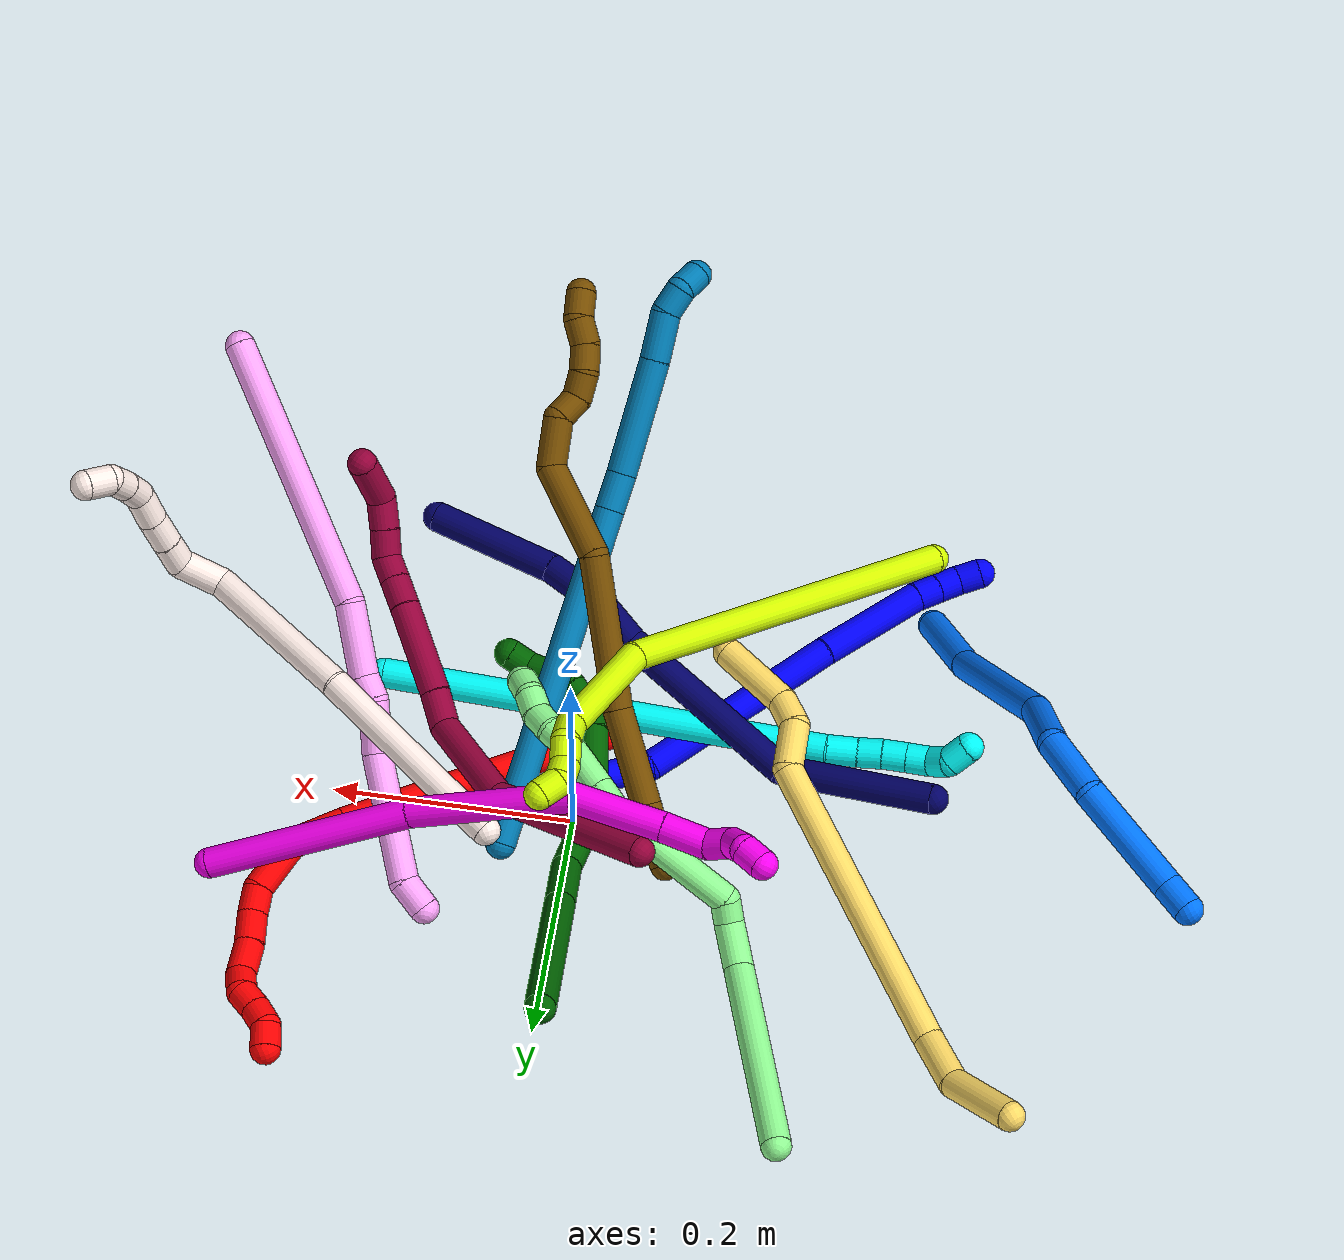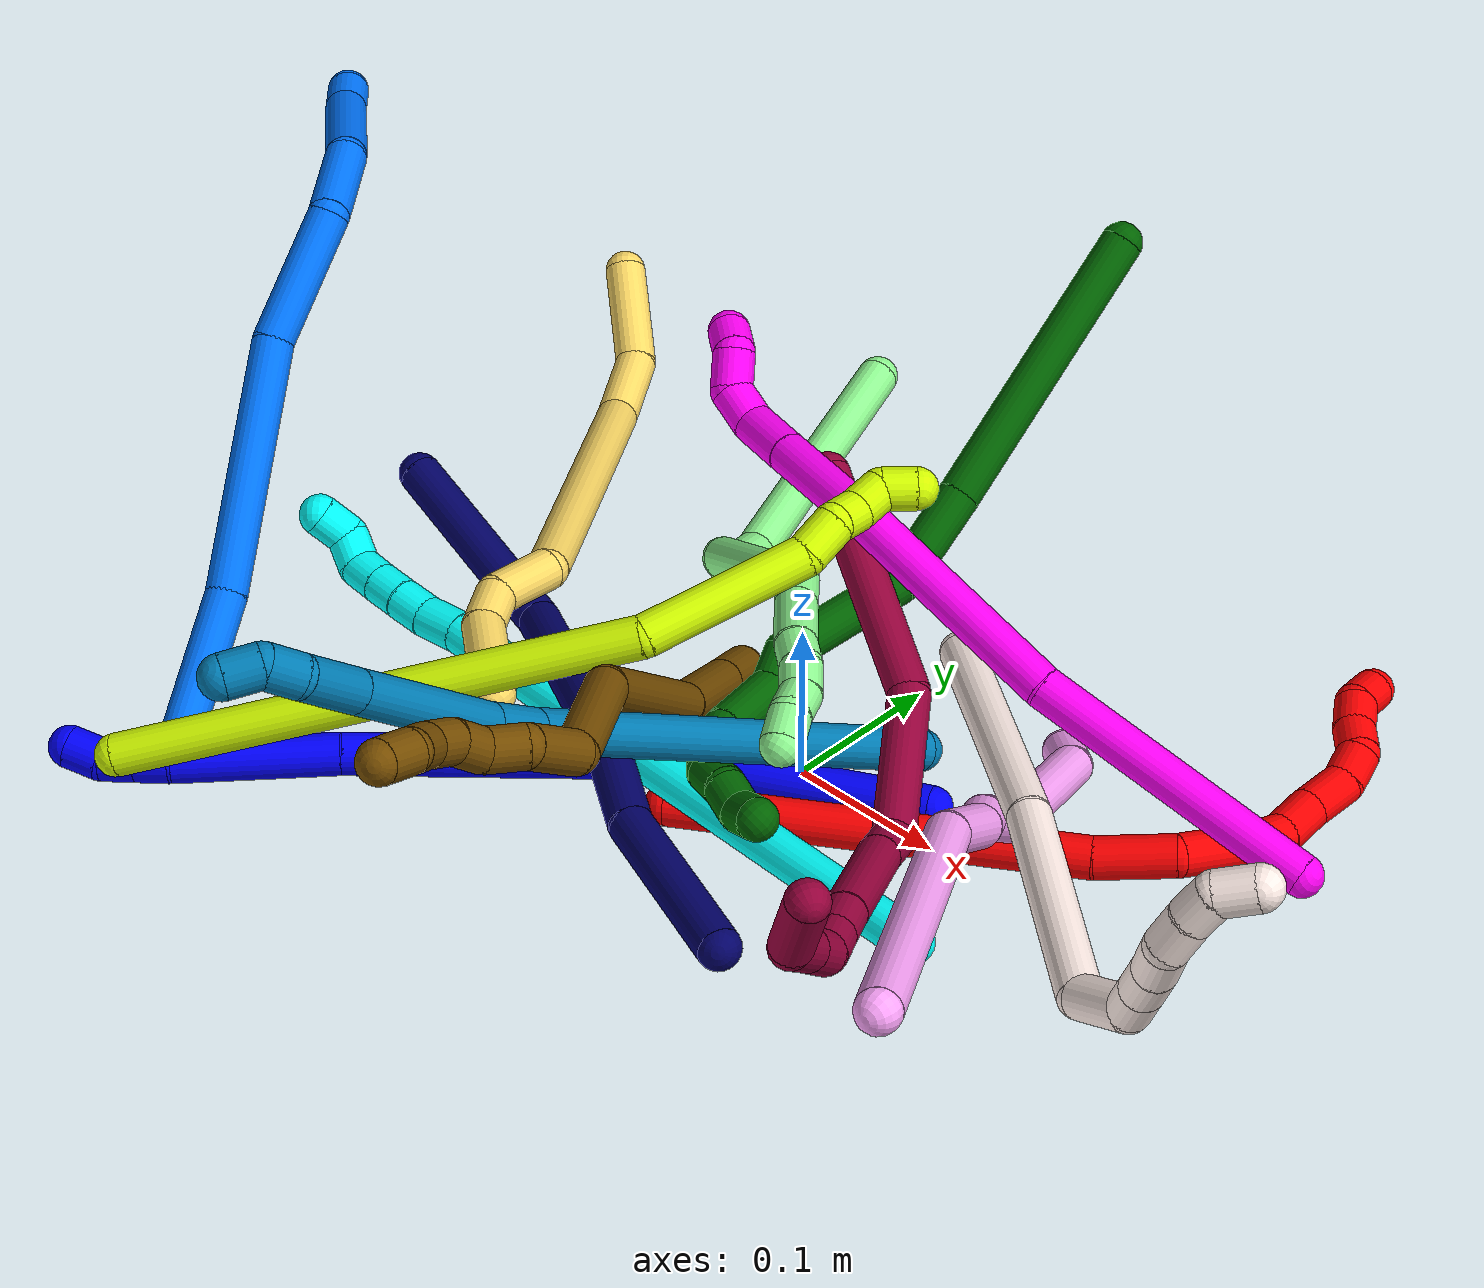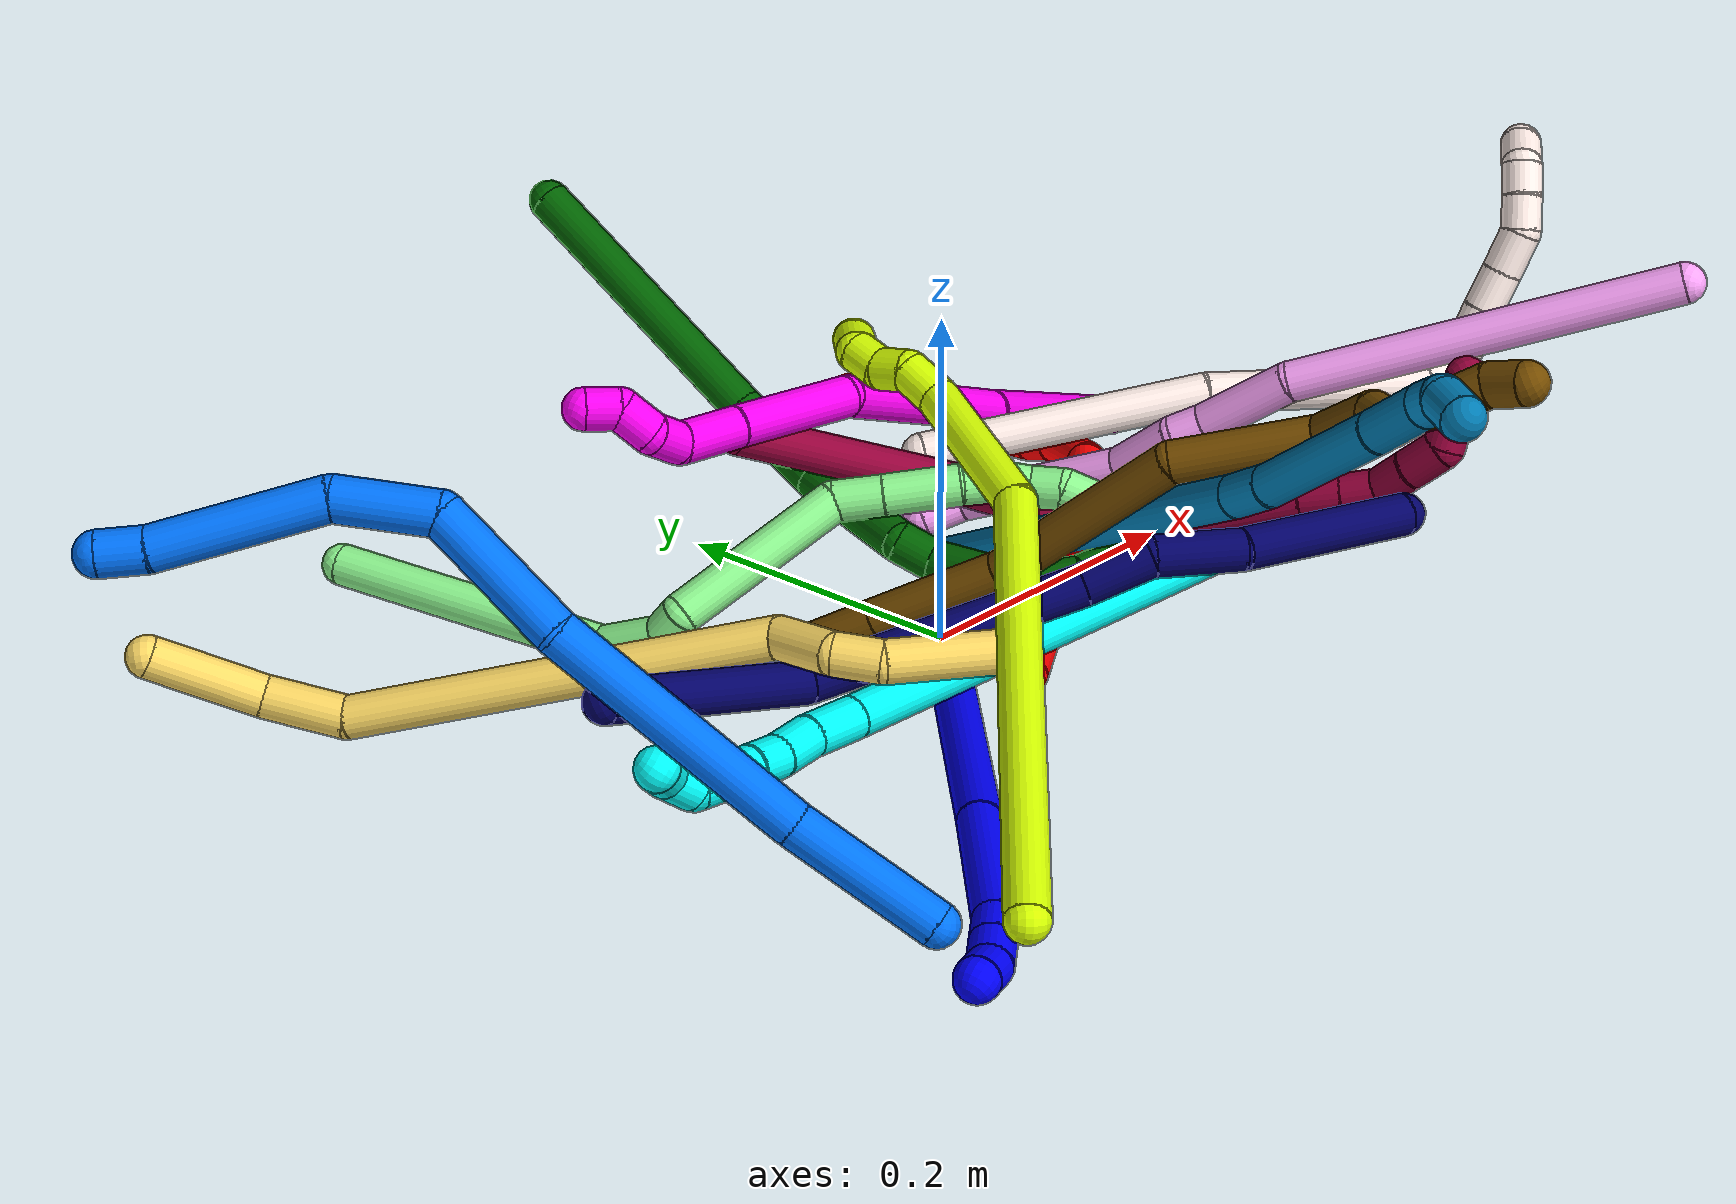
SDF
<sdf version="1.7">
 <world name="default">
  <plugin name="TubeGeneratorPlugin" filename="libtube_generator_plugin.so"/>
  <model name="photoneo_s_sensor">
   <static>1</static>
   <pose>0 0 2 1.57079 1.57079 3.14159</pose>
   <link name="link">
    <inertial><mass>0.1</mass></inertial>
    <sensor name="sensor" type="depth">
     <update_rate>30</update_rate>
     <camera>
      <horizontal_fov>1.22</horizontal_fov>
      <image><width>1920</width><height>1200</height><format>B8G8R8</format></image>
      <clip><near>0.1</near><far>4</far></clip>
      <depth_camera><output>points</output></depth_camera>
     </camera>
     <plugin name="camera_plugin" filename="libgazebo_ros_depth_camera.so">
      <baseline>0.2</baseline>
      <alwaysOn>1</alwaysOn>
      <updateRate>0.0</updateRate>
      <cameraName>camera_ir</cameraName>
      <imageTopicName>/camera/color/image_raw</imageTopicName>
      <cameraInfoTopicName>/camera/color/camera_info</cameraInfoTopicName>
      <depthImageTopicName>/camera/depth/image_raw</depthImageTopicName>
      <depthImageCameraInfoTopicName>/camera/depth/camera_info</depthImageCameraInfoTopicName>
      <pointCloudTopicName>/camera/depth/points</pointCloudTopicName>
      <frameName>fr_optical</frameName>
      <pointCloudCutoff>0.1</pointCloudCutoff>
      <pointCloudCutoffMax>2.0</pointCloudCutoffMax>
      <distortionK1>0</distortionK1>
      <distortionK2>0</distortionK2>
      <distortionK3>0</distortionK3>
      <distortionT1>0</distortionT1>
      <distortionT2>0</distortionT2>
      <CxPrime>0</CxPrime>
      <Cx>0</Cx>
      <Cy>0</Cy>
      <focalLength>0</focalLength>
      <hackBaseline>0</hackBaseline>
     </plugin>
    </sensor>
   </link>
  </model>
  <gravity>0 0 -9.8</gravity>
  <magnetic_field>6e-06 2.3e-05 -4.2e-05</magnetic_field>
  <atmosphere type="adiabatic"/>
  <physics name="default_physics" default="0" type="ode">
   <max_step_size>0.003</max_step_size>
   <real_time_factor>1</real_time_factor>
   <real_time_update_rate>1000</real_time_update_rate>
   <max_contacts>10000</max_contacts>
   <ode>
    <solver>
     <type>quick</type>
     <iters>100</iters>
     <sor>1.3</sor>
     <use_dynamic_moi_rescaling>0</use_dynamic_moi_rescaling>
    </solver>
    <constraints>
     <contact_max_correcting_vel>0</contact_max_correcting_vel>
     <contact_surface_layer>0.001</contact_surface_layer>
     <cfm>0</cfm>
     <erp>0.2</erp>
    </constraints>
   </ode>
  </physics>
  <scene><ambient>0.4 0.4 0.4 1</ambient><background>0.7 0.7 0.7 1</background><shadows>0</shadows></scene>
  <audio><device>default</device></audio>
  <spherical_coordinates>
   <surface_model>EARTH_WGS84</surface_model>
   <latitude_deg>0</latitude_deg>
   <longitude_deg>0</longitude_deg>
   <elevation>0</elevation>
   <heading_deg>0</heading_deg>
  </spherical_coordinates>
  <model name="bin">
   <static>1</static>
   <link name="bottom">
    <collision name="collision-bottom">
     <pose>0 0 -0.01 0 -0 0</pose>
     <geometry><box><size>0.8 0.6 0.02</size></box></geometry>
     <surface>
      <friction><ode><mu>100</mu><mu2>100</mu2></ode></friction>
      <contact><collide_bitmask>65535</collide_bitmask></contact>
     </surface>
    </collision>
   </link>
   <link name="west_wall">
    <collision name="collision-west_wall">
     <pose>-0.41 0 0.1 0 -0 0</pose>
     <geometry><box><size>0.02 0.6 0.2</size></box></geometry>
     <surface>
      <friction><ode><mu>100</mu><mu2>100</mu2></ode></friction>
      <contact><collide_bitmask>65535</collide_bitmask></contact>
     </surface>
    </collision>
   </link>
   <link name="east_wall">
    <collision name="collision-east_wall">
     <pose>0.41 0 0.1 0 -0 0</pose>
     <geometry><box><size>0.02 0.6 0.2</size></box></geometry>
     <surface>
      <friction><ode><mu>100</mu><mu2>100</mu2></ode></friction>
      <contact><collide_bitmask>65535</collide_bitmask></contact>
     </surface>
    </collision>
   </link>
   <link name="south_wall">
    <collision name="collision-south_wall">
     <pose>0 -0.31 0.1 0 -0 0</pose>
     <geometry><box><size>0.8 0.02 0.2</size></box></geometry>
     <surface>
      <friction><ode><mu>100</mu><mu2>100</mu2></ode></friction>
      <contact><collide_bitmask>65535</collide_bitmask></contact>
     </surface>
    </collision>
   </link>
   <link name="north_wall">
    <collision name="collision-north_wall">
     <pose>0 0.31 0.1 0 -0 0</pose>
     <geometry><box><size>0.8 0.02 0.2</size></box></geometry>
     <surface>
      <friction><ode><mu>100</mu><mu2>100</mu2></ode></friction>
      <contact><collide_bitmask>65535</collide_bitmask></contact>
     </surface>
    </collision>
   </link>
  </model>
  <model name="1">
   <static>0</static>
   <link name="1">
    <collision name="collision-cylinder-e_1_1_4">
     <pose>-0.028417 -0.034757 0.066493 0.481658 -0.362048 -0.089841</pose>
     <geometry><cylinder><radius>0.0125</radius><length>0.160461</length></cylinder></geometry>
     <surface>
      <friction><ode><mu>1.16</mu><mu2>1.16</mu2><slip1>0</slip1><slip2>0</slip2></ode></friction>
      <contact><ode><kp>1e+06</kp><kd>1</kd><max_vel>0</max_vel><min_depth>0.001</min_depth></ode></contact>
     </surface>
    </collision>
    <visual name="visual-cylinder-e_1_1_4">
     <pose>-0.028417 -0.034757 0.066493 0.481658 -0.362048 -0.089841</pose>
     <geometry><cylinder><radius>0.0125</radius><length>0.160461</length></cylinder></geometry>
     <material><ambient>0 0 1 1</ambient></material>
    </visual>
    <collision name="collision-cylinder-e_2_4_5">
     <pose>-0.116797 -0.104394 0.191779 0.535452 -0.720053 -0.205791</pose>
     <geometry><cylinder><radius>0.0125</radius><length>0.181865</length></cylinder></geometry>
     <surface>
      <friction><ode><mu>1.16</mu><mu2>1.16</mu2><slip1>0</slip1><slip2>0</slip2></ode></friction>
      <contact><ode><kp>1e+06</kp><kd>1</kd><max_vel>0</max_vel><min_depth>0.001</min_depth></ode></contact>
     </surface>
    </collision>
    <visual name="visual-cylinder-e_2_4_5">
     <pose>-0.116797 -0.104394 0.191779 0.535452 -0.720053 -0.205791</pose>
     <geometry><cylinder><radius>0.0125</radius><length>0.181865</length></cylinder></geometry>
     <material><ambient>0 0 1 1</ambient></material>
    </visual>
    <collision name="collision-cylinder-e_3_5_6">
     <pose>-0.208245 -0.154489 0.283988 0.427269 -0.708819 -0.16021</pose>
     <geometry><cylinder><radius>0.0125</radius><length>0.096736</length></cylinder></geometry>
     <surface>
      <friction><ode><mu>1.16</mu><mu2>1.16</mu2><slip1>0</slip1><slip2>0</slip2></ode></friction>
      <contact><ode><kp>1e+06</kp><kd>1</kd><max_vel>0</max_vel><min_depth>0.001</min_depth></ode></contact>
     </surface>
    </collision>
    <visual name="visual-cylinder-e_3_5_6">
     <pose>-0.208245 -0.154489 0.283988 0.427269 -0.708819 -0.16021</pose>
     <geometry><cylinder><radius>0.0125</radius><length>0.096736</length></cylinder></geometry>
     <material><ambient>0 0 1 1</ambient></material>
    </visual>
    <collision name="collision-cylinder-e_4_6_7">
     <pose>-0.245079 -0.173322 0.325352 0.427246 -0.54974 -0.122201</pose>
     <geometry><cylinder><radius>0.0125</radius><length>0.02048</length></cylinder></geometry>
     <surface>
      <friction><ode><mu>1.16</mu><mu2>1.16</mu2><slip1>0</slip1><slip2>0</slip2></ode></friction>
      <contact><ode><kp>1e+06</kp><kd>1</kd><max_vel>0</max_vel><min_depth>0.001</min_depth></ode></contact>
     </surface>
    </collision>
    <visual name="visual-cylinder-e_4_6_7">
     <pose>-0.245079 -0.173322 0.325352 0.427246 -0.54974 -0.122201</pose>
     <geometry><cylinder><radius>0.0125</radius><length>0.02048</length></cylinder></geometry>
     <material><ambient>0 0 1 1</ambient></material>
    </visual>
    <collision name="collision-cylinder-e_5_7_8">
     <pose>-0.255747 -0.180563 0.341204 0.429652 -0.548769 -0.122682</pose>
     <geometry><cylinder><radius>0.0125</radius><length>0.020387</length></cylinder></geometry>
     <surface>
      <friction><ode><mu>1.16</mu><mu2>1.16</mu2><slip1>0</slip1><slip2>0</slip2></ode></friction>
      <contact><ode><kp>1e+06</kp><kd>1</kd><max_vel>0</max_vel><min_depth>0.001</min_depth></ode></contact>
     </surface>
    </collision>
    <visual name="visual-cylinder-e_5_7_8">
     <pose>-0.255747 -0.180563 0.341204 0.429652 -0.548769 -0.122682</pose>
     <geometry><cylinder><radius>0.0125</radius><length>0.020387</length></cylinder></geometry>
     <material><ambient>0 0 1 1</ambient></material>
    </visual>
    <collision name="collision-cylinder-e_6_8_2">
     <pose>-0.264323 -0.190416 0.356271 0.716025 -0.330793 -0.12474</pose>
     <geometry><cylinder><radius>0.0125</radius><length>0.020071</length></cylinder></geometry>
     <surface>
      <friction><ode><mu>1.16</mu><mu2>1.16</mu2><slip1>0</slip1><slip2>0</slip2></ode></friction>
      <contact><ode><kp>1e+06</kp><kd>1</kd><max_vel>0</max_vel><min_depth>0.001</min_depth></ode></contact>
     </surface>
    </collision>
    <visual name="visual-cylinder-e_6_8_2">
     <pose>-0.264323 -0.190416 0.356271 0.716025 -0.330793 -0.12474</pose>
     <geometry><cylinder><radius>0.0125</radius><length>0.020071</length></cylinder></geometry>
     <material><ambient>0 0 1 1</ambient></material>
    </visual>
    <collision name="collision-sphere-2">
     <pose>-0.267583 -0.196646 0.363432 0 -0 0</pose>
     <geometry><sphere><radius>0.0125</radius></sphere></geometry>
     <surface>
      <friction><ode><mu>1.16</mu><mu2>1.16</mu2><slip1>0</slip1><slip2>0</slip2></ode></friction>
      <contact><ode><kp>1e+06</kp><kd>1</kd><max_vel>0</max_vel><min_depth>0.001</min_depth></ode></contact>
     </surface>
    </collision>
    <visual name="visual-sphere-2">
     <pose>-0.267583 -0.196646 0.363432 0 -0 0</pose>
     <geometry><sphere><radius>0.0125</radius></sphere></geometry>
     <material><ambient>0 0 1 1</ambient></material>
    </visual>
    <collision name="collision-sphere-4">
     <pose>-0.056834 -0.069515 0.132986 0 -0 0</pose>
     <geometry><sphere><radius>0.0125</radius></sphere></geometry>
     <surface>
      <friction><ode><mu>1.16</mu><mu2>1.16</mu2><slip1>0</slip1><slip2>0</slip2></ode></friction>
      <contact><ode><kp>1e+06</kp><kd>1</kd><max_vel>0</max_vel><min_depth>0.001</min_depth></ode></contact>
     </surface>
    </collision>
    <visual name="visual-sphere-4">
     <pose>-0.056834 -0.069515 0.132986 0 -0 0</pose>
     <geometry><sphere><radius>0.0125</radius></sphere></geometry>
     <material><ambient>0 0 1 1</ambient></material>
    </visual>
    <collision name="collision-sphere-1">
     <geometry><sphere><radius>0.0125</radius></sphere></geometry>
     <surface>
      <friction><ode><mu>1.16</mu><mu2>1.16</mu2><slip1>0</slip1><slip2>0</slip2></ode></friction>
      <contact><ode><kp>1e+06</kp><kd>1</kd><max_vel>0</max_vel><min_depth>0.001</min_depth></ode></contact>
     </surface>
    </collision>
    <visual name="visual-sphere-1">
     <geometry><sphere><radius>0.0125</radius></sphere></geometry>
     <material><ambient>0 0 1 1</ambient></material>
    </visual>
    <collision name="collision-sphere-8">
     <pose>-0.261064 -0.184186 0.349111 0 -0 0</pose>
     <geometry><sphere><radius>0.0125</radius></sphere></geometry>
     <surface>
      <friction><ode><mu>1.16</mu><mu2>1.16</mu2><slip1>0</slip1><slip2>0</slip2></ode></friction>
      <contact><ode><kp>1e+06</kp><kd>1</kd><max_vel>0</max_vel><min_depth>0.001</min_depth></ode></contact>
     </surface>
    </collision>
    <visual name="visual-sphere-8">
     <pose>-0.261064 -0.184186 0.349111 0 -0 0</pose>
     <geometry><sphere><radius>0.0125</radius></sphere></geometry>
     <material><ambient>0 0 1 1</ambient></material>
    </visual>
    <collision name="collision-sphere-5">
     <pose>-0.17676 -0.139274 0.250572 0 -0 0</pose>
     <geometry><sphere><radius>0.0125</radius></sphere></geometry>
     <surface>
      <friction><ode><mu>1.16</mu><mu2>1.16</mu2><slip1>0</slip1><slip2>0</slip2></ode></friction>
      <contact><ode><kp>1e+06</kp><kd>1</kd><max_vel>0</max_vel><min_depth>0.001</min_depth></ode></contact>
     </surface>
    </collision>
    <visual name="visual-sphere-5">
     <pose>-0.17676 -0.139274 0.250572 0 -0 0</pose>
     <geometry><sphere><radius>0.0125</radius></sphere></geometry>
     <material><ambient>0 0 1 1</ambient></material>
    </visual>
    <collision name="collision-sphere-6">
     <pose>-0.239729 -0.169704 0.317405 0 -0 0</pose>
     <geometry><sphere><radius>0.0125</radius></sphere></geometry>
     <surface>
      <friction><ode><mu>1.16</mu><mu2>1.16</mu2><slip1>0</slip1><slip2>0</slip2></ode></friction>
      <contact><ode><kp>1e+06</kp><kd>1</kd><max_vel>0</max_vel><min_depth>0.001</min_depth></ode></contact>
     </surface>
    </collision>
    <visual name="visual-sphere-6">
     <pose>-0.239729 -0.169704 0.317405 0 -0 0</pose>
     <geometry><sphere><radius>0.0125</radius></sphere></geometry>
     <material><ambient>0 0 1 1</ambient></material>
    </visual>
    <collision name="collision-sphere-7">
     <pose>-0.250429 -0.17694 0.333298 0 -0 0</pose>
     <geometry><sphere><radius>0.0125</radius></sphere></geometry>
     <surface>
      <friction><ode><mu>1.16</mu><mu2>1.16</mu2><slip1>0</slip1><slip2>0</slip2></ode></friction>
      <contact><ode><kp>1e+06</kp><kd>1</kd><max_vel>0</max_vel><min_depth>0.001</min_depth></ode></contact>
     </surface>
    </collision>
    <visual name="visual-sphere-7">
     <pose>-0.250429 -0.17694 0.333298 0 -0 0</pose>
     <geometry><sphere><radius>0.0125</radius></sphere></geometry>
     <material><ambient>0 0 1 1</ambient></material>
    </visual>
    <inertial>
     <pose>-0.122968 -0.10112 0.187579 0 -0 0</pose>
     <mass>0.5</mass>
     <inertia>
      <ixx>0.000625</ixx>
      <ixy>0</ixy>
      <ixz>0</ixz>
      <iyy>0.000723</iyy>
      <iyz>0</iyz>
      <izz>0.000915</izz>
     </inertia>
    </inertial>
   </link>
   <pose>0.088883 0.012163 0.017165 -2.11985 0.077501 1.6497</pose>
  </model>
  <model name="2">
   <static>0</static>
   <link name="2">
    <collision name="collision-cylinder-e_1_1_4">
     <pose>-0.010966 0.00109 0.121062 -0.009003 -0.090335 0.000407</pose>
     <geometry><cylinder><radius>0.0125</radius><length>0.243126</length></cylinder></geometry>
     <surface>
      <friction><ode><mu>1.16</mu><mu2>1.16</mu2><slip1>0</slip1><slip2>0</slip2></ode></friction>
      <contact><ode><kp>1e+06</kp><kd>1</kd><max_vel>0</max_vel><min_depth>0.001</min_depth></ode></contact>
     </surface>
    </collision>
    <visual name="visual-cylinder-e_1_1_4">
     <pose>-0.010966 0.00109 0.121062 -0.009003 -0.090335 0.000407</pose>
     <geometry><cylinder><radius>0.0125</radius><length>0.243126</length></cylinder></geometry>
     <material><ambient>1 0 0 1</ambient></material>
    </visual>
    <collision name="collision-cylinder-e_2_4_5">
     <pose>-0.021696 0.005183 0.265403 -0.128313 0.010084 -0.000648</pose>
     <geometry><cylinder><radius>0.0125</radius><length>0.046946</length></cylinder></geometry>
     <surface>
      <friction><ode><mu>1.16</mu><mu2>1.16</mu2><slip1>0</slip1><slip2>0</slip2></ode></friction>
      <contact><ode><kp>1e+06</kp><kd>1</kd><max_vel>0</max_vel><min_depth>0.001</min_depth></ode></contact>
     </surface>
    </collision>
    <visual name="visual-cylinder-e_2_4_5">
     <pose>-0.021696 0.005183 0.265403 -0.128313 0.010084 -0.000648</pose>
     <geometry><cylinder><radius>0.0125</radius><length>0.046946</length></cylinder></geometry>
     <material><ambient>1 0 0 1</ambient></material>
    </visual>
    <collision name="collision-cylinder-e_3_5_6">
     <pose>-0.009769 0.008834 0.309447 -0.031159 0.512564 -0.008166</pose>
     <geometry><cylinder><radius>0.0125</radius><length>0.047676</length></cylinder></geometry>
     <surface>
      <friction><ode><mu>1.16</mu><mu2>1.16</mu2><slip1>0</slip1><slip2>0</slip2></ode></friction>
      <contact><ode><kp>1e+06</kp><kd>1</kd><max_vel>0</max_vel><min_depth>0.001</min_depth></ode></contact>
     </surface>
    </collision>
    <visual name="visual-cylinder-e_3_5_6">
     <pose>-0.009769 0.008834 0.309447 -0.031159 0.512564 -0.008166</pose>
     <geometry><cylinder><radius>0.0125</radius><length>0.047676</length></cylinder></geometry>
     <material><ambient>1 0 0 1</ambient></material>
    </visual>
    <collision name="collision-cylinder-e_4_6_7">
     <pose>0.011055 0.009045 0.33703 0.06385 0.92856 0.031983</pose>
     <geometry><cylinder><radius>0.0125</radius><length>0.022813</length></cylinder></geometry>
     <surface>
      <friction><ode><mu>1.16</mu><mu2>1.16</mu2><slip1>0</slip1><slip2>0</slip2></ode></friction>
      <contact><ode><kp>1e+06</kp><kd>1</kd><max_vel>0</max_vel><min_depth>0.001</min_depth></ode></contact>
     </surface>
    </collision>
    <visual name="visual-cylinder-e_4_6_7">
     <pose>0.011055 0.009045 0.33703 0.06385 0.92856 0.031983</pose>
     <geometry><cylinder><radius>0.0125</radius><length>0.022813</length></cylinder></geometry>
     <material><ambient>1 0 0 1</ambient></material>
    </visual>
    <collision name="collision-cylinder-e_5_7_8">
     <pose>0.032003 0.012226 0.350994 -0.468572 0.975057 -0.251755</pose>
     <geometry><cylinder><radius>0.0125</radius><length>0.028546</length></cylinder></geometry>
     <surface>
      <friction><ode><mu>1.16</mu><mu2>1.16</mu2><slip1>0</slip1><slip2>0</slip2></ode></friction>
      <contact><ode><kp>1e+06</kp><kd>1</kd><max_vel>0</max_vel><min_depth>0.001</min_depth></ode></contact>
     </surface>
    </collision>
    <visual name="visual-cylinder-e_5_7_8">
     <pose>0.032003 0.012226 0.350994 -0.468572 0.975057 -0.251755</pose>
     <geometry><cylinder><radius>0.0125</radius><length>0.028546</length></cylinder></geometry>
     <material><ambient>1 0 0 1</ambient></material>
    </visual>
    <collision name="collision-cylinder-e_6_8_9">
     <pose>0.054793 0.020033 0.367251 -0.431036 0.83039 -0.192412</pose>
     <geometry><cylinder><radius>0.0125</radius><length>0.029735</length></cylinder></geometry>
     <surface>
      <friction><ode><mu>1.16</mu><mu2>1.16</mu2><slip1>0</slip1><slip2>0</slip2></ode></friction>
      <contact><ode><kp>1e+06</kp><kd>1</kd><max_vel>0</max_vel><min_depth>0.001</min_depth></ode></contact>
     </surface>
    </collision>
    <visual name="visual-cylinder-e_6_8_9">
     <pose>0.054793 0.020033 0.367251 -0.431036 0.83039 -0.192412</pose>
     <geometry><cylinder><radius>0.0125</radius><length>0.029735</length></cylinder></geometry>
     <material><ambient>1 0 0 1</ambient></material>
    </visual>
    <collision name="collision-cylinder-e_7_9_10">
     <pose>0.073628 0.030298 0.379943 -1.03818 0.839703 -0.49945</pose>
     <geometry><cylinder><radius>0.0125</radius><length>0.021119</length></cylinder></geometry>
     <surface>
      <friction><ode><mu>1.16</mu><mu2>1.16</mu2><slip1>0</slip1><slip2>0</slip2></ode></friction>
      <contact><ode><kp>1e+06</kp><kd>1</kd><max_vel>0</max_vel><min_depth>0.001</min_depth></ode></contact>
     </surface>
    </collision>
    <visual name="visual-cylinder-e_7_9_10">
     <pose>0.073628 0.030298 0.379943 -1.03818 0.839703 -0.49945</pose>
     <geometry><cylinder><radius>0.0125</radius><length>0.021119</length></cylinder></geometry>
     <material><ambient>1 0 0 1</ambient></material>
    </visual>
    <collision name="collision-cylinder-e_8_10_11">
     <pose>0.090783 0.039705 0.381913 -2.02088 1.19169 -1.64829</pose>
     <geometry><cylinder><radius>0.0125</radius><length>0.020008</length></cylinder></geometry>
     <surface>
      <friction><ode><mu>1.16</mu><mu2>1.16</mu2><slip1>0</slip1><slip2>0</slip2></ode></friction>
      <contact><ode><kp>1e+06</kp><kd>1</kd><max_vel>0</max_vel><min_depth>0.001</min_depth></ode></contact>
     </surface>
    </collision>
    <visual name="visual-cylinder-e_8_10_11">
     <pose>0.090783 0.039705 0.381913 -2.02088 1.19169 -1.64829</pose>
     <geometry><cylinder><radius>0.0125</radius><length>0.020008</length></cylinder></geometry>
     <material><ambient>1 0 0 1</ambient></material>
    </visual>
    <collision name="collision-cylinder-e_9_11_12">
     <pose>0.109041 0.047479 0.380257 -1.58095 1.11087 -1.11999</pose>
     <geometry><cylinder><radius>0.0125</radius><length>0.020008</length></cylinder></geometry>
     <surface>
      <friction><ode><mu>1.16</mu><mu2>1.16</mu2><slip1>0</slip1><slip2>0</slip2></ode></friction>
      <contact><ode><kp>1e+06</kp><kd>1</kd><max_vel>0</max_vel><min_depth>0.001</min_depth></ode></contact>
     </surface>
    </collision>
    <visual name="visual-cylinder-e_9_11_12">
     <pose>0.109041 0.047479 0.380257 -1.58095 1.11087 -1.11999</pose>
     <geometry><cylinder><radius>0.0125</radius><length>0.020008</length></cylinder></geometry>
     <material><ambient>1 0 0 1</ambient></material>
    </visual>
    <collision name="collision-cylinder-e_10_12_2">
     <pose>0.126918 0.052989 0.384646 -0.236727 1.09776 -0.145199</pose>
     <geometry><cylinder><radius>0.0125</radius><length>0.020024</length></cylinder></geometry>
     <surface>
      <friction><ode><mu>1.16</mu><mu2>1.16</mu2><slip1>0</slip1><slip2>0</slip2></ode></friction>
      <contact><ode><kp>1e+06</kp><kd>1</kd><max_vel>0</max_vel><min_depth>0.001</min_depth></ode></contact>
     </surface>
    </collision>
    <visual name="visual-cylinder-e_10_12_2">
     <pose>0.126918 0.052989 0.384646 -0.236727 1.09776 -0.145199</pose>
     <geometry><cylinder><radius>0.0125</radius><length>0.020024</length></cylinder></geometry>
     <material><ambient>1 0 0 1</ambient></material>
    </visual>
    <collision name="collision-sphere-2">
     <pose>0.135831 0.054059 0.38908 0 -0 0</pose>
     <geometry><sphere><radius>0.0125</radius></sphere></geometry>
     <surface>
      <friction><ode><mu>1.16</mu><mu2>1.16</mu2><slip1>0</slip1><slip2>0</slip2></ode></friction>
      <contact><ode><kp>1e+06</kp><kd>1</kd><max_vel>0</max_vel><min_depth>0.001</min_depth></ode></contact>
     </surface>
    </collision>
    <visual name="visual-sphere-2">
     <pose>0.135831 0.054059 0.38908 0 -0 0</pose>
     <geometry><sphere><radius>0.0125</radius></sphere></geometry>
     <material><ambient>1 0 0 1</ambient></material>
    </visual>
    <collision name="collision-sphere-12">
     <pose>0.118006 0.05192 0.380212 0 -0 0</pose>
     <geometry><sphere><radius>0.0125</radius></sphere></geometry>
     <surface>
      <friction><ode><mu>1.16</mu><mu2>1.16</mu2><slip1>0</slip1><slip2>0</slip2></ode></friction>
      <contact><ode><kp>1e+06</kp><kd>1</kd><max_vel>0</max_vel><min_depth>0.001</min_depth></ode></contact>
     </surface>
    </collision>
    <visual name="visual-sphere-12">
     <pose>0.118006 0.05192 0.380212 0 -0 0</pose>
     <geometry><sphere><radius>0.0125</radius></sphere></geometry>
     <material><ambient>1 0 0 1</ambient></material>
    </visual>
    <collision name="collision-sphere-11">
     <pose>0.100077 0.043039 0.380302 0 -0 0</pose>
     <geometry><sphere><radius>0.0125</radius></sphere></geometry>
     <surface>
      <friction><ode><mu>1.16</mu><mu2>1.16</mu2><slip1>0</slip1><slip2>0</slip2></ode></friction>
      <contact><ode><kp>1e+06</kp><kd>1</kd><max_vel>0</max_vel><min_depth>0.001</min_depth></ode></contact>
     </surface>
    </collision>
    <visual name="visual-sphere-11">
     <pose>0.100077 0.043039 0.380302 0 -0 0</pose>
     <geometry><sphere><radius>0.0125</radius></sphere></geometry>
     <material><ambient>1 0 0 1</ambient></material>
    </visual>
    <collision name="collision-sphere-10">
     <pose>0.081489 0.036371 0.383524 0 -0 0</pose>
     <geometry><sphere><radius>0.0125</radius></sphere></geometry>
     <surface>
      <friction><ode><mu>1.16</mu><mu2>1.16</mu2><slip1>0</slip1><slip2>0</slip2></ode></friction>
      <contact><ode><kp>1e+06</kp><kd>1</kd><max_vel>0</max_vel><min_depth>0.001</min_depth></ode></contact>
     </surface>
    </collision>
    <visual name="visual-sphere-10">
     <pose>0.081489 0.036371 0.383524 0 -0 0</pose>
     <geometry><sphere><radius>0.0125</radius></sphere></geometry>
     <material><ambient>1 0 0 1</ambient></material>
    </visual>
    <collision name="collision-sphere-9">
     <pose>0.065768 0.024224 0.376363 0 -0 0</pose>
     <geometry><sphere><radius>0.0125</radius></sphere></geometry>
     <surface>
      <friction><ode><mu>1.16</mu><mu2>1.16</mu2><slip1>0</slip1><slip2>0</slip2></ode></friction>
      <contact><ode><kp>1e+06</kp><kd>1</kd><max_vel>0</max_vel><min_depth>0.001</min_depth></ode></contact>
     </surface>
    </collision>
    <visual name="visual-sphere-9">
     <pose>0.065768 0.024224 0.376363 0 -0 0</pose>
     <geometry><sphere><radius>0.0125</radius></sphere></geometry>
     <material><ambient>1 0 0 1</ambient></material>
    </visual>
    <collision name="collision-sphere-4">
     <pose>-0.021933 0.00218 0.242125 0 -0 0</pose>
     <geometry><sphere><radius>0.0125</radius></sphere></geometry>
     <surface>
      <friction><ode><mu>1.16</mu><mu2>1.16</mu2><slip1>0</slip1><slip2>0</slip2></ode></friction>
      <contact><ode><kp>1e+06</kp><kd>1</kd><max_vel>0</max_vel><min_depth>0.001</min_depth></ode></contact>
     </surface>
    </collision>
    <visual name="visual-sphere-4">
     <pose>-0.021933 0.00218 0.242125 0 -0 0</pose>
     <geometry><sphere><radius>0.0125</radius></sphere></geometry>
     <material><ambient>1 0 0 1</ambient></material>
    </visual>
    <collision name="collision-sphere-1">
     <geometry><sphere><radius>0.0125</radius></sphere></geometry>
     <surface>
      <friction><ode><mu>1.16</mu><mu2>1.16</mu2><slip1>0</slip1><slip2>0</slip2></ode></friction>
      <contact><ode><kp>1e+06</kp><kd>1</kd><max_vel>0</max_vel><min_depth>0.001</min_depth></ode></contact>
     </surface>
    </collision>
    <visual name="visual-sphere-1">
     <geometry><sphere><radius>0.0125</radius></sphere></geometry>
     <material><ambient>1 0 0 1</ambient></material>
    </visual>
    <collision name="collision-sphere-8">
     <pose>0.043818 0.015843 0.358139 0 -0 0</pose>
     <geometry><sphere><radius>0.0125</radius></sphere></geometry>
     <surface>
      <friction><ode><mu>1.16</mu><mu2>1.16</mu2><slip1>0</slip1><slip2>0</slip2></ode></friction>
      <contact><ode><kp>1e+06</kp><kd>1</kd><max_vel>0</max_vel><min_depth>0.001</min_depth></ode></contact>
     </surface>
    </collision>
    <visual name="visual-sphere-8">
     <pose>0.043818 0.015843 0.358139 0 -0 0</pose>
     <geometry><sphere><radius>0.0125</radius></sphere></geometry>
     <material><ambient>1 0 0 1</ambient></material>
    </visual>
    <collision name="collision-sphere-5">
     <pose>-0.021459 0.008187 0.288682 0 -0 0</pose>
     <geometry><sphere><radius>0.0125</radius></sphere></geometry>
     <surface>
      <friction><ode><mu>1.16</mu><mu2>1.16</mu2><slip1>0</slip1><slip2>0</slip2></ode></friction>
      <contact><ode><kp>1e+06</kp><kd>1</kd><max_vel>0</max_vel><min_depth>0.001</min_depth></ode></contact>
     </surface>
    </collision>
    <visual name="visual-sphere-5">
     <pose>-0.021459 0.008187 0.288682 0 -0 0</pose>
     <geometry><sphere><radius>0.0125</radius></sphere></geometry>
     <material><ambient>1 0 0 1</ambient></material>
    </visual>
    <collision name="collision-sphere-6">
     <pose>0.001922 0.009481 0.330211 0 -0 0</pose>
     <geometry><sphere><radius>0.0125</radius></sphere></geometry>
     <surface>
      <friction><ode><mu>1.16</mu><mu2>1.16</mu2><slip1>0</slip1><slip2>0</slip2></ode></friction>
      <contact><ode><kp>1e+06</kp><kd>1</kd><max_vel>0</max_vel><min_depth>0.001</min_depth></ode></contact>
     </surface>
    </collision>
    <visual name="visual-sphere-6">
     <pose>0.001922 0.009481 0.330211 0 -0 0</pose>
     <geometry><sphere><radius>0.0125</radius></sphere></geometry>
     <material><ambient>1 0 0 1</ambient></material>
    </visual>
    <collision name="collision-sphere-7">
     <pose>0.020189 0.008609 0.343848 0 -0 0</pose>
     <geometry><sphere><radius>0.0125</radius></sphere></geometry>
     <surface>
      <friction><ode><mu>1.16</mu><mu2>1.16</mu2><slip1>0</slip1><slip2>0</slip2></ode></friction>
      <contact><ode><kp>1e+06</kp><kd>1</kd><max_vel>0</max_vel><min_depth>0.001</min_depth></ode></contact>
     </surface>
    </collision>
    <visual name="visual-sphere-7">
     <pose>0.020189 0.008609 0.343848 0 -0 0</pose>
     <geometry><sphere><radius>0.0125</radius></sphere></geometry>
     <material><ambient>1 0 0 1</ambient></material>
    </visual>
    <inertial>
     <pose>0.013478 0.011052 0.2325 0 -0 0</pose>
     <mass>0.5</mass>
     <inertia>
      <ixx>0.001237</ixx>
      <ixy>0</ixy>
      <ixz>0</ixz>
      <iyy>0.001243</iyy>
      <iyz>0</iyz>
      <izz>0.000106</izz>
     </inertia>
    </inertial>
   </link>
   <pose>-0.023972 -0.085342 0.012408 1.58174 0.277006 2.20572</pose>
  </model>
  <model name="3">
   <static>0</static>
   <link name="3">
    <collision name="collision-cylinder-e_1_1_4">
     <pose>-0.14159 0.011045 -0.092506 -3.02276 -0.988834 2.92179</pose>
     <geometry><cylinder><radius>0.0125</radius><length>0.338982</length></cylinder></geometry>
     <surface>
      <friction><ode><mu>1.16</mu><mu2>1.16</mu2><slip1>0</slip1><slip2>0</slip2></ode></friction>
      <contact><ode><kp>1e+06</kp><kd>1</kd><max_vel>0</max_vel><min_depth>0.001</min_depth></ode></contact>
     </surface>
    </collision>
    <visual name="visual-cylinder-e_1_1_4">
     <pose>-0.14159 0.011045 -0.092506 -3.02276 -0.988834 2.92179</pose>
     <geometry><cylinder><radius>0.0125</radius><length>0.338982</length></cylinder></geometry>
     <material><ambient>0.003922 1 0.996078 1</ambient></material>
    </visual>
    <collision name="collision-cylinder-e_2_4_5">
     <pose>-0.296875 0.023399 -0.194341 -3.00205 -0.968269 2.87736</pose>
     <geometry><cylinder><radius>0.0125</radius><length>0.033243</length></cylinder></geometry>
     <surface>
      <friction><ode><mu>1.16</mu><mu2>1.16</mu2><slip1>0</slip1><slip2>0</slip2></ode></friction>
      <contact><ode><kp>1e+06</kp><kd>1</kd><max_vel>0</max_vel><min_depth>0.001</min_depth></ode></contact>
     </surface>
    </collision>
    <visual name="visual-cylinder-e_2_4_5">
     <pose>-0.296875 0.023399 -0.194341 -3.00205 -0.968269 2.87736</pose>
     <geometry><cylinder><radius>0.0125</radius><length>0.033243</length></cylinder></geometry>
     <material><ambient>0.003922 1 0.996078 1</ambient></material>
    </visual>
    <collision name="collision-cylinder-e_3_5_6">
     <pose>-0.32225 0.026174 -0.209461 -2.89397 -1.09803 2.74021</pose>
     <geometry><cylinder><radius>0.0125</radius><length>0.026239</length></cylinder></geometry>
     <surface>
      <friction><ode><mu>1.16</mu><mu2>1.16</mu2><slip1>0</slip1><slip2>0</slip2></ode></friction>
      <contact><ode><kp>1e+06</kp><kd>1</kd><max_vel>0</max_vel><min_depth>0.001</min_depth></ode></contact>
     </surface>
    </collision>
    <visual name="visual-cylinder-e_3_5_6">
     <pose>-0.32225 0.026174 -0.209461 -2.89397 -1.09803 2.74021</pose>
     <geometry><cylinder><radius>0.0125</radius><length>0.026239</length></cylinder></geometry>
     <material><ambient>0.003922 1 0.996078 1</ambient></material>
    </visual>
    <collision name="collision-cylinder-e_4_6_7">
     <pose>-0.342412 0.029528 -0.221072 -2.82751 -0.945819 2.54131</pose>
     <geometry><cylinder><radius>0.0125</radius><length>0.020916</length></cylinder></geometry>
     <surface>
      <friction><ode><mu>1.16</mu><mu2>1.16</mu2><slip1>0</slip1><slip2>0</slip2></ode></friction>
      <contact><ode><kp>1e+06</kp><kd>1</kd><max_vel>0</max_vel><min_depth>0.001</min_depth></ode></contact>
     </surface>
    </collision>
    <visual name="visual-cylinder-e_4_6_7">
     <pose>-0.342412 0.029528 -0.221072 -2.82751 -0.945819 2.54131</pose>
     <geometry><cylinder><radius>0.0125</radius><length>0.020916</length></cylinder></geometry>
     <material><ambient>0.003922 1 0.996078 1</ambient></material>
    </visual>
    <collision name="collision-cylinder-e_5_7_8">
     <pose>-0.359059 0.032416 -0.232596 -2.96857 -0.953961 2.80904</pose>
     <geometry><cylinder><radius>0.0125</radius><length>0.020021</length></cylinder></geometry>
     <surface>
      <friction><ode><mu>1.16</mu><mu2>1.16</mu2><slip1>0</slip1><slip2>0</slip2></ode></friction>
      <contact><ode><kp>1e+06</kp><kd>1</kd><max_vel>0</max_vel><min_depth>0.001</min_depth></ode></contact>
     </surface>
    </collision>
    <visual name="visual-cylinder-e_5_7_8">
     <pose>-0.359059 0.032416 -0.232596 -2.96857 -0.953961 2.80904</pose>
     <geometry><cylinder><radius>0.0125</radius><length>0.020021</length></cylinder></geometry>
     <material><ambient>0.003922 1 0.996078 1</ambient></material>
    </visual>
    <collision name="collision-cylinder-e_6_8_9">
     <pose>-0.375362 0.034303 -0.244308 -2.99443 -0.929653 2.84969</pose>
     <geometry><cylinder><radius>0.0125</radius><length>0.020309</length></cylinder></geometry>
     <surface>
      <friction><ode><mu>1.16</mu><mu2>1.16</mu2><slip1>0</slip1><slip2>0</slip2></ode></friction>
      <contact><ode><kp>1e+06</kp><kd>1</kd><max_vel>0</max_vel><min_depth>0.001</min_depth></ode></contact>
     </surface>
    </collision>
    <visual name="visual-cylinder-e_6_8_9">
     <pose>-0.375362 0.034303 -0.244308 -2.99443 -0.929653 2.84969</pose>
     <geometry><cylinder><radius>0.0125</radius><length>0.020309</length></cylinder></geometry>
     <material><ambient>0.003922 1 0.996078 1</ambient></material>
    </visual>
    <collision name="collision-cylinder-e_7_9_10">
     <pose>-0.386672 0.038365 -0.259279 -2.80159 -0.321974 1.51532</pose>
     <geometry><cylinder><radius>0.0125</radius><length>0.020046</length></cylinder></geometry>
     <surface>
      <friction><ode><mu>1.16</mu><mu2>1.16</mu2><slip1>0</slip1><slip2>0</slip2></ode></friction>
      <contact><ode><kp>1e+06</kp><kd>1</kd><max_vel>0</max_vel><min_depth>0.001</min_depth></ode></contact>
     </surface>
    </collision>
    <visual name="visual-cylinder-e_7_9_10">
     <pose>-0.386672 0.038365 -0.259279 -2.80159 -0.321974 1.51532</pose>
     <geometry><cylinder><radius>0.0125</radius><length>0.020046</length></cylinder></geometry>
     <material><ambient>0.003922 1 0.996078 1</ambient></material>
    </visual>
    <collision name="collision-cylinder-e_8_10_2">
     <pose>-0.394581 0.049377 -0.272545 -2.07256 -0.487094 0.794794</pose>
     <geometry><cylinder><radius>0.0125</radius><length>0.020243</length></cylinder></geometry>
     <surface>
      <friction><ode><mu>1.16</mu><mu2>1.16</mu2><slip1>0</slip1><slip2>0</slip2></ode></friction>
      <contact><ode><kp>1e+06</kp><kd>1</kd><max_vel>0</max_vel><min_depth>0.001</min_depth></ode></contact>
     </surface>
    </collision>
    <visual name="visual-cylinder-e_8_10_2">
     <pose>-0.394581 0.049377 -0.272545 -2.07256 -0.487094 0.794794</pose>
     <geometry><cylinder><radius>0.0125</radius><length>0.020243</length></cylinder></geometry>
     <material><ambient>0.003922 1 0.996078 1</ambient></material>
    </visual>
    <collision name="collision-sphere-2">
     <pose>-0.399319 0.057219 -0.276847 0 -0 0</pose>
     <geometry><sphere><radius>0.0125</radius></sphere></geometry>
     <surface>
      <friction><ode><mu>1.16</mu><mu2>1.16</mu2><slip1>0</slip1><slip2>0</slip2></ode></friction>
      <contact><ode><kp>1e+06</kp><kd>1</kd><max_vel>0</max_vel><min_depth>0.001</min_depth></ode></contact>
     </surface>
    </collision>
    <visual name="visual-sphere-2">
     <pose>-0.399319 0.057219 -0.276847 0 -0 0</pose>
     <geometry><sphere><radius>0.0125</radius></sphere></geometry>
     <material><ambient>0.003922 1 0.996078 1</ambient></material>
    </visual>
    <collision name="collision-sphere-10">
     <pose>-0.389844 0.041535 -0.268243 0 -0 0</pose>
     <geometry><sphere><radius>0.0125</radius></sphere></geometry>
     <surface>
      <friction><ode><mu>1.16</mu><mu2>1.16</mu2><slip1>0</slip1><slip2>0</slip2></ode></friction>
      <contact><ode><kp>1e+06</kp><kd>1</kd><max_vel>0</max_vel><min_depth>0.001</min_depth></ode></contact>
     </surface>
    </collision>
    <visual name="visual-sphere-10">
     <pose>-0.389844 0.041535 -0.268243 0 -0 0</pose>
     <geometry><sphere><radius>0.0125</radius></sphere></geometry>
     <material><ambient>0.003922 1 0.996078 1</ambient></material>
    </visual>
    <collision name="collision-sphere-9">
     <pose>-0.3835 0.035194 -0.250316 0 -0 0</pose>
     <geometry><sphere><radius>0.0125</radius></sphere></geometry>
     <surface>
      <friction><ode><mu>1.16</mu><mu2>1.16</mu2><slip1>0</slip1><slip2>0</slip2></ode></friction>
      <contact><ode><kp>1e+06</kp><kd>1</kd><max_vel>0</max_vel><min_depth>0.001</min_depth></ode></contact>
     </surface>
    </collision>
    <visual name="visual-sphere-9">
     <pose>-0.3835 0.035194 -0.250316 0 -0 0</pose>
     <geometry><sphere><radius>0.0125</radius></sphere></geometry>
     <material><ambient>0.003922 1 0.996078 1</ambient></material>
    </visual>
    <collision name="collision-sphere-4">
     <pose>-0.28318 0.022089 -0.185012 0 -0 0</pose>
     <geometry><sphere><radius>0.0125</radius></sphere></geometry>
     <surface>
      <friction><ode><mu>1.16</mu><mu2>1.16</mu2><slip1>0</slip1><slip2>0</slip2></ode></friction>
      <contact><ode><kp>1e+06</kp><kd>1</kd><max_vel>0</max_vel><min_depth>0.001</min_depth></ode></contact>
     </surface>
    </collision>
    <visual name="visual-sphere-4">
     <pose>-0.28318 0.022089 -0.185012 0 -0 0</pose>
     <geometry><sphere><radius>0.0125</radius></sphere></geometry>
     <material><ambient>0.003922 1 0.996078 1</ambient></material>
    </visual>
    <collision name="collision-sphere-1">
     <geometry><sphere><radius>0.0125</radius></sphere></geometry>
     <surface>
      <friction><ode><mu>1.16</mu><mu2>1.16</mu2><slip1>0</slip1><slip2>0</slip2></ode></friction>
      <contact><ode><kp>1e+06</kp><kd>1</kd><max_vel>0</max_vel><min_depth>0.001</min_depth></ode></contact>
     </surface>
    </collision>
    <visual name="visual-sphere-1">
     <geometry><sphere><radius>0.0125</radius></sphere></geometry>
     <material><ambient>0.003922 1 0.996078 1</ambient></material>
    </visual>
    <collision name="collision-sphere-8">
     <pose>-0.367224 0.033412 -0.2383 0 -0 0</pose>
     <geometry><sphere><radius>0.0125</radius></sphere></geometry>
     <surface>
      <friction><ode><mu>1.16</mu><mu2>1.16</mu2><slip1>0</slip1><slip2>0</slip2></ode></friction>
      <contact><ode><kp>1e+06</kp><kd>1</kd><max_vel>0</max_vel><min_depth>0.001</min_depth></ode></contact>
     </surface>
    </collision>
    <visual name="visual-sphere-8">
     <pose>-0.367224 0.033412 -0.2383 0 -0 0</pose>
     <geometry><sphere><radius>0.0125</radius></sphere></geometry>
     <material><ambient>0.003922 1 0.996078 1</ambient></material>
    </visual>
    <collision name="collision-sphere-5">
     <pose>-0.31057 0.024709 -0.203669 0 -0 0</pose>
     <geometry><sphere><radius>0.0125</radius></sphere></geometry>
     <surface>
      <friction><ode><mu>1.16</mu><mu2>1.16</mu2><slip1>0</slip1><slip2>0</slip2></ode></friction>
      <contact><ode><kp>1e+06</kp><kd>1</kd><max_vel>0</max_vel><min_depth>0.001</min_depth></ode></contact>
     </surface>
    </collision>
    <visual name="visual-sphere-5">
     <pose>-0.31057 0.024709 -0.203669 0 -0 0</pose>
     <geometry><sphere><radius>0.0125</radius></sphere></geometry>
     <material><ambient>0.003922 1 0.996078 1</ambient></material>
    </visual>
    <collision name="collision-sphere-6">
     <pose>-0.333931 0.027638 -0.215253 0 -0 0</pose>
     <geometry><sphere><radius>0.0125</radius></sphere></geometry>
     <surface>
      <friction><ode><mu>1.16</mu><mu2>1.16</mu2><slip1>0</slip1><slip2>0</slip2></ode></friction>
      <contact><ode><kp>1e+06</kp><kd>1</kd><max_vel>0</max_vel><min_depth>0.001</min_depth></ode></contact>
     </surface>
    </collision>
    <visual name="visual-sphere-6">
     <pose>-0.333931 0.027638 -0.215253 0 -0 0</pose>
     <geometry><sphere><radius>0.0125</radius></sphere></geometry>
     <material><ambient>0.003922 1 0.996078 1</ambient></material>
    </visual>
    <collision name="collision-sphere-7">
     <pose>-0.350893 0.031419 -0.226892 0 -0 0</pose>
     <geometry><sphere><radius>0.0125</radius></sphere></geometry>
     <surface>
      <friction><ode><mu>1.16</mu><mu2>1.16</mu2><slip1>0</slip1><slip2>0</slip2></ode></friction>
      <contact><ode><kp>1e+06</kp><kd>1</kd><max_vel>0</max_vel><min_depth>0.001</min_depth></ode></contact>
     </surface>
    </collision>
    <visual name="visual-sphere-7">
     <pose>-0.350893 0.031419 -0.226892 0 -0 0</pose>
     <geometry><sphere><radius>0.0125</radius></sphere></geometry>
     <material><ambient>0.003922 1 0.996078 1</ambient></material>
    </visual>
    <inertial>
     <pose>-0.208068 0.017881 -0.136544 0 -0 0</pose>
     <mass>0.5</mass>
     <inertia>
      <ixx>-0.001389</ixx>
      <ixy>0</ixy>
      <ixz>0</ixz>
      <iyy>0.003639</iyy>
      <iyz>0</iyz>
      <izz>0.002497</izz>
     </inertia>
    </inertial>
   </link>
   <pose>0.17391 -0.096893 0.03638 2.23627 -0.432264 0.351988</pose>
  </model>
  <model name="4">
   <static>0</static>
   <link name="4">
    <collision name="collision-cylinder-e_1_1_4">
     <pose>-0.02294 0.056121 -0.10239 -2.6402 -0.193999 0.726248</pose>
     <geometry><cylinder><radius>0.0125</radius><length>0.237988</length></cylinder></geometry>
     <surface>
      <friction><ode><mu>1.16</mu><mu2>1.16</mu2><slip1>0</slip1><slip2>0</slip2></ode></friction>
      <contact><ode><kp>1e+06</kp><kd>1</kd><max_vel>0</max_vel><min_depth>0.001</min_depth></ode></contact>
     </surface>
    </collision>
    <visual name="visual-cylinder-e_1_1_4">
     <pose>-0.02294 0.056121 -0.10239 -2.6402 -0.193999 0.726248</pose>
     <geometry><cylinder><radius>0.0125</radius><length>0.237988</length></cylinder></geometry>
     <material><ambient>1 0.65098 0.996078 1</ambient></material>
    </visual>
    <collision name="collision-cylinder-e_2_4_5">
     <pose>-0.060202 0.121539 -0.230314 -2.79241 -0.485056 1.90284</pose>
     <geometry><cylinder><radius>0.0125</radius><length>0.061432</length></cylinder></geometry>
     <surface>
      <friction><ode><mu>1.16</mu><mu2>1.16</mu2><slip1>0</slip1><slip2>0</slip2></ode></friction>
      <contact><ode><kp>1e+06</kp><kd>1</kd><max_vel>0</max_vel><min_depth>0.001</min_depth></ode></contact>
     </surface>
    </collision>
    <visual name="visual-cylinder-e_2_4_5">
     <pose>-0.060202 0.121539 -0.230314 -2.79241 -0.485056 1.90284</pose>
     <geometry><cylinder><radius>0.0125</radius><length>0.061432</length></cylinder></geometry>
     <material><ambient>1 0.65098 0.996078 1</ambient></material>
    </visual>
    <collision name="collision-cylinder-e_3_5_6">
     <pose>-0.077718 0.135767 -0.26427 -2.61192 -0.316266 1.06307</pose>
     <geometry><cylinder><radius>0.0125</radius><length>0.02054</length></cylinder></geometry>
     <surface>
      <friction><ode><mu>1.16</mu><mu2>1.16</mu2><slip1>0</slip1><slip2>0</slip2></ode></friction>
      <contact><ode><kp>1e+06</kp><kd>1</kd><max_vel>0</max_vel><min_depth>0.001</min_depth></ode></contact>
     </surface>
    </collision>
    <visual name="visual-cylinder-e_3_5_6">
     <pose>-0.077718 0.135767 -0.26427 -2.61192 -0.316266 1.06307</pose>
     <geometry><cylinder><radius>0.0125</radius><length>0.02054</length></cylinder></geometry>
     <material><ambient>1 0.65098 0.996078 1</ambient></material>
    </visual>
    <collision name="collision-cylinder-e_4_6_7">
     <pose>-0.093166 0.144905 -0.290899 -2.91455 -0.580435 2.41223</pose>
     <geometry><cylinder><radius>0.0125</radius><length>0.04469</length></cylinder></geometry>
     <surface>
      <friction><ode><mu>1.16</mu><mu2>1.16</mu2><slip1>0</slip1><slip2>0</slip2></ode></friction>
      <contact><ode><kp>1e+06</kp><kd>1</kd><max_vel>0</max_vel><min_depth>0.001</min_depth></ode></contact>
     </surface>
    </collision>
    <visual name="visual-cylinder-e_4_6_7">
     <pose>-0.093166 0.144905 -0.290899 -2.91455 -0.580435 2.41223</pose>
     <geometry><cylinder><radius>0.0125</radius><length>0.04469</length></cylinder></geometry>
     <material><ambient>1 0.65098 0.996078 1</ambient></material>
    </visual>
    <collision name="collision-cylinder-e_5_7_8">
     <pose>-0.118975 0.165402 -0.359024 -2.82615 -0.252626 1.3476</pose>
     <geometry><cylinder><radius>0.0125</radius><length>0.108462</length></cylinder></geometry>
     <surface>
      <friction><ode><mu>1.16</mu><mu2>1.16</mu2><slip1>0</slip1><slip2>0</slip2></ode></friction>
      <contact><ode><kp>1e+06</kp><kd>1</kd><max_vel>0</max_vel><min_depth>0.001</min_depth></ode></contact>
     </surface>
    </collision>
    <visual name="visual-cylinder-e_5_7_8">
     <pose>-0.118975 0.165402 -0.359024 -2.82615 -0.252626 1.3476</pose>
     <geometry><cylinder><radius>0.0125</radius><length>0.108462</length></cylinder></geometry>
     <material><ambient>1 0.65098 0.996078 1</ambient></material>
    </visual>
    <collision name="collision-cylinder-e_6_8_2">
     <pose>-0.135251 0.190946 -0.418307 -2.36212 -0.20385 0.488093</pose>
     <geometry><cylinder><radius>0.0125</radius><length>0.026887</length></cylinder></geometry>
     <surface>
      <friction><ode><mu>1.16</mu><mu2>1.16</mu2><slip1>0</slip1><slip2>0</slip2></ode></friction>
      <contact><ode><kp>1e+06</kp><kd>1</kd><max_vel>0</max_vel><min_depth>0.001</min_depth></ode></contact>
     </surface>
    </collision>
    <visual name="visual-cylinder-e_6_8_2">
     <pose>-0.135251 0.190946 -0.418307 -2.36212 -0.20385 0.488093</pose>
     <geometry><cylinder><radius>0.0125</radius><length>0.026887</length></cylinder></geometry>
     <material><ambient>1 0.65098 0.996078 1</ambient></material>
    </visual>
    <collision name="collision-sphere-2">
     <pose>-0.137973 0.2002 -0.427671 0 -0 0</pose>
     <geometry><sphere><radius>0.0125</radius></sphere></geometry>
     <surface>
      <friction><ode><mu>1.16</mu><mu2>1.16</mu2><slip1>0</slip1><slip2>0</slip2></ode></friction>
      <contact><ode><kp>1e+06</kp><kd>1</kd><max_vel>0</max_vel><min_depth>0.001</min_depth></ode></contact>
     </surface>
    </collision>
    <visual name="visual-sphere-2">
     <pose>-0.137973 0.2002 -0.427671 0 -0 0</pose>
     <geometry><sphere><radius>0.0125</radius></sphere></geometry>
     <material><ambient>1 0.65098 0.996078 1</ambient></material>
    </visual>
    <collision name="collision-sphere-4">
     <pose>-0.04588 0.112242 -0.20478 0 -0 0</pose>
     <geometry><sphere><radius>0.0125</radius></sphere></geometry>
     <surface>
      <friction><ode><mu>1.16</mu><mu2>1.16</mu2><slip1>0</slip1><slip2>0</slip2></ode></friction>
      <contact><ode><kp>1e+06</kp><kd>1</kd><max_vel>0</max_vel><min_depth>0.001</min_depth></ode></contact>
     </surface>
    </collision>
    <visual name="visual-sphere-4">
     <pose>-0.04588 0.112242 -0.20478 0 -0 0</pose>
     <geometry><sphere><radius>0.0125</radius></sphere></geometry>
     <material><ambient>1 0.65098 0.996078 1</ambient></material>
    </visual>
    <collision name="collision-sphere-1">
     <geometry><sphere><radius>0.0125</radius></sphere></geometry>
     <surface>
      <friction><ode><mu>1.16</mu><mu2>1.16</mu2><slip1>0</slip1><slip2>0</slip2></ode></friction>
      <contact><ode><kp>1e+06</kp><kd>1</kd><max_vel>0</max_vel><min_depth>0.001</min_depth></ode></contact>
     </surface>
    </collision>
    <visual name="visual-sphere-1">
     <geometry><sphere><radius>0.0125</radius></sphere></geometry>
     <material><ambient>1 0.65098 0.996078 1</ambient></material>
    </visual>
    <collision name="collision-sphere-8">
     <pose>-0.13253 0.181692 -0.408943 0 -0 0</pose>
     <geometry><sphere><radius>0.0125</radius></sphere></geometry>
     <surface>
      <friction><ode><mu>1.16</mu><mu2>1.16</mu2><slip1>0</slip1><slip2>0</slip2></ode></friction>
      <contact><ode><kp>1e+06</kp><kd>1</kd><max_vel>0</max_vel><min_depth>0.001</min_depth></ode></contact>
     </surface>
    </collision>
    <visual name="visual-sphere-8">
     <pose>-0.13253 0.181692 -0.408943 0 -0 0</pose>
     <geometry><sphere><radius>0.0125</radius></sphere></geometry>
     <material><ambient>1 0.65098 0.996078 1</ambient></material>
    </visual>
    <collision name="collision-sphere-5">
     <pose>-0.074524 0.130836 -0.255847 0 -0 0</pose>
     <geometry><sphere><radius>0.0125</radius></sphere></geometry>
     <surface>
      <friction><ode><mu>1.16</mu><mu2>1.16</mu2><slip1>0</slip1><slip2>0</slip2></ode></friction>
      <contact><ode><kp>1e+06</kp><kd>1</kd><max_vel>0</max_vel><min_depth>0.001</min_depth></ode></contact>
     </surface>
    </collision>
    <visual name="visual-sphere-5">
     <pose>-0.074524 0.130836 -0.255847 0 -0 0</pose>
     <geometry><sphere><radius>0.0125</radius></sphere></geometry>
     <material><ambient>1 0.65098 0.996078 1</ambient></material>
    </visual>
    <collision name="collision-sphere-6">
     <pose>-0.080912 0.140699 -0.272693 0 -0 0</pose>
     <geometry><sphere><radius>0.0125</radius></sphere></geometry>
     <surface>
      <friction><ode><mu>1.16</mu><mu2>1.16</mu2><slip1>0</slip1><slip2>0</slip2></ode></friction>
      <contact><ode><kp>1e+06</kp><kd>1</kd><max_vel>0</max_vel><min_depth>0.001</min_depth></ode></contact>
     </surface>
    </collision>
    <visual name="visual-sphere-6">
     <pose>-0.080912 0.140699 -0.272693 0 -0 0</pose>
     <geometry><sphere><radius>0.0125</radius></sphere></geometry>
     <material><ambient>1 0.65098 0.996078 1</ambient></material>
    </visual>
    <collision name="collision-sphere-7">
     <pose>-0.10542 0.149111 -0.309105 0 -0 0</pose>
     <geometry><sphere><radius>0.0125</radius></sphere></geometry>
     <surface>
      <friction><ode><mu>1.16</mu><mu2>1.16</mu2><slip1>0</slip1><slip2>0</slip2></ode></friction>
      <contact><ode><kp>1e+06</kp><kd>1</kd><max_vel>0</max_vel><min_depth>0.001</min_depth></ode></contact>
     </surface>
    </collision>
    <visual name="visual-sphere-7">
     <pose>-0.10542 0.149111 -0.309105 0 -0 0</pose>
     <geometry><sphere><radius>0.0125</radius></sphere></geometry>
     <material><ambient>1 0.65098 0.996078 1</ambient></material>
    </visual>
    <inertial>
     <pose>-0.062917 0.106322 -0.214265 0 -0 0</pose>
     <mass>0.5</mass>
     <inertia>
      <ixx>0.001703</ixx>
      <ixy>0</ixy>
      <ixz>0</ixz>
      <iyy>0.000211</iyy>
      <iyz>0</iyz>
      <izz>-0.000349</izz>
     </inertia>
    </inertial>
   </link>
   <pose>0.324098 -0.288914 0.203046 -1.19798 -1.4082 2.87823</pose>
  </model>
  <model name="5">
   <static>0</static>
   <link name="5">
    <collision name="collision-cylinder-e_1_1_4">
     <pose>-0.009091 -0.01816 -0.027391 2.55614 -0.269884 -0.846505</pose>
     <geometry><cylinder><radius>0.0125</radius><length>0.068196</length></cylinder></geometry>
     <surface>
      <friction><ode><mu>1.16</mu><mu2>1.16</mu2><slip1>0</slip1><slip2>0</slip2></ode></friction>
      <contact><ode><kp>1e+06</kp><kd>1</kd><max_vel>0</max_vel><min_depth>0.001</min_depth></ode></contact>
     </surface>
    </collision>
    <visual name="visual-cylinder-e_1_1_4">
     <pose>-0.009091 -0.01816 -0.027391 2.55614 -0.269884 -0.846505</pose>
     <geometry><cylinder><radius>0.0125</radius><length>0.068196</length></cylinder></geometry>
     <material><ambient>1 0.858824 0.4 1</ambient></material>
    </visual>
    <collision name="collision-cylinder-e_2_4_5">
     <pose>-0.015731 -0.045215 -0.077417 2.76712 0.100463 0.518756</pose>
     <geometry><cylinder><radius>0.0125</radius><length>0.048888</length></cylinder></geometry>
     <surface>
      <friction><ode><mu>1.16</mu><mu2>1.16</mu2><slip1>0</slip1><slip2>0</slip2></ode></friction>
      <contact><ode><kp>1e+06</kp><kd>1</kd><max_vel>0</max_vel><min_depth>0.001</min_depth></ode></contact>
     </surface>
    </collision>
    <visual name="visual-cylinder-e_2_4_5">
     <pose>-0.015731 -0.045215 -0.077417 2.76712 0.100463 0.518756</pose>
     <geometry><cylinder><radius>0.0125</radius><length>0.048888</length></cylinder></geometry>
     <material><ambient>1 0.858824 0.4 1</ambient></material>
    </visual>
    <collision name="collision-cylinder-e_3_5_6">
     <pose>-0.002085 -0.046454 -0.224368 -3.08007 0.089635 -1.93895</pose>
     <geometry><cylinder><radius>0.0125</radius><length>0.250106</length></cylinder></geometry>
     <surface>
      <friction><ode><mu>1.16</mu><mu2>1.16</mu2><slip1>0</slip1><slip2>0</slip2></ode></friction>
      <contact><ode><kp>1e+06</kp><kd>1</kd><max_vel>0</max_vel><min_depth>0.001</min_depth></ode></contact>
     </surface>
    </collision>
    <visual name="visual-cylinder-e_3_5_6">
     <pose>-0.002085 -0.046454 -0.224368 -3.08007 0.089635 -1.93895</pose>
     <geometry><cylinder><radius>0.0125</radius><length>0.250106</length></cylinder></geometry>
     <material><ambient>1 0.858824 0.4 1</ambient></material>
    </visual>
    <collision name="collision-cylinder-e_4_6_7">
     <pose>0.021928 -0.042306 -0.364242 2.91976 0.677007 2.5288</pose>
     <geometry><cylinder><radius>0.0125</radius><length>0.040924</length></cylinder></geometry>
     <surface>
      <friction><ode><mu>1.16</mu><mu2>1.16</mu2><slip1>0</slip1><slip2>0</slip2></ode></friction>
      <contact><ode><kp>1e+06</kp><kd>1</kd><max_vel>0</max_vel><min_depth>0.001</min_depth></ode></contact>
     </surface>
    </collision>
    <visual name="visual-cylinder-e_4_6_7">
     <pose>0.021928 -0.042306 -0.364242 2.91976 0.677007 2.5288</pose>
     <geometry><cylinder><radius>0.0125</radius><length>0.040924</length></cylinder></geometry>
     <material><ambient>1 0.858824 0.4 1</ambient></material>
    </visual>
    <collision name="collision-cylinder-e_5_7_8">
     <pose>0.036459 -0.049571 -0.393012 2.86464 0.124061 0.838481</pose>
     <geometry><cylinder><radius>0.0125</radius><length>0.027684</length></cylinder></geometry>
     <surface>
      <friction><ode><mu>1.16</mu><mu2>1.16</mu2><slip1>0</slip1><slip2>0</slip2></ode></friction>
      <contact><ode><kp>1e+06</kp><kd>1</kd><max_vel>0</max_vel><min_depth>0.001</min_depth></ode></contact>
     </surface>
    </collision>
    <visual name="visual-cylinder-e_5_7_8">
     <pose>0.036459 -0.049571 -0.393012 2.86464 0.124061 0.838481</pose>
     <geometry><cylinder><radius>0.0125</radius><length>0.027684</length></cylinder></geometry>
     <material><ambient>1 0.858824 0.4 1</ambient></material>
    </visual>
    <collision name="collision-cylinder-e_6_8_2">
     <pose>0.031033 -0.057076 -0.437295 3.02149 -0.224289 -2.16086</pose>
     <geometry><cylinder><radius>0.0125</radius><length>0.064202</length></cylinder></geometry>
     <surface>
      <friction><ode><mu>1.16</mu><mu2>1.16</mu2><slip1>0</slip1><slip2>0</slip2></ode></friction>
      <contact><ode><kp>1e+06</kp><kd>1</kd><max_vel>0</max_vel><min_depth>0.001</min_depth></ode></contact>
     </surface>
    </collision>
    <visual name="visual-cylinder-e_6_8_2">
     <pose>0.031033 -0.057076 -0.437295 3.02149 -0.224289 -2.16086</pose>
     <geometry><cylinder><radius>0.0125</radius><length>0.064202</length></cylinder></geometry>
     <material><ambient>1 0.858824 0.4 1</ambient></material>
    </visual>
    <collision name="collision-sphere-2">
     <pose>0.023893 -0.060826 -0.468367 0 -0 0</pose>
     <geometry><sphere><radius>0.0125</radius></sphere></geometry>
     <surface>
      <friction><ode><mu>1.16</mu><mu2>1.16</mu2><slip1>0</slip1><slip2>0</slip2></ode></friction>
      <contact><ode><kp>1e+06</kp><kd>1</kd><max_vel>0</max_vel><min_depth>0.001</min_depth></ode></contact>
     </surface>
    </collision>
    <visual name="visual-sphere-2">
     <pose>0.023893 -0.060826 -0.468367 0 -0 0</pose>
     <geometry><sphere><radius>0.0125</radius></sphere></geometry>
     <material><ambient>1 0.858824 0.4 1</ambient></material>
    </visual>
    <collision name="collision-sphere-4">
     <pose>-0.018182 -0.036319 -0.054781 0 -0 0</pose>
     <geometry><sphere><radius>0.0125</radius></sphere></geometry>
     <surface>
      <friction><ode><mu>1.16</mu><mu2>1.16</mu2><slip1>0</slip1><slip2>0</slip2></ode></friction>
      <contact><ode><kp>1e+06</kp><kd>1</kd><max_vel>0</max_vel><min_depth>0.001</min_depth></ode></contact>
     </surface>
    </collision>
    <visual name="visual-sphere-4">
     <pose>-0.018182 -0.036319 -0.054781 0 -0 0</pose>
     <geometry><sphere><radius>0.0125</radius></sphere></geometry>
     <material><ambient>1 0.858824 0.4 1</ambient></material>
    </visual>
    <collision name="collision-sphere-1">
     <geometry><sphere><radius>0.0125</radius></sphere></geometry>
     <surface>
      <friction><ode><mu>1.16</mu><mu2>1.16</mu2><slip1>0</slip1><slip2>0</slip2></ode></friction>
      <contact><ode><kp>1e+06</kp><kd>1</kd><max_vel>0</max_vel><min_depth>0.001</min_depth></ode></contact>
     </surface>
    </collision>
    <visual name="visual-sphere-1">
     <geometry><sphere><radius>0.0125</radius></sphere></geometry>
     <material><ambient>1 0.858824 0.4 1</ambient></material>
    </visual>
    <collision name="collision-sphere-8">
     <pose>0.038172 -0.053326 -0.406224 0 -0 0</pose>
     <geometry><sphere><radius>0.0125</radius></sphere></geometry>
     <surface>
      <friction><ode><mu>1.16</mu><mu2>1.16</mu2><slip1>0</slip1><slip2>0</slip2></ode></friction>
      <contact><ode><kp>1e+06</kp><kd>1</kd><max_vel>0</max_vel><min_depth>0.001</min_depth></ode></contact>
     </surface>
    </collision>
    <visual name="visual-sphere-8">
     <pose>0.038172 -0.053326 -0.406224 0 -0 0</pose>
     <geometry><sphere><radius>0.0125</radius></sphere></geometry>
     <material><ambient>1 0.858824 0.4 1</ambient></material>
    </visual>
    <collision name="collision-sphere-5">
     <pose>-0.013279 -0.054112 -0.100052 0 -0 0</pose>
     <geometry><sphere><radius>0.0125</radius></sphere></geometry>
     <surface>
      <friction><ode><mu>1.16</mu><mu2>1.16</mu2><slip1>0</slip1><slip2>0</slip2></ode></friction>
      <contact><ode><kp>1e+06</kp><kd>1</kd><max_vel>0</max_vel><min_depth>0.001</min_depth></ode></contact>
     </surface>
    </collision>
    <visual name="visual-sphere-5">
     <pose>-0.013279 -0.054112 -0.100052 0 -0 0</pose>
     <geometry><sphere><radius>0.0125</radius></sphere></geometry>
     <material><ambient>1 0.858824 0.4 1</ambient></material>
    </visual>
    <collision name="collision-sphere-6">
     <pose>0.009109 -0.038797 -0.348683 0 -0 0</pose>
     <geometry><sphere><radius>0.0125</radius></sphere></geometry>
     <surface>
      <friction><ode><mu>1.16</mu><mu2>1.16</mu2><slip1>0</slip1><slip2>0</slip2></ode></friction>
      <contact><ode><kp>1e+06</kp><kd>1</kd><max_vel>0</max_vel><min_depth>0.001</min_depth></ode></contact>
     </surface>
    </collision>
    <visual name="visual-sphere-6">
     <pose>0.009109 -0.038797 -0.348683 0 -0 0</pose>
     <geometry><sphere><radius>0.0125</radius></sphere></geometry>
     <material><ambient>1 0.858824 0.4 1</ambient></material>
    </visual>
    <collision name="collision-sphere-7">
     <pose>0.034747 -0.045815 -0.3798 0 -0 0</pose>
     <geometry><sphere><radius>0.0125</radius></sphere></geometry>
     <surface>
      <friction><ode><mu>1.16</mu><mu2>1.16</mu2><slip1>0</slip1><slip2>0</slip2></ode></friction>
      <contact><ode><kp>1e+06</kp><kd>1</kd><max_vel>0</max_vel><min_depth>0.001</min_depth></ode></contact>
     </surface>
    </collision>
    <visual name="visual-sphere-7">
     <pose>0.034747 -0.045815 -0.3798 0 -0 0</pose>
     <geometry><sphere><radius>0.0125</radius></sphere></geometry>
     <material><ambient>1 0.858824 0.4 1</ambient></material>
    </visual>
    <inertial>
     <pose>0.003977 -0.043671 -0.23126 0 -0 0</pose>
     <mass>0.5</mass>
     <inertia>
      <ixx>-0.001707</ixx>
      <ixy>0</ixy>
      <ixz>0</ixz>
      <iyy>-0.00078</iyy>
      <iyz>0</iyz>
      <izz>-0.000203</izz>
     </inertia>
    </inertial>
   </link>
   <pose>-0.387292 0.243612 0.05095 1.74074 -0.185913 -2.4652</pose>
  </model>
  <model name="6">
   <static>0</static>
   <link name="6">
    <collision name="collision-cylinder-e_1_1_4">
     <pose>0.017087 -0.012373 -0.087234 3.0007 0.191557 1.8746</pose>
     <geometry><cylinder><radius>0.0125</radius><length>0.179497</length></cylinder></geometry>
     <surface>
      <friction><ode><mu>1.16</mu><mu2>1.16</mu2><slip1>0</slip1><slip2>0</slip2></ode></friction>
      <contact><ode><kp>1e+06</kp><kd>1</kd><max_vel>0</max_vel><min_depth>0.001</min_depth></ode></contact>
     </surface>
    </collision>
    <visual name="visual-cylinder-e_1_1_4">
     <pose>0.017087 -0.012373 -0.087234 3.0007 0.191557 1.8746</pose>
     <geometry><cylinder><radius>0.0125</radius><length>0.179497</length></cylinder></geometry>
     <material><ambient>0 0.392157 0.003922 1</ambient></material>
    </visual>
    <collision name="collision-cylinder-e_2_4_5">
     <pose>0.038943 -0.029964 -0.204991 2.97227 0.152793 1.46781</pose>
     <geometry><cylinder><radius>0.0125</radius><length>0.062663</length></cylinder></geometry>
     <surface>
      <friction><ode><mu>1.16</mu><mu2>1.16</mu2><slip1>0</slip1><slip2>0</slip2></ode></friction>
      <contact><ode><kp>1e+06</kp><kd>1</kd><max_vel>0</max_vel><min_depth>0.001</min_depth></ode></contact>
     </surface>
    </collision>
    <visual name="visual-cylinder-e_2_4_5">
     <pose>0.038943 -0.029964 -0.204991 2.97227 0.152793 1.46781</pose>
     <geometry><cylinder><radius>0.0125</radius><length>0.062663</length></cylinder></geometry>
     <material><ambient>0 0.392157 0.003922 1</ambient></material>
    </visual>
    <collision name="collision-cylinder-e_3_5_6">
     <pose>0.032377 -0.043817 -0.274007 2.9209 -0.279778 -1.80826</pose>
     <geometry><cylinder><radius>0.0125</radius><length>0.08209</length></cylinder></geometry>
     <surface>
      <friction><ode><mu>1.16</mu><mu2>1.16</mu2><slip1>0</slip1><slip2>0</slip2></ode></friction>
      <contact><ode><kp>1e+06</kp><kd>1</kd><max_vel>0</max_vel><min_depth>0.001</min_depth></ode></contact>
     </surface>
    </collision>
    <visual name="visual-cylinder-e_3_5_6">
     <pose>0.032377 -0.043817 -0.274007 2.9209 -0.279778 -1.80826</pose>
     <geometry><cylinder><radius>0.0125</radius><length>0.08209</length></cylinder></geometry>
     <material><ambient>0 0.392157 0.003922 1</ambient></material>
    </visual>
    <collision name="collision-cylinder-e_4_6_7">
     <pose>0.024065 -0.057731 -0.322696 2.66394 0.2574 0.977112</pose>
     <geometry><cylinder><radius>0.0125</radius><length>0.023747</length></cylinder></geometry>
     <surface>
      <friction><ode><mu>1.16</mu><mu2>1.16</mu2><slip1>0</slip1><slip2>0</slip2></ode></friction>
      <contact><ode><kp>1e+06</kp><kd>1</kd><max_vel>0</max_vel><min_depth>0.001</min_depth></ode></contact>
     </surface>
    </collision>
    <visual name="visual-cylinder-e_4_6_7">
     <pose>0.024065 -0.057731 -0.322696 2.66394 0.2574 0.977112</pose>
     <geometry><cylinder><radius>0.0125</radius><length>0.023747</length></cylinder></geometry>
     <material><ambient>0 0.392157 0.003922 1</ambient></material>
    </visual>
    <collision name="collision-cylinder-e_5_7_8">
     <pose>0.02251 -0.075067 -0.351524 2.56723 -0.203415 -0.665424</pose>
     <geometry><cylinder><radius>0.0125</radius><length>0.045319</length></cylinder></geometry>
     <surface>
      <friction><ode><mu>1.16</mu><mu2>1.16</mu2><slip1>0</slip1><slip2>0</slip2></ode></friction>
      <contact><ode><kp>1e+06</kp><kd>1</kd><max_vel>0</max_vel><min_depth>0.001</min_depth></ode></contact>
     </surface>
    </collision>
    <visual name="visual-cylinder-e_5_7_8">
     <pose>0.02251 -0.075067 -0.351524 2.56723 -0.203415 -0.665424</pose>
     <geometry><cylinder><radius>0.0125</radius><length>0.045319</length></cylinder></geometry>
     <material><ambient>0 0.392157 0.003922 1</ambient></material>
    </visual>
    <collision name="collision-cylinder-e_6_8_9">
     <pose>0.017547 -0.094371 -0.378005 2.39606 -0.03607 -0.092183</pose>
     <geometry><cylinder><radius>0.0125</radius><length>0.021381</length></cylinder></geometry>
     <surface>
      <friction><ode><mu>1.16</mu><mu2>1.16</mu2><slip1>0</slip1><slip2>0</slip2></ode></friction>
      <contact><ode><kp>1e+06</kp><kd>1</kd><max_vel>0</max_vel><min_depth>0.001</min_depth></ode></contact>
     </surface>
    </collision>
    <visual name="visual-cylinder-e_6_8_9">
     <pose>0.017547 -0.094371 -0.378005 2.39606 -0.03607 -0.092183</pose>
     <geometry><cylinder><radius>0.0125</radius><length>0.021381</length></cylinder></geometry>
     <material><ambient>0 0.392157 0.003922 1</ambient></material>
    </visual>
    <collision name="collision-cylinder-e_7_9_10">
     <pose>0.017813 -0.11297 -0.391116 2.00484 0.052016 0.081417</pose>
     <geometry><cylinder><radius>0.0125</radius><length>0.025057</length></cylinder></geometry>
     <surface>
      <friction><ode><mu>1.16</mu><mu2>1.16</mu2><slip1>0</slip1><slip2>0</slip2></ode></friction>
      <contact><ode><kp>1e+06</kp><kd>1</kd><max_vel>0</max_vel><min_depth>0.001</min_depth></ode></contact>
     </surface>
    </collision>
    <visual name="visual-cylinder-e_7_9_10">
     <pose>0.017813 -0.11297 -0.391116 2.00484 0.052016 0.081417</pose>
     <geometry><cylinder><radius>0.0125</radius><length>0.025057</length></cylinder></geometry>
     <material><ambient>0 0.392157 0.003922 1</ambient></material>
    </visual>
    <collision name="collision-cylinder-e_8_10_11">
     <pose>0.02201 -0.133688 -0.39672 1.60729 0.361681 0.374821</pose>
     <geometry><cylinder><radius>0.0125</radius><length>0.020042</length></cylinder></geometry>
     <surface>
      <friction><ode><mu>1.16</mu><mu2>1.16</mu2><slip1>0</slip1><slip2>0</slip2></ode></friction>
      <contact><ode><kp>1e+06</kp><kd>1</kd><max_vel>0</max_vel><min_depth>0.001</min_depth></ode></contact>
     </surface>
    </collision>
    <visual name="visual-cylinder-e_8_10_11">
     <pose>0.02201 -0.133688 -0.39672 1.60729 0.361681 0.374821</pose>
     <geometry><cylinder><radius>0.0125</radius><length>0.020042</length></cylinder></geometry>
     <material><ambient>0 0.392157 0.003922 1</ambient></material>
    </visual>
    <collision name="collision-cylinder-e_9_11_12">
     <pose>0.031482 -0.150852 -0.39915 1.83248 0.633256 0.807044</pose>
     <geometry><cylinder><radius>0.0125</radius><length>0.020028</length></cylinder></geometry>
     <surface>
      <friction><ode><mu>1.16</mu><mu2>1.16</mu2><slip1>0</slip1><slip2>0</slip2></ode></friction>
      <contact><ode><kp>1e+06</kp><kd>1</kd><max_vel>0</max_vel><min_depth>0.001</min_depth></ode></contact>
     </surface>
    </collision>
    <visual name="visual-cylinder-e_9_11_12">
     <pose>0.031482 -0.150852 -0.39915 1.83248 0.633256 0.807044</pose>
     <geometry><cylinder><radius>0.0125</radius><length>0.020028</length></cylinder></geometry>
     <material><ambient>0 0.392157 0.003922 1</ambient></material>
    </visual>
    <collision name="collision-cylinder-e_10_12_2">
     <pose>0.039223 -0.168518 -0.400194 1.46531 0.180849 0.162796</pose>
     <geometry><cylinder><radius>0.0125</radius><length>0.020176</length></cylinder></geometry>
     <surface>
      <friction><ode><mu>1.16</mu><mu2>1.16</mu2><slip1>0</slip1><slip2>0</slip2></ode></friction>
      <contact><ode><kp>1e+06</kp><kd>1</kd><max_vel>0</max_vel><min_depth>0.001</min_depth></ode></contact>
     </surface>
    </collision>
    <visual name="visual-cylinder-e_10_12_2">
     <pose>0.039223 -0.168518 -0.400194 1.46531 0.180849 0.162796</pose>
     <geometry><cylinder><radius>0.0125</radius><length>0.020176</length></cylinder></geometry>
     <material><ambient>0 0.392157 0.003922 1</ambient></material>
    </visual>
    <collision name="collision-sphere-2">
     <pose>0.041037 -0.178387 -0.399149 0 -0 0</pose>
     <geometry><sphere><radius>0.0125</radius></sphere></geometry>
     <surface>
      <friction><ode><mu>1.16</mu><mu2>1.16</mu2><slip1>0</slip1><slip2>0</slip2></ode></friction>
      <contact><ode><kp>1e+06</kp><kd>1</kd><max_vel>0</max_vel><min_depth>0.001</min_depth></ode></contact>
     </surface>
    </collision>
    <visual name="visual-sphere-2">
     <pose>0.041037 -0.178387 -0.399149 0 -0 0</pose>
     <geometry><sphere><radius>0.0125</radius></sphere></geometry>
     <material><ambient>0 0.392157 0.003922 1</ambient></material>
    </visual>
    <collision name="collision-sphere-12">
     <pose>0.037409 -0.15865 -0.401239 0 -0 0</pose>
     <geometry><sphere><radius>0.0125</radius></sphere></geometry>
     <surface>
      <friction><ode><mu>1.16</mu><mu2>1.16</mu2><slip1>0</slip1><slip2>0</slip2></ode></friction>
      <contact><ode><kp>1e+06</kp><kd>1</kd><max_vel>0</max_vel><min_depth>0.001</min_depth></ode></contact>
     </surface>
    </collision>
    <visual name="visual-sphere-12">
     <pose>0.037409 -0.15865 -0.401239 0 -0 0</pose>
     <geometry><sphere><radius>0.0125</radius></sphere></geometry>
     <material><ambient>0 0.392157 0.003922 1</ambient></material>
    </visual>
    <collision name="collision-sphere-11">
     <pose>0.025556 -0.143054 -0.397062 0 -0 0</pose>
     <geometry><sphere><radius>0.0125</radius></sphere></geometry>
     <surface>
      <friction><ode><mu>1.16</mu><mu2>1.16</mu2><slip1>0</slip1><slip2>0</slip2></ode></friction>
      <contact><ode><kp>1e+06</kp><kd>1</kd><max_vel>0</max_vel><min_depth>0.001</min_depth></ode></contact>
     </surface>
    </collision>
    <visual name="visual-sphere-11">
     <pose>0.025556 -0.143054 -0.397062 0 -0 0</pose>
     <geometry><sphere><radius>0.0125</radius></sphere></geometry>
     <material><ambient>0 0.392157 0.003922 1</ambient></material>
    </visual>
    <collision name="collision-sphere-10">
     <pose>0.018464 -0.124322 -0.396378 0 -0 0</pose>
     <geometry><sphere><radius>0.0125</radius></sphere></geometry>
     <surface>
      <friction><ode><mu>1.16</mu><mu2>1.16</mu2><slip1>0</slip1><slip2>0</slip2></ode></friction>
      <contact><ode><kp>1e+06</kp><kd>1</kd><max_vel>0</max_vel><min_depth>0.001</min_depth></ode></contact>
     </surface>
    </collision>
    <visual name="visual-sphere-10">
     <pose>0.018464 -0.124322 -0.396378 0 -0 0</pose>
     <geometry><sphere><radius>0.0125</radius></sphere></geometry>
     <material><ambient>0 0.392157 0.003922 1</ambient></material>
    </visual>
    <collision name="collision-sphere-9">
     <pose>0.017162 -0.101618 -0.385854 0 -0 0</pose>
     <geometry><sphere><radius>0.0125</radius></sphere></geometry>
     <surface>
      <friction><ode><mu>1.16</mu><mu2>1.16</mu2><slip1>0</slip1><slip2>0</slip2></ode></friction>
      <contact><ode><kp>1e+06</kp><kd>1</kd><max_vel>0</max_vel><min_depth>0.001</min_depth></ode></contact>
     </surface>
    </collision>
    <visual name="visual-sphere-9">
     <pose>0.017162 -0.101618 -0.385854 0 -0 0</pose>
     <geometry><sphere><radius>0.0125</radius></sphere></geometry>
     <material><ambient>0 0.392157 0.003922 1</ambient></material>
    </visual>
    <collision name="collision-sphere-4">
     <pose>0.034174 -0.024745 -0.174468 0 -0 0</pose>
     <geometry><sphere><radius>0.0125</radius></sphere></geometry>
     <surface>
      <friction><ode><mu>1.16</mu><mu2>1.16</mu2><slip1>0</slip1><slip2>0</slip2></ode></friction>
      <contact><ode><kp>1e+06</kp><kd>1</kd><max_vel>0</max_vel><min_depth>0.001</min_depth></ode></contact>
     </surface>
    </collision>
    <visual name="visual-sphere-4">
     <pose>0.034174 -0.024745 -0.174468 0 -0 0</pose>
     <geometry><sphere><radius>0.0125</radius></sphere></geometry>
     <material><ambient>0 0.392157 0.003922 1</ambient></material>
    </visual>
    <collision name="collision-sphere-1">
     <geometry><sphere><radius>0.0125</radius></sphere></geometry>
     <surface>
      <friction><ode><mu>1.16</mu><mu2>1.16</mu2><slip1>0</slip1><slip2>0</slip2></ode></friction>
      <contact><ode><kp>1e+06</kp><kd>1</kd><max_vel>0</max_vel><min_depth>0.001</min_depth></ode></contact>
     </surface>
    </collision>
    <visual name="visual-sphere-1">
     <geometry><sphere><radius>0.0125</radius></sphere></geometry>
     <material><ambient>0 0.392157 0.003922 1</ambient></material>
    </visual>
    <collision name="collision-sphere-8">
     <pose>0.017933 -0.087124 -0.370156 0 -0 0</pose>
     <geometry><sphere><radius>0.0125</radius></sphere></geometry>
     <surface>
      <friction><ode><mu>1.16</mu><mu2>1.16</mu2><slip1>0</slip1><slip2>0</slip2></ode></friction>
      <contact><ode><kp>1e+06</kp><kd>1</kd><max_vel>0</max_vel><min_depth>0.001</min_depth></ode></contact>
     </surface>
    </collision>
    <visual name="visual-sphere-8">
     <pose>0.017933 -0.087124 -0.370156 0 -0 0</pose>
     <geometry><sphere><radius>0.0125</radius></sphere></geometry>
     <material><ambient>0 0.392157 0.003922 1</ambient></material>
    </visual>
    <collision name="collision-sphere-5">
     <pose>0.043711 -0.035182 -0.235515 0 -0 0</pose>
     <geometry><sphere><radius>0.0125</radius></sphere></geometry>
     <surface>
      <friction><ode><mu>1.16</mu><mu2>1.16</mu2><slip1>0</slip1><slip2>0</slip2></ode></friction>
      <contact><ode><kp>1e+06</kp><kd>1</kd><max_vel>0</max_vel><min_depth>0.001</min_depth></ode></contact>
     </surface>
    </collision>
    <visual name="visual-sphere-5">
     <pose>0.043711 -0.035182 -0.235515 0 -0 0</pose>
     <geometry><sphere><radius>0.0125</radius></sphere></geometry>
     <material><ambient>0 0.392157 0.003922 1</ambient></material>
    </visual>
    <collision name="collision-sphere-6">
     <pose>0.021043 -0.052453 -0.312499 0 -0 0</pose>
     <geometry><sphere><radius>0.0125</radius></sphere></geometry>
     <surface>
      <friction><ode><mu>1.16</mu><mu2>1.16</mu2><slip1>0</slip1><slip2>0</slip2></ode></friction>
      <contact><ode><kp>1e+06</kp><kd>1</kd><max_vel>0</max_vel><min_depth>0.001</min_depth></ode></contact>
     </surface>
    </collision>
    <visual name="visual-sphere-6">
     <pose>0.021043 -0.052453 -0.312499 0 -0 0</pose>
     <geometry><sphere><radius>0.0125</radius></sphere></geometry>
     <material><ambient>0 0.392157 0.003922 1</ambient></material>
    </visual>
    <collision name="collision-sphere-7">
     <pose>0.027088 -0.06301 -0.332893 0 -0 0</pose>
     <geometry><sphere><radius>0.0125</radius></sphere></geometry>
     <surface>
      <friction><ode><mu>1.16</mu><mu2>1.16</mu2><slip1>0</slip1><slip2>0</slip2></ode></friction>
      <contact><ode><kp>1e+06</kp><kd>1</kd><max_vel>0</max_vel><min_depth>0.001</min_depth></ode></contact>
     </surface>
    </collision>
    <visual name="visual-sphere-7">
     <pose>0.027088 -0.06301 -0.332893 0 -0 0</pose>
     <geometry><sphere><radius>0.0125</radius></sphere></geometry>
     <material><ambient>0 0.392157 0.003922 1</ambient></material>
    </visual>
    <inertial>
     <pose>0.024883 -0.052835 -0.232985 0 -0 0</pose>
     <mass>0.5</mass>
     <inertia><ixx>0.000299</ixx><ixy>0</ixy><ixz>0</ixz><iyy>0.00058</iyy><iyz>0</iyz><izz>-2e-05</izz></inertia>
    </inertial>
   </link>
   <pose>-0.025495 0.294888 0.210399 -0.774087 0.815637 0.448445</pose>
  </model>
  <model name="7">
   <static>0</static>
   <link name="7">
    <collision name="collision-cylinder-e_1_1_4">
     <pose>0.04741 -0.020909 0.041495 0.466748 0.79546 0.19907</pose>
     <geometry><cylinder><radius>0.0125</radius><length>0.132766</length></cylinder></geometry>
     <surface>
      <friction><ode><mu>1.16</mu><mu2>1.16</mu2><slip1>0</slip1><slip2>0</slip2></ode></friction>
      <contact><ode><kp>1e+06</kp><kd>1</kd><max_vel>0</max_vel><min_depth>0.001</min_depth></ode></contact>
     </surface>
    </collision>
    <visual name="visual-cylinder-e_1_1_4">
     <pose>0.04741 -0.020909 0.041495 0.466748 0.79546 0.19907</pose>
     <geometry><cylinder><radius>0.0125</radius><length>0.132766</length></cylinder></geometry>
     <material><ambient>0.003922 0 0.403922 1</ambient></material>
    </visual>
    <collision name="collision-cylinder-e_2_4_5">
     <pose>0.121142 -0.051365 0.159479 0.12418 0.329063 0.020644</pose>
     <geometry><cylinder><radius>0.0125</radius><length>0.162906</length></cylinder></geometry>
     <surface>
      <friction><ode><mu>1.16</mu><mu2>1.16</mu2><slip1>0</slip1><slip2>0</slip2></ode></friction>
      <contact><ode><kp>1e+06</kp><kd>1</kd><max_vel>0</max_vel><min_depth>0.001</min_depth></ode></contact>
     </surface>
    </collision>
    <visual name="visual-cylinder-e_2_4_5">
     <pose>0.121142 -0.051365 0.159479 0.12418 0.329063 0.020644</pose>
     <geometry><cylinder><radius>0.0125</radius><length>0.162906</length></cylinder></geometry>
     <material><ambient>0.003922 0 0.403922 1</ambient></material>
    </visual>
    <collision name="collision-cylinder-e_3_5_6">
     <pose>0.15079 -0.061764 0.256421 0.041601 0.161098 0.003359</pose>
     <geometry><cylinder><radius>0.0125</radius><length>0.041477</length></cylinder></geometry>
     <surface>
      <friction><ode><mu>1.16</mu><mu2>1.16</mu2><slip1>0</slip1><slip2>0</slip2></ode></friction>
      <contact><ode><kp>1e+06</kp><kd>1</kd><max_vel>0</max_vel><min_depth>0.001</min_depth></ode></contact>
     </surface>
    </collision>
    <visual name="visual-cylinder-e_3_5_6">
     <pose>0.15079 -0.061764 0.256421 0.041601 0.161098 0.003359</pose>
     <geometry><cylinder><radius>0.0125</radius><length>0.041477</length></cylinder></geometry>
     <material><ambient>0.003922 0 0.403922 1</ambient></material>
    </visual>
    <collision name="collision-cylinder-e_4_6_7">
     <pose>0.164234 -0.072381 0.299716 0.404002 0.38675 0.080164</pose>
     <geometry><cylinder><radius>0.0125</radius><length>0.053647</length></cylinder></geometry>
     <surface>
      <friction><ode><mu>1.16</mu><mu2>1.16</mu2><slip1>0</slip1><slip2>0</slip2></ode></friction>
      <contact><ode><kp>1e+06</kp><kd>1</kd><max_vel>0</max_vel><min_depth>0.001</min_depth></ode></contact>
     </surface>
    </collision>
    <visual name="visual-cylinder-e_4_6_7">
     <pose>0.164234 -0.072381 0.299716 0.404002 0.38675 0.080164</pose>
     <geometry><cylinder><radius>0.0125</radius><length>0.053647</length></cylinder></geometry>
     <material><ambient>0.003922 0 0.403922 1</ambient></material>
    </visual>
    <collision name="collision-cylinder-e_5_7_2">
     <pose>0.204917 -0.094918 0.365963 0.286173 0.594129 0.08815</pose>
     <geometry><cylinder><radius>0.0125</radius><length>0.109204</length></cylinder></geometry>
     <surface>
      <friction><ode><mu>1.16</mu><mu2>1.16</mu2><slip1>0</slip1><slip2>0</slip2></ode></friction>
      <contact><ode><kp>1e+06</kp><kd>1</kd><max_vel>0</max_vel><min_depth>0.001</min_depth></ode></contact>
     </surface>
    </collision>
    <visual name="visual-cylinder-e_5_7_2">
     <pose>0.204917 -0.094918 0.365963 0.286173 0.594129 0.08815</pose>
     <geometry><cylinder><radius>0.0125</radius><length>0.109204</length></cylinder></geometry>
     <material><ambient>0.003922 0 0.403922 1</ambient></material>
    </visual>
    <collision name="collision-sphere-2">
     <pose>0.235482 -0.10769 0.409368 0 -0 0</pose>
     <geometry><sphere><radius>0.0125</radius></sphere></geometry>
     <surface>
      <friction><ode><mu>1.16</mu><mu2>1.16</mu2><slip1>0</slip1><slip2>0</slip2></ode></friction>
      <contact><ode><kp>1e+06</kp><kd>1</kd><max_vel>0</max_vel><min_depth>0.001</min_depth></ode></contact>
     </surface>
    </collision>
    <visual name="visual-sphere-2">
     <pose>0.235482 -0.10769 0.409368 0 -0 0</pose>
     <geometry><sphere><radius>0.0125</radius></sphere></geometry>
     <material><ambient>0.003922 0 0.403922 1</ambient></material>
    </visual>
    <collision name="collision-sphere-7">
     <pose>0.174351 -0.082146 0.322558 0 -0 0</pose>
     <geometry><sphere><radius>0.0125</radius></sphere></geometry>
     <surface>
      <friction><ode><mu>1.16</mu><mu2>1.16</mu2><slip1>0</slip1><slip2>0</slip2></ode></friction>
      <contact><ode><kp>1e+06</kp><kd>1</kd><max_vel>0</max_vel><min_depth>0.001</min_depth></ode></contact>
     </surface>
    </collision>
    <visual name="visual-sphere-7">
     <pose>0.174351 -0.082146 0.322558 0 -0 0</pose>
     <geometry><sphere><radius>0.0125</radius></sphere></geometry>
     <material><ambient>0.003922 0 0.403922 1</ambient></material>
    </visual>
    <collision name="collision-sphere-6">
     <pose>0.154117 -0.062615 0.276873 0 -0 0</pose>
     <geometry><sphere><radius>0.0125</radius></sphere></geometry>
     <surface>
      <friction><ode><mu>1.16</mu><mu2>1.16</mu2><slip1>0</slip1><slip2>0</slip2></ode></friction>
      <contact><ode><kp>1e+06</kp><kd>1</kd><max_vel>0</max_vel><min_depth>0.001</min_depth></ode></contact>
     </surface>
    </collision>
    <visual name="visual-sphere-6">
     <pose>0.154117 -0.062615 0.276873 0 -0 0</pose>
     <geometry><sphere><radius>0.0125</radius></sphere></geometry>
     <material><ambient>0.003922 0 0.403922 1</ambient></material>
    </visual>
    <collision name="collision-sphere-5">
     <pose>0.147464 -0.060912 0.235969 0 -0 0</pose>
     <geometry><sphere><radius>0.0125</radius></sphere></geometry>
     <surface>
      <friction><ode><mu>1.16</mu><mu2>1.16</mu2><slip1>0</slip1><slip2>0</slip2></ode></friction>
      <contact><ode><kp>1e+06</kp><kd>1</kd><max_vel>0</max_vel><min_depth>0.001</min_depth></ode></contact>
     </surface>
    </collision>
    <visual name="visual-sphere-5">
     <pose>0.147464 -0.060912 0.235969 0 -0 0</pose>
     <geometry><sphere><radius>0.0125</radius></sphere></geometry>
     <material><ambient>0.003922 0 0.403922 1</ambient></material>
    </visual>
    <collision name="collision-sphere-1">
     <geometry><sphere><radius>0.0125</radius></sphere></geometry>
     <surface>
      <friction><ode><mu>1.16</mu><mu2>1.16</mu2><slip1>0</slip1><slip2>0</slip2></ode></friction>
      <contact><ode><kp>1e+06</kp><kd>1</kd><max_vel>0</max_vel><min_depth>0.001</min_depth></ode></contact>
     </surface>
    </collision>
    <visual name="visual-sphere-1">
     <geometry><sphere><radius>0.0125</radius></sphere></geometry>
     <material><ambient>0.003922 0 0.403922 1</ambient></material>
    </visual>
    <collision name="collision-sphere-4">
     <pose>0.09482 -0.041817 0.08299 0 -0 0</pose>
     <geometry><sphere><radius>0.0125</radius></sphere></geometry>
     <surface>
      <friction><ode><mu>1.16</mu><mu2>1.16</mu2><slip1>0</slip1><slip2>0</slip2></ode></friction>
      <contact><ode><kp>1e+06</kp><kd>1</kd><max_vel>0</max_vel><min_depth>0.001</min_depth></ode></contact>
     </surface>
    </collision>
    <visual name="visual-sphere-4">
     <pose>0.09482 -0.041817 0.08299 0 -0 0</pose>
     <geometry><sphere><radius>0.0125</radius></sphere></geometry>
     <material><ambient>0.003922 0 0.403922 1</ambient></material>
    </visual>
    <inertial>
     <pose>0.126944 -0.055908 0.196337 0 -0 0</pose>
     <mass>0.5</mass>
     <inertia>
      <ixx>0.000661</ixx>
      <ixy>0</ixy>
      <ixz>0</ixz>
      <iyy>0.000719</iyy>
      <iyz>0</iyz>
      <izz>-0.000161</izz>
     </inertia>
    </inertial>
   </link>
   <pose>-0.292256 -0.02156 0.075325 1.08365 0.314417 0.596925</pose>
  </model>
  <model name="8">
   <static>0</static>
   <link name="8">
    <collision name="collision-cylinder-e_1_1_4">
     <pose>0.028087 -0.000513 0.070913 0.007236 0.377108 0.001381</pose>
     <geometry><cylinder><radius>0.0125</radius><length>0.15255</length></cylinder></geometry>
     <surface>
      <friction><ode><mu>1.16</mu><mu2>1.16</mu2><slip1>0</slip1><slip2>0</slip2></ode></friction>
      <contact><ode><kp>1e+06</kp><kd>1</kd><max_vel>0</max_vel><min_depth>0.001</min_depth></ode></contact>
     </surface>
    </collision>
    <visual name="visual-cylinder-e_1_1_4">
     <pose>0.028087 -0.000513 0.070913 0.007236 0.377108 0.001381</pose>
     <geometry><cylinder><radius>0.0125</radius><length>0.15255</length></cylinder></geometry>
     <material><ambient>0.584314 0 0.227451 1</ambient></material>
    </visual>
    <collision name="collision-cylinder-e_2_4_5">
     <pose>0.069464 -0.020835 0.185002 0.430136 0.272798 0.059946</pose>
     <geometry><cylinder><radius>0.0125</radius><length>0.098654</length></cylinder></geometry>
     <surface>
      <friction><ode><mu>1.16</mu><mu2>1.16</mu2><slip1>0</slip1><slip2>0</slip2></ode></friction>
      <contact><ode><kp>1e+06</kp><kd>1</kd><max_vel>0</max_vel><min_depth>0.001</min_depth></ode></contact>
     </surface>
    </collision>
    <visual name="visual-cylinder-e_2_4_5">
     <pose>0.069464 -0.020835 0.185002 0.430136 0.272798 0.059946</pose>
     <geometry><cylinder><radius>0.0125</radius><length>0.098654</length></cylinder></geometry>
     <material><ambient>0.584314 0 0.227451 1</ambient></material>
    </visual>
    <collision name="collision-cylinder-e_3_5_6">
     <pose>0.077801 -0.04903 0.239834 0.623735 -0.332144 -0.10797</pose>
     <geometry><cylinder><radius>0.0125</radius><length>0.03038</length></cylinder></geometry>
     <surface>
      <friction><ode><mu>1.16</mu><mu2>1.16</mu2><slip1>0</slip1><slip2>0</slip2></ode></friction>
      <contact><ode><kp>1e+06</kp><kd>1</kd><max_vel>0</max_vel><min_depth>0.001</min_depth></ode></contact>
     </surface>
    </collision>
    <visual name="visual-cylinder-e_3_5_6">
     <pose>0.077801 -0.04903 0.239834 0.623735 -0.332144 -0.10797</pose>
     <geometry><cylinder><radius>0.0125</radius><length>0.03038</length></cylinder></geometry>
     <material><ambient>0.584314 0 0.227451 1</ambient></material>
    </visual>
    <collision name="collision-cylinder-e_4_6_7">
     <pose>0.062006 -0.077687 0.283096 0.570245 -0.281099 -0.082892</pose>
     <geometry><cylinder><radius>0.0125</radius><length>0.078163</length></cylinder></geometry>
     <surface>
      <friction><ode><mu>1.16</mu><mu2>1.16</mu2><slip1>0</slip1><slip2>0</slip2></ode></friction>
      <contact><ode><kp>1e+06</kp><kd>1</kd><max_vel>0</max_vel><min_depth>0.001</min_depth></ode></contact>
     </surface>
    </collision>
    <visual name="visual-cylinder-e_4_6_7">
     <pose>0.062006 -0.077687 0.283096 0.570245 -0.281099 -0.082892</pose>
     <geometry><cylinder><radius>0.0125</radius><length>0.078163</length></cylinder></geometry>
     <material><ambient>0.584314 0 0.227451 1</ambient></material>
    </visual>
    <collision name="collision-cylinder-e_5_7_8">
     <pose>0.048689 -0.104593 0.325044 0.57055 -0.198759 -0.058467</pose>
     <geometry><cylinder><radius>0.0125</radius><length>0.025069</length></cylinder></geometry>
     <surface>
      <friction><ode><mu>1.16</mu><mu2>1.16</mu2><slip1>0</slip1><slip2>0</slip2></ode></friction>
      <contact><ode><kp>1e+06</kp><kd>1</kd><max_vel>0</max_vel><min_depth>0.001</min_depth></ode></contact>
     </surface>
    </collision>
    <visual name="visual-cylinder-e_5_7_8">
     <pose>0.048689 -0.104593 0.325044 0.57055 -0.198759 -0.058467</pose>
     <geometry><cylinder><radius>0.0125</radius><length>0.025069</length></cylinder></geometry>
     <material><ambient>0.584314 0 0.227451 1</ambient></material>
    </visual>
    <collision name="collision-cylinder-e_6_8_9">
     <pose>0.043616 -0.116754 0.344293 0.555186 -0.243045 -0.069571</pose>
     <geometry><cylinder><radius>0.0125</radius><length>0.021599</length></cylinder></geometry>
     <surface>
      <friction><ode><mu>1.16</mu><mu2>1.16</mu2><slip1>0</slip1><slip2>0</slip2></ode></friction>
      <contact><ode><kp>1e+06</kp><kd>1</kd><max_vel>0</max_vel><min_depth>0.001</min_depth></ode></contact>
     </surface>
    </collision>
    <visual name="visual-cylinder-e_6_8_9">
     <pose>0.043616 -0.116754 0.344293 0.555186 -0.243045 -0.069571</pose>
     <geometry><cylinder><radius>0.0125</radius><length>0.021599</length></cylinder></geometry>
     <material><ambient>0.584314 0 0.227451 1</ambient></material>
    </visual>
    <collision name="collision-cylinder-e_7_9_10">
     <pose>0.032881 -0.129016 0.359296 0.835282 -0.730307 -0.336086</pose>
     <geometry><cylinder><radius>0.0125</radius><length>0.024391</length></cylinder></geometry>
     <surface>
      <friction><ode><mu>1.16</mu><mu2>1.16</mu2><slip1>0</slip1><slip2>0</slip2></ode></friction>
      <contact><ode><kp>1e+06</kp><kd>1</kd><max_vel>0</max_vel><min_depth>0.001</min_depth></ode></contact>
     </surface>
    </collision>
    <visual name="visual-cylinder-e_7_9_10">
     <pose>0.032881 -0.129016 0.359296 0.835282 -0.730307 -0.336086</pose>
     <geometry><cylinder><radius>0.0125</radius><length>0.024391</length></cylinder></geometry>
     <material><ambient>0.584314 0 0.227451 1</ambient></material>
    </visual>
    <collision name="collision-cylinder-e_8_10_11">
     <pose>0.016256 -0.142496 0.372476 0.76077 -0.714912 -0.296504</pose>
     <geometry><cylinder><radius>0.0125</radius><length>0.0259</length></cylinder></geometry>
     <surface>
      <friction><ode><mu>1.16</mu><mu2>1.16</mu2><slip1>0</slip1><slip2>0</slip2></ode></friction>
      <contact><ode><kp>1e+06</kp><kd>1</kd><max_vel>0</max_vel><min_depth>0.001</min_depth></ode></contact>
     </surface>
    </collision>
    <visual name="visual-cylinder-e_8_10_11">
     <pose>0.016256 -0.142496 0.372476 0.76077 -0.714912 -0.296504</pose>
     <geometry><cylinder><radius>0.0125</radius><length>0.0259</length></cylinder></geometry>
     <material><ambient>0.584314 0 0.227451 1</ambient></material>
    </visual>
    <collision name="collision-cylinder-e_9_11_2">
     <pose>-0.012428 -0.146958 0.387015 -0.296669 -1.20231 0.204258</pose>
     <geometry><cylinder><radius>0.0125</radius><length>0.043295</length></cylinder></geometry>
     <surface>
      <friction><ode><mu>1.16</mu><mu2>1.16</mu2><slip1>0</slip1><slip2>0</slip2></ode></friction>
      <contact><ode><kp>1e+06</kp><kd>1</kd><max_vel>0</max_vel><min_depth>0.001</min_depth></ode></contact>
     </surface>
    </collision>
    <visual name="visual-cylinder-e_9_11_2">
     <pose>-0.012428 -0.146958 0.387015 -0.296669 -1.20231 0.204258</pose>
     <geometry><cylinder><radius>0.0125</radius><length>0.043295</length></cylinder></geometry>
     <material><ambient>0.584314 0 0.227451 1</ambient></material>
    </visual>
    <collision name="collision-sphere-2">
     <pose>-0.032623 -0.144679 0.394472 0 -0 0</pose>
     <geometry><sphere><radius>0.0125</radius></sphere></geometry>
     <surface>
      <friction><ode><mu>1.16</mu><mu2>1.16</mu2><slip1>0</slip1><slip2>0</slip2></ode></friction>
      <contact><ode><kp>1e+06</kp><kd>1</kd><max_vel>0</max_vel><min_depth>0.001</min_depth></ode></contact>
     </surface>
    </collision>
    <visual name="visual-sphere-2">
     <pose>-0.032623 -0.144679 0.394472 0 -0 0</pose>
     <geometry><sphere><radius>0.0125</radius></sphere></geometry>
     <material><ambient>0.584314 0 0.227451 1</ambient></material>
    </visual>
    <collision name="collision-sphere-11">
     <pose>0.007767 -0.149238 0.379559 0 -0 0</pose>
     <geometry><sphere><radius>0.0125</radius></sphere></geometry>
     <surface>
      <friction><ode><mu>1.16</mu><mu2>1.16</mu2><slip1>0</slip1><slip2>0</slip2></ode></friction>
      <contact><ode><kp>1e+06</kp><kd>1</kd><max_vel>0</max_vel><min_depth>0.001</min_depth></ode></contact>
     </surface>
    </collision>
    <visual name="visual-sphere-11">
     <pose>0.007767 -0.149238 0.379559 0 -0 0</pose>
     <geometry><sphere><radius>0.0125</radius></sphere></geometry>
     <material><ambient>0.584314 0 0.227451 1</ambient></material>
    </visual>
    <collision name="collision-sphere-10">
     <pose>0.024745 -0.135753 0.365393 0 -0 0</pose>
     <geometry><sphere><radius>0.0125</radius></sphere></geometry>
     <surface>
      <friction><ode><mu>1.16</mu><mu2>1.16</mu2><slip1>0</slip1><slip2>0</slip2></ode></friction>
      <contact><ode><kp>1e+06</kp><kd>1</kd><max_vel>0</max_vel><min_depth>0.001</min_depth></ode></contact>
     </surface>
    </collision>
    <visual name="visual-sphere-10">
     <pose>0.024745 -0.135753 0.365393 0 -0 0</pose>
     <geometry><sphere><radius>0.0125</radius></sphere></geometry>
     <material><ambient>0.584314 0 0.227451 1</ambient></material>
    </visual>
    <collision name="collision-sphere-9">
     <pose>0.041017 -0.12228 0.3532 0 -0 0</pose>
     <geometry><sphere><radius>0.0125</radius></sphere></geometry>
     <surface>
      <friction><ode><mu>1.16</mu><mu2>1.16</mu2><slip1>0</slip1><slip2>0</slip2></ode></friction>
      <contact><ode><kp>1e+06</kp><kd>1</kd><max_vel>0</max_vel><min_depth>0.001</min_depth></ode></contact>
     </surface>
    </collision>
    <visual name="visual-sphere-9">
     <pose>0.041017 -0.12228 0.3532 0 -0 0</pose>
     <geometry><sphere><radius>0.0125</radius></sphere></geometry>
     <material><ambient>0.584314 0 0.227451 1</ambient></material>
    </visual>
    <collision name="collision-sphere-4">
     <pose>0.056174 -0.001026 0.141827 0 -0 0</pose>
     <geometry><sphere><radius>0.0125</radius></sphere></geometry>
     <surface>
      <friction><ode><mu>1.16</mu><mu2>1.16</mu2><slip1>0</slip1><slip2>0</slip2></ode></friction>
      <contact><ode><kp>1e+06</kp><kd>1</kd><max_vel>0</max_vel><min_depth>0.001</min_depth></ode></contact>
     </surface>
    </collision>
    <visual name="visual-sphere-4">
     <pose>0.056174 -0.001026 0.141827 0 -0 0</pose>
     <geometry><sphere><radius>0.0125</radius></sphere></geometry>
     <material><ambient>0.584314 0 0.227451 1</ambient></material>
    </visual>
    <collision name="collision-sphere-1">
     <geometry><sphere><radius>0.0125</radius></sphere></geometry>
     <surface>
      <friction><ode><mu>1.16</mu><mu2>1.16</mu2><slip1>0</slip1><slip2>0</slip2></ode></friction>
      <contact><ode><kp>1e+06</kp><kd>1</kd><max_vel>0</max_vel><min_depth>0.001</min_depth></ode></contact>
     </surface>
    </collision>
    <visual name="visual-sphere-1">
     <geometry><sphere><radius>0.0125</radius></sphere></geometry>
     <material><ambient>0.584314 0 0.227451 1</ambient></material>
    </visual>
    <collision name="collision-sphere-8">
     <pose>0.046215 -0.111229 0.335385 0 -0 0</pose>
     <geometry><sphere><radius>0.0125</radius></sphere></geometry>
     <surface>
      <friction><ode><mu>1.16</mu><mu2>1.16</mu2><slip1>0</slip1><slip2>0</slip2></ode></friction>
      <contact><ode><kp>1e+06</kp><kd>1</kd><max_vel>0</max_vel><min_depth>0.001</min_depth></ode></contact>
     </surface>
    </collision>
    <visual name="visual-sphere-8">
     <pose>0.046215 -0.111229 0.335385 0 -0 0</pose>
     <geometry><sphere><radius>0.0125</radius></sphere></geometry>
     <material><ambient>0.584314 0 0.227451 1</ambient></material>
    </visual>
    <collision name="collision-sphere-5">
     <pose>0.082754 -0.040643 0.228178 0 -0 0</pose>
     <geometry><sphere><radius>0.0125</radius></sphere></geometry>
     <surface>
      <friction><ode><mu>1.16</mu><mu2>1.16</mu2><slip1>0</slip1><slip2>0</slip2></ode></friction>
      <contact><ode><kp>1e+06</kp><kd>1</kd><max_vel>0</max_vel><min_depth>0.001</min_depth></ode></contact>
     </surface>
    </collision>
    <visual name="visual-sphere-5">
     <pose>0.082754 -0.040643 0.228178 0 -0 0</pose>
     <geometry><sphere><radius>0.0125</radius></sphere></geometry>
     <material><ambient>0.584314 0 0.227451 1</ambient></material>
    </visual>
    <collision name="collision-sphere-6">
     <pose>0.072848 -0.057417 0.25149 0 -0 0</pose>
     <geometry><sphere><radius>0.0125</radius></sphere></geometry>
     <surface>
      <friction><ode><mu>1.16</mu><mu2>1.16</mu2><slip1>0</slip1><slip2>0</slip2></ode></friction>
      <contact><ode><kp>1e+06</kp><kd>1</kd><max_vel>0</max_vel><min_depth>0.001</min_depth></ode></contact>
     </surface>
    </collision>
    <visual name="visual-sphere-6">
     <pose>0.072848 -0.057417 0.25149 0 -0 0</pose>
     <geometry><sphere><radius>0.0125</radius></sphere></geometry>
     <material><ambient>0.584314 0 0.227451 1</ambient></material>
    </visual>
    <collision name="collision-sphere-7">
     <pose>0.051164 -0.097956 0.314702 0 -0 0</pose>
     <geometry><sphere><radius>0.0125</radius></sphere></geometry>
     <surface>
      <friction><ode><mu>1.16</mu><mu2>1.16</mu2><slip1>0</slip1><slip2>0</slip2></ode></friction>
      <contact><ode><kp>1e+06</kp><kd>1</kd><max_vel>0</max_vel><min_depth>0.001</min_depth></ode></contact>
     </surface>
    </collision>
    <visual name="visual-sphere-7">
     <pose>0.051164 -0.097956 0.314702 0 -0 0</pose>
     <geometry><sphere><radius>0.0125</radius></sphere></geometry>
     <material><ambient>0.584314 0 0.227451 1</ambient></material>
    </visual>
    <inertial>
     <pose>0.04239 -0.056079 0.218468 0 -0 0</pose>
     <mass>0.5</mass>
     <inertia>
      <ixx>0.000414</ixx>
      <ixy>0</ixy>
      <ixz>0</ixz>
      <iyy>0.000423</iyy>
      <iyz>0</iyz>
      <izz>-1.5e-05</izz>
     </inertia>
    </inertial>
   </link>
   <pose>-0.070349 0.095202 0.125735 1.06391 1.55099 0.576933</pose>
  </model>
  <model name="9">
   <static>0</static>
   <link name="9">
    <collision name="collision-cylinder-e_1_1_4">
     <pose>-0.032272 0.002999 0.140101 -0.021405 -0.22635 0.002433</pose>
     <geometry><cylinder><radius>0.0125</radius><length>0.287602</length></cylinder></geometry>
     <surface>
      <friction><ode><mu>1.16</mu><mu2>1.16</mu2><slip1>0</slip1><slip2>0</slip2></ode></friction>
      <contact><ode><kp>1e+06</kp><kd>1</kd><max_vel>0</max_vel><min_depth>0.001</min_depth></ode></contact>
     </surface>
    </collision>
    <visual name="visual-cylinder-e_1_1_4">
     <pose>-0.032272 0.002999 0.140101 -0.021405 -0.22635 0.002433</pose>
     <geometry><cylinder><radius>0.0125</radius><length>0.287602</length></cylinder></geometry>
     <material><ambient>0 0.490196 0.709804 1</ambient></material>
    </visual>
    <collision name="collision-cylinder-e_2_4_5">
     <pose>-0.06718 0.006446 0.295849 -0.02857 -0.166849 0.002389</pose>
     <geometry><cylinder><radius>0.0125</radius><length>0.031749</length></cylinder></geometry>
     <surface>
      <friction><ode><mu>1.16</mu><mu2>1.16</mu2><slip1>0</slip1><slip2>0</slip2></ode></friction>
      <contact><ode><kp>1e+06</kp><kd>1</kd><max_vel>0</max_vel><min_depth>0.001</min_depth></ode></contact>
     </surface>
    </collision>
    <visual name="visual-cylinder-e_2_4_5">
     <pose>-0.06718 0.006446 0.295849 -0.02857 -0.166849 0.002389</pose>
     <geometry><cylinder><radius>0.0125</radius><length>0.031749</length></cylinder></geometry>
     <material><ambient>0 0.490196 0.709804 1</ambient></material>
    </visual>
    <collision name="collision-cylinder-e_3_5_6">
     <pose>-0.073152 0.006111 0.359807 0.016179 -0.068926 -0.000558</pose>
     <geometry><cylinder><radius>0.0125</radius><length>0.096864</length></cylinder></geometry>
     <surface>
      <friction><ode><mu>1.16</mu><mu2>1.16</mu2><slip1>0</slip1><slip2>0</slip2></ode></friction>
      <contact><ode><kp>1e+06</kp><kd>1</kd><max_vel>0</max_vel><min_depth>0.001</min_depth></ode></contact>
     </surface>
    </collision>
    <visual name="visual-cylinder-e_3_5_6">
     <pose>-0.073152 0.006111 0.359807 0.016179 -0.068926 -0.000558</pose>
     <geometry><cylinder><radius>0.0125</radius><length>0.096864</length></cylinder></geometry>
     <material><ambient>0 0.490196 0.709804 1</ambient></material>
    </visual>
    <collision name="collision-cylinder-e_4_6_7">
     <pose>-0.077616 0.003848 0.428176 0.073753 -0.056026 -0.002067</pose>
     <geometry><cylinder><radius>0.0125</radius><length>0.04029</length></cylinder></geometry>
     <surface>
      <friction><ode><mu>1.16</mu><mu2>1.16</mu2><slip1>0</slip1><slip2>0</slip2></ode></friction>
      <contact><ode><kp>1e+06</kp><kd>1</kd><max_vel>0</max_vel><min_depth>0.001</min_depth></ode></contact>
     </surface>
    </collision>
    <visual name="visual-cylinder-e_4_6_7">
     <pose>-0.077616 0.003848 0.428176 0.073753 -0.056026 -0.002067</pose>
     <geometry><cylinder><radius>0.0125</radius><length>0.04029</length></cylinder></geometry>
     <material><ambient>0 0.490196 0.709804 1</ambient></material>
    </visual>
    <collision name="collision-cylinder-e_5_7_8">
     <pose>-0.079486 0.005461 0.458804 -0.284915 -0.067274 0.009653</pose>
     <geometry><cylinder><radius>0.0125</radius><length>0.022075</length></cylinder></geometry>
     <surface>
      <friction><ode><mu>1.16</mu><mu2>1.16</mu2><slip1>0</slip1><slip2>0</slip2></ode></friction>
      <contact><ode><kp>1e+06</kp><kd>1</kd><max_vel>0</max_vel><min_depth>0.001</min_depth></ode></contact>
     </surface>
    </collision>
    <visual name="visual-cylinder-e_5_7_8">
     <pose>-0.079486 0.005461 0.458804 -0.284915 -0.067274 0.009653</pose>
     <geometry><cylinder><radius>0.0125</radius><length>0.022075</length></cylinder></geometry>
     <material><ambient>0 0.490196 0.709804 1</ambient></material>
    </visual>
    <collision name="collision-cylinder-e_6_8_2">
     <pose>-0.086729 0.013163 0.47653 -0.571924 -0.652265 0.198229</pose>
     <geometry><cylinder><radius>0.0125</radius><length>0.02142</length></cylinder></geometry>
     <surface>
      <friction><ode><mu>1.16</mu><mu2>1.16</mu2><slip1>0</slip1><slip2>0</slip2></ode></friction>
      <contact><ode><kp>1e+06</kp><kd>1</kd><max_vel>0</max_vel><min_depth>0.001</min_depth></ode></contact>
     </surface>
    </collision>
    <visual name="visual-cylinder-e_6_8_2">
     <pose>-0.086729 0.013163 0.47653 -0.571924 -0.652265 0.198229</pose>
     <geometry><cylinder><radius>0.0125</radius><length>0.02142</length></cylinder></geometry>
     <material><ambient>0 0.490196 0.709804 1</ambient></material>
    </visual>
    <collision name="collision-sphere-2">
     <pose>-0.09323 0.01777 0.483687 0 -0 0</pose>
     <geometry><sphere><radius>0.0125</radius></sphere></geometry>
     <surface>
      <friction><ode><mu>1.16</mu><mu2>1.16</mu2><slip1>0</slip1><slip2>0</slip2></ode></friction>
      <contact><ode><kp>1e+06</kp><kd>1</kd><max_vel>0</max_vel><min_depth>0.001</min_depth></ode></contact>
     </surface>
    </collision>
    <visual name="visual-sphere-2">
     <pose>-0.09323 0.01777 0.483687 0 -0 0</pose>
     <geometry><sphere><radius>0.0125</radius></sphere></geometry>
     <material><ambient>0 0.490196 0.709804 1</ambient></material>
    </visual>
    <collision name="collision-sphere-4">
     <pose>-0.064544 0.005999 0.280201 0 -0 0</pose>
     <geometry><sphere><radius>0.0125</radius></sphere></geometry>
     <surface>
      <friction><ode><mu>1.16</mu><mu2>1.16</mu2><slip1>0</slip1><slip2>0</slip2></ode></friction>
      <contact><ode><kp>1e+06</kp><kd>1</kd><max_vel>0</max_vel><min_depth>0.001</min_depth></ode></contact>
     </surface>
    </collision>
    <visual name="visual-sphere-4">
     <pose>-0.064544 0.005999 0.280201 0 -0 0</pose>
     <geometry><sphere><radius>0.0125</radius></sphere></geometry>
     <material><ambient>0 0.490196 0.709804 1</ambient></material>
    </visual>
    <collision name="collision-sphere-1">
     <geometry><sphere><radius>0.0125</radius></sphere></geometry>
     <surface>
      <friction><ode><mu>1.16</mu><mu2>1.16</mu2><slip1>0</slip1><slip2>0</slip2></ode></friction>
      <contact><ode><kp>1e+06</kp><kd>1</kd><max_vel>0</max_vel><min_depth>0.001</min_depth></ode></contact>
     </surface>
    </collision>
    <visual name="visual-sphere-1">
     <geometry><sphere><radius>0.0125</radius></sphere></geometry>
     <material><ambient>0 0.490196 0.709804 1</ambient></material>
    </visual>
    <collision name="collision-sphere-8">
     <pose>-0.080228 0.008556 0.469373 0 -0 0</pose>
     <geometry><sphere><radius>0.0125</radius></sphere></geometry>
     <surface>
      <friction><ode><mu>1.16</mu><mu2>1.16</mu2><slip1>0</slip1><slip2>0</slip2></ode></friction>
      <contact><ode><kp>1e+06</kp><kd>1</kd><max_vel>0</max_vel><min_depth>0.001</min_depth></ode></contact>
     </surface>
    </collision>
    <visual name="visual-sphere-8">
     <pose>-0.080228 0.008556 0.469373 0 -0 0</pose>
     <geometry><sphere><radius>0.0125</radius></sphere></geometry>
     <material><ambient>0 0.490196 0.709804 1</ambient></material>
    </visual>
    <collision name="collision-sphere-5">
     <pose>-0.069817 0.006893 0.311497 0 -0 0</pose>
     <geometry><sphere><radius>0.0125</radius></sphere></geometry>
     <surface>
      <friction><ode><mu>1.16</mu><mu2>1.16</mu2><slip1>0</slip1><slip2>0</slip2></ode></friction>
      <contact><ode><kp>1e+06</kp><kd>1</kd><max_vel>0</max_vel><min_depth>0.001</min_depth></ode></contact>
     </surface>
    </collision>
    <visual name="visual-sphere-5">
     <pose>-0.069817 0.006893 0.311497 0 -0 0</pose>
     <geometry><sphere><radius>0.0125</radius></sphere></geometry>
     <material><ambient>0 0.490196 0.709804 1</ambient></material>
    </visual>
    <collision name="collision-sphere-6">
     <pose>-0.076488 0.00533 0.408118 0 -0 0</pose>
     <geometry><sphere><radius>0.0125</radius></sphere></geometry>
     <surface>
      <friction><ode><mu>1.16</mu><mu2>1.16</mu2><slip1>0</slip1><slip2>0</slip2></ode></friction>
      <contact><ode><kp>1e+06</kp><kd>1</kd><max_vel>0</max_vel><min_depth>0.001</min_depth></ode></contact>
     </surface>
    </collision>
    <visual name="visual-sphere-6">
     <pose>-0.076488 0.00533 0.408118 0 -0 0</pose>
     <geometry><sphere><radius>0.0125</radius></sphere></geometry>
     <material><ambient>0 0.490196 0.709804 1</ambient></material>
    </visual>
    <collision name="collision-sphere-7">
     <pose>-0.078744 0.002365 0.448235 0 -0 0</pose>
     <geometry><sphere><radius>0.0125</radius></sphere></geometry>
     <surface>
      <friction><ode><mu>1.16</mu><mu2>1.16</mu2><slip1>0</slip1><slip2>0</slip2></ode></friction>
      <contact><ode><kp>1e+06</kp><kd>1</kd><max_vel>0</max_vel><min_depth>0.001</min_depth></ode></contact>
     </surface>
    </collision>
    <visual name="visual-sphere-7">
     <pose>-0.078744 0.002365 0.448235 0 -0 0</pose>
     <geometry><sphere><radius>0.0125</radius></sphere></geometry>
     <material><ambient>0 0.490196 0.709804 1</ambient></material>
    </visual>
    <inertial>
     <pose>-0.05048 0.004433 0.24425 0 -0 0</pose>
     <mass>0.5</mass>
     <inertia>
      <ixx>0.002034</ixx>
      <ixy>0</ixy>
      <ixz>0</ixz>
      <iyy>0.002093</iyy>
      <iyz>0</iyz>
      <izz>0.000452</izz>
     </inertia>
    </inertial>
   </link>
   <pose>0.052387 0.042573 0.020758 -0.314702 -0.833891 1.74557</pose>
  </model>
  <model name="10">
   <static>0</static>
   <link name="10">
    <collision name="collision-cylinder-e_1_1_4">
     <pose>-0.065916 0.035267 0.046979 -0.643944 -0.842875 0.296886</pose>
     <geometry><cylinder><radius>0.0125</radius><length>0.176587</length></cylinder></geometry>
     <surface>
      <friction><ode><mu>1.16</mu><mu2>1.16</mu2><slip1>0</slip1><slip2>0</slip2></ode></friction>
      <contact><ode><kp>1e+06</kp><kd>1</kd><max_vel>0</max_vel><min_depth>0.001</min_depth></ode></contact>
     </surface>
    </collision>
    <visual name="visual-cylinder-e_1_1_4">
     <pose>-0.065916 0.035267 0.046979 -0.643944 -0.842875 0.296886</pose>
     <geometry><cylinder><radius>0.0125</radius><length>0.176587</length></cylinder></geometry>
     <material><ambient>1 0 0.964706 1</ambient></material>
    </visual>
    <collision name="collision-cylinder-e_2_4_5">
     <pose>-0.189138 0.087608 0.132196 -0.419952 -0.939716 0.215597</pose>
     <geometry><cylinder><radius>0.0125</radius><length>0.141953</length></cylinder></geometry>
     <surface>
      <friction><ode><mu>1.16</mu><mu2>1.16</mu2><slip1>0</slip1><slip2>0</slip2></ode></friction>
      <contact><ode><kp>1e+06</kp><kd>1</kd><max_vel>0</max_vel><min_depth>0.001</min_depth></ode></contact>
     </surface>
    </collision>
    <visual name="visual-cylinder-e_2_4_5">
     <pose>-0.189138 0.087608 0.132196 -0.419952 -0.939716 0.215597</pose>
     <geometry><cylinder><radius>0.0125</radius><length>0.141953</length></cylinder></geometry>
     <material><ambient>1 0 0.964706 1</ambient></material>
    </visual>
    <collision name="collision-cylinder-e_3_5_6">
     <pose>-0.270693 0.101754 0.200196 0.098055 -0.681345 -0.034784</pose>
     <geometry><cylinder><radius>0.0125</radius><length>0.077003</length></cylinder></geometry>
     <surface>
      <friction><ode><mu>1.16</mu><mu2>1.16</mu2><slip1>0</slip1><slip2>0</slip2></ode></friction>
      <contact><ode><kp>1e+06</kp><kd>1</kd><max_vel>0</max_vel><min_depth>0.001</min_depth></ode></contact>
     </surface>
    </collision>
    <visual name="visual-cylinder-e_3_5_6">
     <pose>-0.270693 0.101754 0.200196 0.098055 -0.681345 -0.034784</pose>
     <geometry><cylinder><radius>0.0125</radius><length>0.077003</length></cylinder></geometry>
     <material><ambient>1 0 0.964706 1</ambient></material>
    </visual>
    <collision name="collision-cylinder-e_4_6_7">
     <pose>-0.306618 0.096483 0.244972 0.154818 -0.655118 -0.0527</pose>
     <geometry><cylinder><radius>0.0125</radius><length>0.038328</length></cylinder></geometry>
     <surface>
      <friction><ode><mu>1.16</mu><mu2>1.16</mu2><slip1>0</slip1><slip2>0</slip2></ode></friction>
      <contact><ode><kp>1e+06</kp><kd>1</kd><max_vel>0</max_vel><min_depth>0.001</min_depth></ode></contact>
     </surface>
    </collision>
    <visual name="visual-cylinder-e_4_6_7">
     <pose>-0.306618 0.096483 0.244972 0.154818 -0.655118 -0.0527</pose>
     <geometry><cylinder><radius>0.0125</radius><length>0.038328</length></cylinder></geometry>
     <material><ambient>1 0 0.964706 1</ambient></material>
    </visual>
    <collision name="collision-cylinder-e_5_7_8">
     <pose>-0.328752 0.095792 0.264299 -0.365923 -1.15504 0.239986</pose>
     <geometry><cylinder><radius>0.0125</radius><length>0.022863</length></cylinder></geometry>
     <surface>
      <friction><ode><mu>1.16</mu><mu2>1.16</mu2><slip1>0</slip1><slip2>0</slip2></ode></friction>
      <contact><ode><kp>1e+06</kp><kd>1</kd><max_vel>0</max_vel><min_depth>0.001</min_depth></ode></contact>
     </surface>
    </collision>
    <visual name="visual-cylinder-e_5_7_8">
     <pose>-0.328752 0.095792 0.264299 -0.365923 -1.15504 0.239986</pose>
     <geometry><cylinder><radius>0.0125</radius><length>0.022863</length></cylinder></geometry>
     <material><ambient>1 0 0.964706 1</ambient></material>
    </visual>
    <collision name="collision-cylinder-e_6_8_9">
     <pose>-0.350054 0.093674 0.268239 1.66885 -1.23473 -1.32882</pose>
     <geometry><cylinder><radius>0.0125</radius><length>0.022974</length></cylinder></geometry>
     <surface>
      <friction><ode><mu>1.16</mu><mu2>1.16</mu2><slip1>0</slip1><slip2>0</slip2></ode></friction>
      <contact><ode><kp>1e+06</kp><kd>1</kd><max_vel>0</max_vel><min_depth>0.001</min_depth></ode></contact>
     </surface>
    </collision>
    <visual name="visual-cylinder-e_6_8_9">
     <pose>-0.350054 0.093674 0.268239 1.66885 -1.23473 -1.32882</pose>
     <geometry><cylinder><radius>0.0125</radius><length>0.022974</length></cylinder></geometry>
     <material><ambient>1 0 0.964706 1</ambient></material>
    </visual>
    <collision name="collision-cylinder-e_7_9_2">
     <pose>-0.367895 0.085224 0.273533 0.690388 -0.760945 -0.285686</pose>
     <geometry><cylinder><radius>0.0125</radius><length>0.020293</length></cylinder></geometry>
     <surface>
      <friction><ode><mu>1.16</mu><mu2>1.16</mu2><slip1>0</slip1><slip2>0</slip2></ode></friction>
      <contact><ode><kp>1e+06</kp><kd>1</kd><max_vel>0</max_vel><min_depth>0.001</min_depth></ode></contact>
     </surface>
    </collision>
    <visual name="visual-cylinder-e_7_9_2">
     <pose>-0.367895 0.085224 0.273533 0.690388 -0.760945 -0.285686</pose>
     <geometry><cylinder><radius>0.0125</radius><length>0.020293</length></cylinder></geometry>
     <material><ambient>1 0 0.964706 1</ambient></material>
    </visual>
    <collision name="collision-sphere-2">
     <pose>-0.374892 0.080545 0.279199 0 -0 0</pose>
     <geometry><sphere><radius>0.0125</radius></sphere></geometry>
     <surface>
      <friction><ode><mu>1.16</mu><mu2>1.16</mu2><slip1>0</slip1><slip2>0</slip2></ode></friction>
      <contact><ode><kp>1e+06</kp><kd>1</kd><max_vel>0</max_vel><min_depth>0.001</min_depth></ode></contact>
     </surface>
    </collision>
    <visual name="visual-sphere-2">
     <pose>-0.374892 0.080545 0.279199 0 -0 0</pose>
     <geometry><sphere><radius>0.0125</radius></sphere></geometry>
     <material><ambient>1 0 0.964706 1</ambient></material>
    </visual>
    <collision name="collision-sphere-9">
     <pose>-0.360898 0.089904 0.267868 0 -0 0</pose>
     <geometry><sphere><radius>0.0125</radius></sphere></geometry>
     <surface>
      <friction><ode><mu>1.16</mu><mu2>1.16</mu2><slip1>0</slip1><slip2>0</slip2></ode></friction>
      <contact><ode><kp>1e+06</kp><kd>1</kd><max_vel>0</max_vel><min_depth>0.001</min_depth></ode></contact>
     </surface>
    </collision>
    <visual name="visual-sphere-9">
     <pose>-0.360898 0.089904 0.267868 0 -0 0</pose>
     <geometry><sphere><radius>0.0125</radius></sphere></geometry>
     <material><ambient>1 0 0.964706 1</ambient></material>
    </visual>
    <collision name="collision-sphere-4">
     <pose>-0.131832 0.070534 0.093958 0 -0 0</pose>
     <geometry><sphere><radius>0.0125</radius></sphere></geometry>
     <surface>
      <friction><ode><mu>1.16</mu><mu2>1.16</mu2><slip1>0</slip1><slip2>0</slip2></ode></friction>
      <contact><ode><kp>1e+06</kp><kd>1</kd><max_vel>0</max_vel><min_depth>0.001</min_depth></ode></contact>
     </surface>
    </collision>
    <visual name="visual-sphere-4">
     <pose>-0.131832 0.070534 0.093958 0 -0 0</pose>
     <geometry><sphere><radius>0.0125</radius></sphere></geometry>
     <material><ambient>1 0 0.964706 1</ambient></material>
    </visual>
    <collision name="collision-sphere-1">
     <geometry><sphere><radius>0.0125</radius></sphere></geometry>
     <surface>
      <friction><ode><mu>1.16</mu><mu2>1.16</mu2><slip1>0</slip1><slip2>0</slip2></ode></friction>
      <contact><ode><kp>1e+06</kp><kd>1</kd><max_vel>0</max_vel><min_depth>0.001</min_depth></ode></contact>
     </surface>
    </collision>
    <visual name="visual-sphere-1">
     <geometry><sphere><radius>0.0125</radius></sphere></geometry>
     <material><ambient>1 0 0.964706 1</ambient></material>
    </visual>
    <collision name="collision-sphere-8">
     <pose>-0.339209 0.097444 0.26861 0 -0 0</pose>
     <geometry><sphere><radius>0.0125</radius></sphere></geometry>
     <surface>
      <friction><ode><mu>1.16</mu><mu2>1.16</mu2><slip1>0</slip1><slip2>0</slip2></ode></friction>
      <contact><ode><kp>1e+06</kp><kd>1</kd><max_vel>0</max_vel><min_depth>0.001</min_depth></ode></contact>
     </surface>
    </collision>
    <visual name="visual-sphere-8">
     <pose>-0.339209 0.097444 0.26861 0 -0 0</pose>
     <geometry><sphere><radius>0.0125</radius></sphere></geometry>
     <material><ambient>1 0 0.964706 1</ambient></material>
    </visual>
    <collision name="collision-sphere-5">
     <pose>-0.246443 0.104682 0.170435 0 -0 0</pose>
     <geometry><sphere><radius>0.0125</radius></sphere></geometry>
     <surface>
      <friction><ode><mu>1.16</mu><mu2>1.16</mu2><slip1>0</slip1><slip2>0</slip2></ode></friction>
      <contact><ode><kp>1e+06</kp><kd>1</kd><max_vel>0</max_vel><min_depth>0.001</min_depth></ode></contact>
     </surface>
    </collision>
    <visual name="visual-sphere-5">
     <pose>-0.246443 0.104682 0.170435 0 -0 0</pose>
     <geometry><sphere><radius>0.0125</radius></sphere></geometry>
     <material><ambient>1 0 0.964706 1</ambient></material>
    </visual>
    <collision name="collision-sphere-6">
     <pose>-0.294943 0.098826 0.229957 0 -0 0</pose>
     <geometry><sphere><radius>0.0125</radius></sphere></geometry>
     <surface>
      <friction><ode><mu>1.16</mu><mu2>1.16</mu2><slip1>0</slip1><slip2>0</slip2></ode></friction>
      <contact><ode><kp>1e+06</kp><kd>1</kd><max_vel>0</max_vel><min_depth>0.001</min_depth></ode></contact>
     </surface>
    </collision>
    <visual name="visual-sphere-6">
     <pose>-0.294943 0.098826 0.229957 0 -0 0</pose>
     <geometry><sphere><radius>0.0125</radius></sphere></geometry>
     <material><ambient>1 0 0.964706 1</ambient></material>
    </visual>
    <collision name="collision-sphere-7">
     <pose>-0.318294 0.09414 0.259987 0 -0 0</pose>
     <geometry><sphere><radius>0.0125</radius></sphere></geometry>
     <surface>
      <friction><ode><mu>1.16</mu><mu2>1.16</mu2><slip1>0</slip1><slip2>0</slip2></ode></friction>
      <contact><ode><kp>1e+06</kp><kd>1</kd><max_vel>0</max_vel><min_depth>0.001</min_depth></ode></contact>
     </surface>
    </collision>
    <visual name="visual-sphere-7">
     <pose>-0.318294 0.09414 0.259987 0 -0 0</pose>
     <geometry><sphere><radius>0.0125</radius></sphere></geometry>
     <material><ambient>1 0 0.964706 1</ambient></material>
    </visual>
    <inertial>
     <pose>-0.188218 0.072537 0.139245 0 -0 0</pose>
     <mass>0.5</mass>
     <inertia>
      <ixx>0.000566</ixx>
      <ixy>0</ixy>
      <ixz>0</ixz>
      <iyy>0.00083</iyy>
      <iyz>0</iyz>
      <izz>0.000361</izz>
     </inertia>
    </inertial>
   </link>
   <pose>0.282232 0.101147 0.026726 2.72039 0.861318 -0.460471</pose>
  </model>
  <model name="11">
   <static>0</static>
   <link name="11">
    <collision name="collision-cylinder-e_1_1_4">
     <pose>0.027508 -0.026178 0.080363 0.314906 0.314647 0.050361</pose>
     <geometry><cylinder><radius>0.0125</radius><length>0.177766</length></cylinder></geometry>
     <surface>
      <friction><ode><mu>1.16</mu><mu2>1.16</mu2><slip1>0</slip1><slip2>0</slip2></ode></friction>
      <contact><ode><kp>1e+06</kp><kd>1</kd><max_vel>0</max_vel><min_depth>0.001</min_depth></ode></contact>
     </surface>
    </collision>
    <visual name="visual-cylinder-e_1_1_4">
     <pose>0.027508 -0.026178 0.080363 0.314906 0.314647 0.050361</pose>
     <geometry><cylinder><radius>0.0125</radius><length>0.177766</length></cylinder></geometry>
     <material><ambient>1 0.933333 0.909804 1</ambient></material>
    </visual>
    <collision name="collision-cylinder-e_2_4_5">
     <pose>0.071877 -0.083753 0.221294 0.47824 0.24231 0.059345</pose>
     <geometry><cylinder><radius>0.0125</radius><length>0.14055</length></cylinder></geometry>
     <surface>
      <friction><ode><mu>1.16</mu><mu2>1.16</mu2><slip1>0</slip1><slip2>0</slip2></ode></friction>
      <contact><ode><kp>1e+06</kp><kd>1</kd><max_vel>0</max_vel><min_depth>0.001</min_depth></ode></contact>
     </surface>
    </collision>
    <visual name="visual-cylinder-e_2_4_5">
     <pose>0.071877 -0.083753 0.221294 0.47824 0.24231 0.059345</pose>
     <geometry><cylinder><radius>0.0125</radius><length>0.14055</length></cylinder></geometry>
     <material><ambient>1 0.933333 0.909804 1</ambient></material>
    </visual>
    <collision name="collision-cylinder-e_3_5_6">
     <pose>0.103098 -0.116215 0.294374 0.08498 0.852222 0.038593</pose>
     <geometry><cylinder><radius>0.0125</radius><length>0.038149</length></cylinder></geometry>
     <surface>
      <friction><ode><mu>1.16</mu><mu2>1.16</mu2><slip1>0</slip1><slip2>0</slip2></ode></friction>
      <contact><ode><kp>1e+06</kp><kd>1</kd><max_vel>0</max_vel><min_depth>0.001</min_depth></ode></contact>
     </surface>
    </collision>
    <visual name="visual-cylinder-e_3_5_6">
     <pose>0.103098 -0.116215 0.294374 0.08498 0.852222 0.038593</pose>
     <geometry><cylinder><radius>0.0125</radius><length>0.038149</length></cylinder></geometry>
     <material><ambient>1 0.933333 0.909804 1</ambient></material>
    </visual>
    <collision name="collision-cylinder-e_4_6_7">
     <pose>0.123704 -0.109688 0.315022 -0.750842 0.511531 -0.20539</pose>
     <geometry><cylinder><radius>0.0125</radius><length>0.025528</length></cylinder></geometry>
     <surface>
      <friction><ode><mu>1.16</mu><mu2>1.16</mu2><slip1>0</slip1><slip2>0</slip2></ode></friction>
      <contact><ode><kp>1e+06</kp><kd>1</kd><max_vel>0</max_vel><min_depth>0.001</min_depth></ode></contact>
     </surface>
    </collision>
    <visual name="visual-cylinder-e_4_6_7">
     <pose>0.123704 -0.109688 0.315022 -0.750842 0.511531 -0.20539</pose>
     <geometry><cylinder><radius>0.0125</radius><length>0.025528</length></cylinder></geometry>
     <material><ambient>1 0.933333 0.909804 1</ambient></material>
    </visual>
    <collision name="collision-cylinder-e_5_7_8">
     <pose>0.136159 -0.094509 0.331801 -0.720374 0.495032 -0.189769</pose>
     <geometry><cylinder><radius>0.0125</radius><length>0.026134</length></cylinder></geometry>
     <surface>
      <friction><ode><mu>1.16</mu><mu2>1.16</mu2><slip1>0</slip1><slip2>0</slip2></ode></friction>
      <contact><ode><kp>1e+06</kp><kd>1</kd><max_vel>0</max_vel><min_depth>0.001</min_depth></ode></contact>
     </surface>
    </collision>
    <visual name="visual-cylinder-e_5_7_8">
     <pose>0.136159 -0.094509 0.331801 -0.720374 0.495032 -0.189769</pose>
     <geometry><cylinder><radius>0.0125</radius><length>0.026134</length></cylinder></geometry>
     <material><ambient>1 0.933333 0.909804 1</ambient></material>
    </visual>
    <collision name="collision-cylinder-e_6_8_9">
     <pose>0.148159 -0.078533 0.349185 -0.764943 0.445914 -0.181912</pose>
     <geometry><cylinder><radius>0.0125</radius><length>0.026861</length></cylinder></geometry>
     <surface>
      <friction><ode><mu>1.16</mu><mu2>1.16</mu2><slip1>0</slip1><slip2>0</slip2></ode></friction>
      <contact><ode><kp>1e+06</kp><kd>1</kd><max_vel>0</max_vel><min_depth>0.001</min_depth></ode></contact>
     </surface>
    </collision>
    <visual name="visual-cylinder-e_6_8_9">
     <pose>0.148159 -0.078533 0.349185 -0.764943 0.445914 -0.181912</pose>
     <geometry><cylinder><radius>0.0125</radius><length>0.026861</length></cylinder></geometry>
     <material><ambient>1 0.933333 0.909804 1</ambient></material>
    </visual>
    <collision name="collision-cylinder-e_7_9_10">
     <pose>0.161756 -0.062894 0.360814 -1.19168 0.785576 -0.547735</pose>
     <geometry><cylinder><radius>0.0125</radius><length>0.02207</length></cylinder></geometry>
     <surface>
      <friction><ode><mu>1.16</mu><mu2>1.16</mu2><slip1>0</slip1><slip2>0</slip2></ode></friction>
      <contact><ode><kp>1e+06</kp><kd>1</kd><max_vel>0</max_vel><min_depth>0.001</min_depth></ode></contact>
     </surface>
    </collision>
    <visual name="visual-cylinder-e_7_9_10">
     <pose>0.161756 -0.062894 0.360814 -1.19168 0.785576 -0.547735</pose>
     <geometry><cylinder><radius>0.0125</radius><length>0.02207</length></cylinder></geometry>
     <material><ambient>1 0.933333 0.909804 1</ambient></material>
    </visual>
    <collision name="collision-cylinder-e_8_10_11">
     <pose>0.177453 -0.049658 0.365757 -1.2401 0.894691 -0.660064</pose>
     <geometry><cylinder><radius>0.0125</radius><length>0.020237</length></cylinder></geometry>
     <surface>
      <friction><ode><mu>1.16</mu><mu2>1.16</mu2><slip1>0</slip1><slip2>0</slip2></ode></friction>
      <contact><ode><kp>1e+06</kp><kd>1</kd><max_vel>0</max_vel><min_depth>0.001</min_depth></ode></contact>
     </surface>
    </collision>
    <visual name="visual-cylinder-e_8_10_11">
     <pose>0.177453 -0.049658 0.365757 -1.2401 0.894691 -0.660064</pose>
     <geometry><cylinder><radius>0.0125</radius><length>0.020237</length></cylinder></geometry>
     <material><ambient>1 0.933333 0.909804 1</ambient></material>
    </visual>
    <collision name="collision-cylinder-e_9_11_2">
     <pose>0.196697 -0.043819 0.367926 0.922396 1.55429 0.909306</pose>
     <geometry><cylinder><radius>0.0125</radius><length>0.022706</length></cylinder></geometry>
     <surface>
      <friction><ode><mu>1.16</mu><mu2>1.16</mu2><slip1>0</slip1><slip2>0</slip2></ode></friction>
      <contact><ode><kp>1e+06</kp><kd>1</kd><max_vel>0</max_vel><min_depth>0.001</min_depth></ode></contact>
     </surface>
    </collision>
    <visual name="visual-cylinder-e_9_11_2">
     <pose>0.196697 -0.043819 0.367926 0.922396 1.55429 0.909306</pose>
     <geometry><cylinder><radius>0.0125</radius><length>0.022706</length></cylinder></geometry>
     <material><ambient>1 0.933333 0.909804 1</ambient></material>
    </visual>
    <collision name="collision-sphere-2">
     <pose>0.208048 -0.043968 0.368039 0 -0 0</pose>
     <geometry><sphere><radius>0.0125</radius></sphere></geometry>
     <surface>
      <friction><ode><mu>1.16</mu><mu2>1.16</mu2><slip1>0</slip1><slip2>0</slip2></ode></friction>
      <contact><ode><kp>1e+06</kp><kd>1</kd><max_vel>0</max_vel><min_depth>0.001</min_depth></ode></contact>
     </surface>
    </collision>
    <visual name="visual-sphere-2">
     <pose>0.208048 -0.043968 0.368039 0 -0 0</pose>
     <geometry><sphere><radius>0.0125</radius></sphere></geometry>
     <material><ambient>1 0.933333 0.909804 1</ambient></material>
    </visual>
    <collision name="collision-sphere-11">
     <pose>0.185346 -0.043669 0.367813 0 -0 0</pose>
     <geometry><sphere><radius>0.0125</radius></sphere></geometry>
     <surface>
      <friction><ode><mu>1.16</mu><mu2>1.16</mu2><slip1>0</slip1><slip2>0</slip2></ode></friction>
      <contact><ode><kp>1e+06</kp><kd>1</kd><max_vel>0</max_vel><min_depth>0.001</min_depth></ode></contact>
     </surface>
    </collision>
    <visual name="visual-sphere-11">
     <pose>0.185346 -0.043669 0.367813 0 -0 0</pose>
     <geometry><sphere><radius>0.0125</radius></sphere></geometry>
     <material><ambient>1 0.933333 0.909804 1</ambient></material>
    </visual>
    <collision name="collision-sphere-10">
     <pose>0.16956 -0.055647 0.363701 0 -0 0</pose>
     <geometry><sphere><radius>0.0125</radius></sphere></geometry>
     <surface>
      <friction><ode><mu>1.16</mu><mu2>1.16</mu2><slip1>0</slip1><slip2>0</slip2></ode></friction>
      <contact><ode><kp>1e+06</kp><kd>1</kd><max_vel>0</max_vel><min_depth>0.001</min_depth></ode></contact>
     </surface>
    </collision>
    <visual name="visual-sphere-10">
     <pose>0.16956 -0.055647 0.363701 0 -0 0</pose>
     <geometry><sphere><radius>0.0125</radius></sphere></geometry>
     <material><ambient>1 0.933333 0.909804 1</ambient></material>
    </visual>
    <collision name="collision-sphere-9">
     <pose>0.153952 -0.070142 0.357926 0 -0 0</pose>
     <geometry><sphere><radius>0.0125</radius></sphere></geometry>
     <surface>
      <friction><ode><mu>1.16</mu><mu2>1.16</mu2><slip1>0</slip1><slip2>0</slip2></ode></friction>
      <contact><ode><kp>1e+06</kp><kd>1</kd><max_vel>0</max_vel><min_depth>0.001</min_depth></ode></contact>
     </surface>
    </collision>
    <visual name="visual-sphere-9">
     <pose>0.153952 -0.070142 0.357926 0 -0 0</pose>
     <geometry><sphere><radius>0.0125</radius></sphere></geometry>
     <material><ambient>1 0.933333 0.909804 1</ambient></material>
    </visual>
    <collision name="collision-sphere-4">
     <pose>0.055015 -0.052356 0.160726 0 -0 0</pose>
     <geometry><sphere><radius>0.0125</radius></sphere></geometry>
     <surface>
      <friction><ode><mu>1.16</mu><mu2>1.16</mu2><slip1>0</slip1><slip2>0</slip2></ode></friction>
      <contact><ode><kp>1e+06</kp><kd>1</kd><max_vel>0</max_vel><min_depth>0.001</min_depth></ode></contact>
     </surface>
    </collision>
    <visual name="visual-sphere-4">
     <pose>0.055015 -0.052356 0.160726 0 -0 0</pose>
     <geometry><sphere><radius>0.0125</radius></sphere></geometry>
     <material><ambient>1 0.933333 0.909804 1</ambient></material>
    </visual>
    <collision name="collision-sphere-1">
     <geometry><sphere><radius>0.0125</radius></sphere></geometry>
     <surface>
      <friction><ode><mu>1.16</mu><mu2>1.16</mu2><slip1>0</slip1><slip2>0</slip2></ode></friction>
      <contact><ode><kp>1e+06</kp><kd>1</kd><max_vel>0</max_vel><min_depth>0.001</min_depth></ode></contact>
     </surface>
    </collision>
    <visual name="visual-sphere-1">
     <geometry><sphere><radius>0.0125</radius></sphere></geometry>
     <material><ambient>1 0.933333 0.909804 1</ambient></material>
    </visual>
    <collision name="collision-sphere-8">
     <pose>0.142367 -0.086924 0.340443 0 -0 0</pose>
     <geometry><sphere><radius>0.0125</radius></sphere></geometry>
     <surface>
      <friction><ode><mu>1.16</mu><mu2>1.16</mu2><slip1>0</slip1><slip2>0</slip2></ode></friction>
      <contact><ode><kp>1e+06</kp><kd>1</kd><max_vel>0</max_vel><min_depth>0.001</min_depth></ode></contact>
     </surface>
    </collision>
    <visual name="visual-sphere-8">
     <pose>0.142367 -0.086924 0.340443 0 -0 0</pose>
     <geometry><sphere><radius>0.0125</radius></sphere></geometry>
     <material><ambient>1 0.933333 0.909804 1</ambient></material>
    </visual>
    <collision name="collision-sphere-5">
     <pose>0.088739 -0.11515 0.281862 0 -0 0</pose>
     <geometry><sphere><radius>0.0125</radius></sphere></geometry>
     <surface>
      <friction><ode><mu>1.16</mu><mu2>1.16</mu2><slip1>0</slip1><slip2>0</slip2></ode></friction>
      <contact><ode><kp>1e+06</kp><kd>1</kd><max_vel>0</max_vel><min_depth>0.001</min_depth></ode></contact>
     </surface>
    </collision>
    <visual name="visual-sphere-5">
     <pose>0.088739 -0.11515 0.281862 0 -0 0</pose>
     <geometry><sphere><radius>0.0125</radius></sphere></geometry>
     <material><ambient>1 0.933333 0.909804 1</ambient></material>
    </visual>
    <collision name="collision-sphere-6">
     <pose>0.117456 -0.117281 0.306885 0 -0 0</pose>
     <geometry><sphere><radius>0.0125</radius></sphere></geometry>
     <surface>
      <friction><ode><mu>1.16</mu><mu2>1.16</mu2><slip1>0</slip1><slip2>0</slip2></ode></friction>
      <contact><ode><kp>1e+06</kp><kd>1</kd><max_vel>0</max_vel><min_depth>0.001</min_depth></ode></contact>
     </surface>
    </collision>
    <visual name="visual-sphere-6">
     <pose>0.117456 -0.117281 0.306885 0 -0 0</pose>
     <geometry><sphere><radius>0.0125</radius></sphere></geometry>
     <material><ambient>1 0.933333 0.909804 1</ambient></material>
    </visual>
    <collision name="collision-sphere-7">
     <pose>0.129952 -0.102094 0.32316 0 -0 0</pose>
     <geometry><sphere><radius>0.0125</radius></sphere></geometry>
     <surface>
      <friction><ode><mu>1.16</mu><mu2>1.16</mu2><slip1>0</slip1><slip2>0</slip2></ode></friction>
      <contact><ode><kp>1e+06</kp><kd>1</kd><max_vel>0</max_vel><min_depth>0.001</min_depth></ode></contact>
     </surface>
    </collision>
    <visual name="visual-sphere-7">
     <pose>0.129952 -0.102094 0.32316 0 -0 0</pose>
     <geometry><sphere><radius>0.0125</radius></sphere></geometry>
     <material><ambient>1 0.933333 0.909804 1</ambient></material>
    </visual>
    <inertial>
     <pose>0.082497 -0.063252 0.212861 0 -0 0</pose>
     <mass>0.5</mass>
     <inertia>
      <ixx>0.000743</ixx>
      <ixy>0</ixy>
      <ixz>0</ixz>
      <iyy>0.000712</iyy>
      <iyz>0</iyz>
      <izz>5.2e-05</izz>
     </inertia>
    </inertial>
   </link>
   <pose>0.059245 0.06755 0.080281 1.20523 -0.291258 0.647724</pose>
  </model>
  <model name="12">
   <static>0</static>
   <link name="12">
    <collision name="collision-cylinder-e_1_1_4">
     <pose>0.002643 -0.000922 0.025358 0.036334 0.103796 0.001888</pose>
     <geometry><cylinder><radius>0.0125</radius><length>0.051025</length></cylinder></geometry>
     <surface>
      <friction><ode><mu>1.16</mu><mu2>1.16</mu2><slip1>0</slip1><slip2>0</slip2></ode></friction>
      <contact><ode><kp>1e+06</kp><kd>1</kd><max_vel>0</max_vel><min_depth>0.001</min_depth></ode></contact>
     </surface>
    </collision>
    <visual name="visual-cylinder-e_1_1_4">
     <pose>0.002643 -0.000922 0.025358 0.036334 0.103796 0.001888</pose>
     <geometry><cylinder><radius>0.0125</radius><length>0.051025</length></cylinder></geometry>
     <material><ambient>0.466667 0.301961 0 1</ambient></material>
    </visual>
    <collision name="collision-cylinder-e_2_4_5">
     <pose>0.009961 -0.00347 0.091477 0.039872 0.1141 0.002277</pose>
     <geometry><cylinder><radius>0.0125</radius><length>0.08212</length></cylinder></geometry>
     <surface>
      <friction><ode><mu>1.16</mu><mu2>1.16</mu2><slip1>0</slip1><slip2>0</slip2></ode></friction>
      <contact><ode><kp>1e+06</kp><kd>1</kd><max_vel>0</max_vel><min_depth>0.001</min_depth></ode></contact>
     </surface>
    </collision>
    <visual name="visual-cylinder-e_2_4_5">
     <pose>0.009961 -0.00347 0.091477 0.039872 0.1141 0.002277</pose>
     <geometry><cylinder><radius>0.0125</radius><length>0.08212</length></cylinder></geometry>
     <material><ambient>0.466667 0.301961 0 1</ambient></material>
    </visual>
    <collision name="collision-cylinder-e_3_5_6">
     <pose>0.024072 -0.022589 0.193229 0.279321 0.147634 0.020791</pose>
     <geometry><cylinder><radius>0.0125</radius><length>0.128297</length></cylinder></geometry>
     <surface>
      <friction><ode><mu>1.16</mu><mu2>1.16</mu2><slip1>0</slip1><slip2>0</slip2></ode></friction>
      <contact><ode><kp>1e+06</kp><kd>1</kd><max_vel>0</max_vel><min_depth>0.001</min_depth></ode></contact>
     </surface>
    </collision>
    <visual name="visual-cylinder-e_3_5_6">
     <pose>0.024072 -0.022589 0.193229 0.279321 0.147634 0.020791</pose>
     <geometry><cylinder><radius>0.0125</radius><length>0.128297</length></cylinder></geometry>
     <material><ambient>0.466667 0.301961 0 1</ambient></material>
    </visual>
    <collision name="collision-cylinder-e_4_6_7">
     <pose>0.03602 -0.030781 0.294846 -0.225085 0.0602 -0.006806</pose>
     <geometry><cylinder><radius>0.0125</radius><length>0.083504</length></cylinder></geometry>
     <surface>
      <friction><ode><mu>1.16</mu><mu2>1.16</mu2><slip1>0</slip1><slip2>0</slip2></ode></friction>
      <contact><ode><kp>1e+06</kp><kd>1</kd><max_vel>0</max_vel><min_depth>0.001</min_depth></ode></contact>
     </surface>
    </collision>
    <visual name="visual-cylinder-e_4_6_7">
     <pose>0.03602 -0.030781 0.294846 -0.225085 0.0602 -0.006806</pose>
     <geometry><cylinder><radius>0.0125</radius><length>0.083504</length></cylinder></geometry>
     <material><ambient>0.466667 0.301961 0 1</ambient></material>
    </visual>
    <collision name="collision-cylinder-e_5_7_8">
     <pose>0.047589 -0.027808 0.352995 0.346578 0.452441 0.080533</pose>
     <geometry><cylinder><radius>0.0125</radius><length>0.041433</length></cylinder></geometry>
     <surface>
      <friction><ode><mu>1.16</mu><mu2>1.16</mu2><slip1>0</slip1><slip2>0</slip2></ode></friction>
      <contact><ode><kp>1e+06</kp><kd>1</kd><max_vel>0</max_vel><min_depth>0.001</min_depth></ode></contact>
     </surface>
    </collision>
    <visual name="visual-cylinder-e_5_7_8">
     <pose>0.047589 -0.027808 0.352995 0.346578 0.452441 0.080533</pose>
     <geometry><cylinder><radius>0.0125</radius><length>0.041433</length></cylinder></geometry>
     <material><ambient>0.466667 0.301961 0 1</ambient></material>
    </visual>
    <collision name="collision-cylinder-e_6_8_9">
     <pose>0.067299 -0.03524 0.375073 0.237666 1.15645 0.155529</pose>
     <geometry><cylinder><radius>0.0125</radius><length>0.023276</length></cylinder></geometry>
     <surface>
      <friction><ode><mu>1.16</mu><mu2>1.16</mu2><slip1>0</slip1><slip2>0</slip2></ode></friction>
      <contact><ode><kp>1e+06</kp><kd>1</kd><max_vel>0</max_vel><min_depth>0.001</min_depth></ode></contact>
     </surface>
    </collision>
    <visual name="visual-cylinder-e_6_8_9">
     <pose>0.067299 -0.03524 0.375073 0.237666 1.15645 0.155529</pose>
     <geometry><cylinder><radius>0.0125</radius><length>0.023276</length></cylinder></geometry>
     <material><ambient>0.466667 0.301961 0 1</ambient></material>
    </visual>
    <collision name="collision-cylinder-e_7_9_10">
     <pose>0.083464 -0.041154 0.388319 0.505408 0.506578 0.133483</pose>
     <geometry><cylinder><radius>0.0125</radius><length>0.022723</length></cylinder></geometry>
     <surface>
      <friction><ode><mu>1.16</mu><mu2>1.16</mu2><slip1>0</slip1><slip2>0</slip2></ode></friction>
      <contact><ode><kp>1e+06</kp><kd>1</kd><max_vel>0</max_vel><min_depth>0.001</min_depth></ode></contact>
     </surface>
    </collision>
    <visual name="visual-cylinder-e_7_9_10">
     <pose>0.083464 -0.041154 0.388319 0.505408 0.506578 0.133483</pose>
     <geometry><cylinder><radius>0.0125</radius><length>0.022723</length></cylinder></geometry>
     <material><ambient>0.466667 0.301961 0 1</ambient></material>
    </visual>
    <collision name="collision-cylinder-e_8_10_11">
     <pose>0.093779 -0.04742 0.406896 0.146266 0.448062 0.033384</pose>
     <geometry><cylinder><radius>0.0125</radius><length>0.022172</length></cylinder></geometry>
     <surface>
      <friction><ode><mu>1.16</mu><mu2>1.16</mu2><slip1>0</slip1><slip2>0</slip2></ode></friction>
      <contact><ode><kp>1e+06</kp><kd>1</kd><max_vel>0</max_vel><min_depth>0.001</min_depth></ode></contact>
     </surface>
    </collision>
    <visual name="visual-cylinder-e_8_10_11">
     <pose>0.093779 -0.04742 0.406896 0.146266 0.448062 0.033384</pose>
     <geometry><cylinder><radius>0.0125</radius><length>0.022172</length></cylinder></geometry>
     <material><ambient>0.466667 0.301961 0 1</ambient></material>
    </visual>
    <collision name="collision-cylinder-e_9_11_12">
     <pose>0.099859 -0.049952 0.428015 0.095492 0.112625 0.005387</pose>
     <geometry><cylinder><radius>0.0125</radius><length>0.022714</length></cylinder></geometry>
     <surface>
      <friction><ode><mu>1.16</mu><mu2>1.16</mu2><slip1>0</slip1><slip2>0</slip2></ode></friction>
      <contact><ode><kp>1e+06</kp><kd>1</kd><max_vel>0</max_vel><min_depth>0.001</min_depth></ode></contact>
     </surface>
    </collision>
    <visual name="visual-cylinder-e_9_11_12">
     <pose>0.099859 -0.049952 0.428015 0.095492 0.112625 0.005387</pose>
     <geometry><cylinder><radius>0.0125</radius><length>0.022714</length></cylinder></geometry>
     <material><ambient>0.466667 0.301961 0 1</ambient></material>
    </visual>
    <collision name="collision-cylinder-e_10_12_2">
     <pose>0.107182 -0.050905 0.448874 -0.012751 0.560891 -0.003673</pose>
     <geometry><cylinder><radius>0.0125</radius><length>0.022737</length></cylinder></geometry>
     <surface>
      <friction><ode><mu>1.16</mu><mu2>1.16</mu2><slip1>0</slip1><slip2>0</slip2></ode></friction>
      <contact><ode><kp>1e+06</kp><kd>1</kd><max_vel>0</max_vel><min_depth>0.001</min_depth></ode></contact>
     </surface>
    </collision>
    <visual name="visual-cylinder-e_10_12_2">
     <pose>0.107182 -0.050905 0.448874 -0.012751 0.560891 -0.003673</pose>
     <geometry><cylinder><radius>0.0125</radius><length>0.022737</length></cylinder></geometry>
     <material><ambient>0.466667 0.301961 0 1</ambient></material>
    </visual>
    <collision name="collision-sphere-2">
     <pose>0.113229 -0.050783 0.4585 0 -0 0</pose>
     <geometry><sphere><radius>0.0125</radius></sphere></geometry>
     <surface>
      <friction><ode><mu>1.16</mu><mu2>1.16</mu2><slip1>0</slip1><slip2>0</slip2></ode></friction>
      <contact><ode><kp>1e+06</kp><kd>1</kd><max_vel>0</max_vel><min_depth>0.001</min_depth></ode></contact>
     </surface>
    </collision>
    <visual name="visual-sphere-2">
     <pose>0.113229 -0.050783 0.4585 0 -0 0</pose>
     <geometry><sphere><radius>0.0125</radius></sphere></geometry>
     <material><ambient>0.466667 0.301961 0 1</ambient></material>
    </visual>
    <collision name="collision-sphere-12">
     <pose>0.101135 -0.051028 0.439249 0 -0 0</pose>
     <geometry><sphere><radius>0.0125</radius></sphere></geometry>
     <surface>
      <friction><ode><mu>1.16</mu><mu2>1.16</mu2><slip1>0</slip1><slip2>0</slip2></ode></friction>
      <contact><ode><kp>1e+06</kp><kd>1</kd><max_vel>0</max_vel><min_depth>0.001</min_depth></ode></contact>
     </surface>
    </collision>
    <visual name="visual-sphere-12">
     <pose>0.101135 -0.051028 0.439249 0 -0 0</pose>
     <geometry><sphere><radius>0.0125</radius></sphere></geometry>
     <material><ambient>0.466667 0.301961 0 1</ambient></material>
    </visual>
    <collision name="collision-sphere-11">
     <pose>0.098582 -0.048876 0.416781 0 -0 0</pose>
     <geometry><sphere><radius>0.0125</radius></sphere></geometry>
     <surface>
      <friction><ode><mu>1.16</mu><mu2>1.16</mu2><slip1>0</slip1><slip2>0</slip2></ode></friction>
      <contact><ode><kp>1e+06</kp><kd>1</kd><max_vel>0</max_vel><min_depth>0.001</min_depth></ode></contact>
     </surface>
    </collision>
    <visual name="visual-sphere-11">
     <pose>0.098582 -0.048876 0.416781 0 -0 0</pose>
     <geometry><sphere><radius>0.0125</radius></sphere></geometry>
     <material><ambient>0.466667 0.301961 0 1</ambient></material>
    </visual>
    <collision name="collision-sphere-10">
     <pose>0.088977 -0.045964 0.397012 0 -0 0</pose>
     <geometry><sphere><radius>0.0125</radius></sphere></geometry>
     <surface>
      <friction><ode><mu>1.16</mu><mu2>1.16</mu2><slip1>0</slip1><slip2>0</slip2></ode></friction>
      <contact><ode><kp>1e+06</kp><kd>1</kd><max_vel>0</max_vel><min_depth>0.001</min_depth></ode></contact>
     </surface>
    </collision>
    <visual name="visual-sphere-10">
     <pose>0.088977 -0.045964 0.397012 0 -0 0</pose>
     <geometry><sphere><radius>0.0125</radius></sphere></geometry>
     <material><ambient>0.466667 0.301961 0 1</ambient></material>
    </visual>
    <collision name="collision-sphere-9">
     <pose>0.077952 -0.036344 0.379626 0 -0 0</pose>
     <geometry><sphere><radius>0.0125</radius></sphere></geometry>
     <surface>
      <friction><ode><mu>1.16</mu><mu2>1.16</mu2><slip1>0</slip1><slip2>0</slip2></ode></friction>
      <contact><ode><kp>1e+06</kp><kd>1</kd><max_vel>0</max_vel><min_depth>0.001</min_depth></ode></contact>
     </surface>
    </collision>
    <visual name="visual-sphere-9">
     <pose>0.077952 -0.036344 0.379626 0 -0 0</pose>
     <geometry><sphere><radius>0.0125</radius></sphere></geometry>
     <material><ambient>0.466667 0.301961 0 1</ambient></material>
    </visual>
    <collision name="collision-sphere-4">
     <pose>0.005287 -0.001844 0.050717 0 -0 0</pose>
     <geometry><sphere><radius>0.0125</radius></sphere></geometry>
     <surface>
      <friction><ode><mu>1.16</mu><mu2>1.16</mu2><slip1>0</slip1><slip2>0</slip2></ode></friction>
      <contact><ode><kp>1e+06</kp><kd>1</kd><max_vel>0</max_vel><min_depth>0.001</min_depth></ode></contact>
     </surface>
    </collision>
    <visual name="visual-sphere-4">
     <pose>0.005287 -0.001844 0.050717 0 -0 0</pose>
     <geometry><sphere><radius>0.0125</radius></sphere></geometry>
     <material><ambient>0.466667 0.301961 0 1</ambient></material>
    </visual>
    <collision name="collision-sphere-1">
     <geometry><sphere><radius>0.0125</radius></sphere></geometry>
     <surface>
      <friction><ode><mu>1.16</mu><mu2>1.16</mu2><slip1>0</slip1><slip2>0</slip2></ode></friction>
      <contact><ode><kp>1e+06</kp><kd>1</kd><max_vel>0</max_vel><min_depth>0.001</min_depth></ode></contact>
     </surface>
    </collision>
    <visual name="visual-sphere-1">
     <geometry><sphere><radius>0.0125</radius></sphere></geometry>
     <material><ambient>0.466667 0.301961 0 1</ambient></material>
    </visual>
    <collision name="collision-sphere-8">
     <pose>0.056645 -0.034137 0.370519 0 -0 0</pose>
     <geometry><sphere><radius>0.0125</radius></sphere></geometry>
     <surface>
      <friction><ode><mu>1.16</mu><mu2>1.16</mu2><slip1>0</slip1><slip2>0</slip2></ode></friction>
      <contact><ode><kp>1e+06</kp><kd>1</kd><max_vel>0</max_vel><min_depth>0.001</min_depth></ode></contact>
     </surface>
    </collision>
    <visual name="visual-sphere-8">
     <pose>0.056645 -0.034137 0.370519 0 -0 0</pose>
     <geometry><sphere><radius>0.0125</radius></sphere></geometry>
     <material><ambient>0.466667 0.301961 0 1</ambient></material>
    </visual>
    <collision name="collision-sphere-5">
     <pose>0.014636 -0.005096 0.132238 0 -0 0</pose>
     <geometry><sphere><radius>0.0125</radius></sphere></geometry>
     <surface>
      <friction><ode><mu>1.16</mu><mu2>1.16</mu2><slip1>0</slip1><slip2>0</slip2></ode></friction>
      <contact><ode><kp>1e+06</kp><kd>1</kd><max_vel>0</max_vel><min_depth>0.001</min_depth></ode></contact>
     </surface>
    </collision>
    <visual name="visual-sphere-5">
     <pose>0.014636 -0.005096 0.132238 0 -0 0</pose>
     <geometry><sphere><radius>0.0125</radius></sphere></geometry>
     <material><ambient>0.466667 0.301961 0 1</ambient></material>
    </visual>
    <collision name="collision-sphere-6">
     <pose>0.033508 -0.040083 0.254221 0 -0 0</pose>
     <geometry><sphere><radius>0.0125</radius></sphere></geometry>
     <surface>
      <friction><ode><mu>1.16</mu><mu2>1.16</mu2><slip1>0</slip1><slip2>0</slip2></ode></friction>
      <contact><ode><kp>1e+06</kp><kd>1</kd><max_vel>0</max_vel><min_depth>0.001</min_depth></ode></contact>
     </surface>
    </collision>
    <visual name="visual-sphere-6">
     <pose>0.033508 -0.040083 0.254221 0 -0 0</pose>
     <geometry><sphere><radius>0.0125</radius></sphere></geometry>
     <material><ambient>0.466667 0.301961 0 1</ambient></material>
    </visual>
    <collision name="collision-sphere-7">
     <pose>0.038532 -0.021479 0.335471 0 -0 0</pose>
     <geometry><sphere><radius>0.0125</radius></sphere></geometry>
     <surface>
      <friction><ode><mu>1.16</mu><mu2>1.16</mu2><slip1>0</slip1><slip2>0</slip2></ode></friction>
      <contact><ode><kp>1e+06</kp><kd>1</kd><max_vel>0</max_vel><min_depth>0.001</min_depth></ode></contact>
     </surface>
    </collision>
    <visual name="visual-sphere-7">
     <pose>0.038532 -0.021479 0.335471 0 -0 0</pose>
     <geometry><sphere><radius>0.0125</radius></sphere></geometry>
     <material><ambient>0.466667 0.301961 0 1</ambient></material>
    </visual>
    <inertial>
     <pose>0.038537 -0.024103 0.238693 0 -0 0</pose>
     <mass>0.5</mass>
     <inertia><ixx>0.00032</ixx><ixy>0</ixy><ixz>0</ixz><iyy>0.000304</iyy><iyz>0</iyz><izz>3.5e-05</izz></inertia>
    </inertial>
   </link>
   <pose>-0.082277 0.036148 0.011572 -1.09295 0.189435 -2.42404</pose>
  </model>
  <model name="13">
   <static>0</static>
   <link name="13">
    <collision name="collision-cylinder-e_1_1_4">
     <pose>0.019723 -0.033496 -0.078223 2.73701 0.227758 1.0174</pose>
     <geometry><cylinder><radius>0.0125</radius><length>0.174698</length></cylinder></geometry>
     <surface>
      <friction><ode><mu>1.16</mu><mu2>1.16</mu2><slip1>0</slip1><slip2>0</slip2></ode></friction>
      <contact><ode><kp>1e+06</kp><kd>1</kd><max_vel>0</max_vel><min_depth>0.001</min_depth></ode></contact>
     </surface>
    </collision>
    <visual name="visual-cylinder-e_1_1_4">
     <pose>0.019723 -0.033496 -0.078223 2.73701 0.227758 1.0174</pose>
     <geometry><cylinder><radius>0.0125</radius><length>0.174698</length></cylinder></geometry>
     <material><ambient>0.564706 0.984314 0.572549 1</ambient></material>
    </visual>
    <collision name="collision-cylinder-e_2_4_5">
     <pose>0.044987 -0.081581 -0.168682 2.26869 0.283202 0.5932</pose>
     <geometry><cylinder><radius>0.0125</radius><length>0.039661</length></cylinder></geometry>
     <surface>
      <friction><ode><mu>1.16</mu><mu2>1.16</mu2><slip1>0</slip1><slip2>0</slip2></ode></friction>
      <contact><ode><kp>1e+06</kp><kd>1</kd><max_vel>0</max_vel><min_depth>0.001</min_depth></ode></contact>
     </surface>
    </collision>
    <visual name="visual-cylinder-e_2_4_5">
     <pose>0.044987 -0.081581 -0.168682 2.26869 0.283202 0.5932</pose>
     <geometry><cylinder><radius>0.0125</radius><length>0.039661</length></cylinder></geometry>
     <material><ambient>0.564706 0.984314 0.572549 1</ambient></material>
    </visual>
    <collision name="collision-cylinder-e_3_5_6">
     <pose>0.052855 -0.106012 -0.181997 1.68 0.230794 0.257204</pose>
     <geometry><cylinder><radius>0.0125</radius><length>0.020343</length></cylinder></geometry>
     <surface>
      <friction><ode><mu>1.16</mu><mu2>1.16</mu2><slip1>0</slip1><slip2>0</slip2></ode></friction>
      <contact><ode><kp>1e+06</kp><kd>1</kd><max_vel>0</max_vel><min_depth>0.001</min_depth></ode></contact>
     </surface>
    </collision>
    <visual name="visual-cylinder-e_3_5_6">
     <pose>0.052855 -0.106012 -0.181997 1.68 0.230794 0.257204</pose>
     <geometry><cylinder><radius>0.0125</radius><length>0.020343</length></cylinder></geometry>
     <material><ambient>0.564706 0.984314 0.572549 1</ambient></material>
    </visual>
    <collision name="collision-cylinder-e_4_6_7">
     <pose>0.100593 -0.146491 -0.188795 1.75534 0.969331 1.13001</pose>
     <geometry><cylinder><radius>0.0125</radius><length>0.110154</length></cylinder></geometry>
     <surface>
      <friction><ode><mu>1.16</mu><mu2>1.16</mu2><slip1>0</slip1><slip2>0</slip2></ode></friction>
      <contact><ode><kp>1e+06</kp><kd>1</kd><max_vel>0</max_vel><min_depth>0.001</min_depth></ode></contact>
     </surface>
    </collision>
    <visual name="visual-cylinder-e_4_6_7">
     <pose>0.100593 -0.146491 -0.188795 1.75534 0.969331 1.13001</pose>
     <geometry><cylinder><radius>0.0125</radius><length>0.110154</length></cylinder></geometry>
     <material><ambient>0.564706 0.984314 0.572549 1</ambient></material>
    </visual>
    <collision name="collision-cylinder-e_5_7_8">
     <pose>0.154718 -0.184402 -0.203635 2.4683 0.641494 1.51877</pose>
     <geometry><cylinder><radius>0.0125</radius><length>0.029122</length></cylinder></geometry>
     <surface>
      <friction><ode><mu>1.16</mu><mu2>1.16</mu2><slip1>0</slip1><slip2>0</slip2></ode></friction>
      <contact><ode><kp>1e+06</kp><kd>1</kd><max_vel>0</max_vel><min_depth>0.001</min_depth></ode></contact>
     </surface>
    </collision>
    <visual name="visual-cylinder-e_5_7_8">
     <pose>0.154718 -0.184402 -0.203635 2.4683 0.641494 1.51877</pose>
     <geometry><cylinder><radius>0.0125</radius><length>0.029122</length></cylinder></geometry>
     <material><ambient>0.564706 0.984314 0.572549 1</ambient></material>
    </visual>
    <collision name="collision-cylinder-e_6_8_9">
     <pose>0.17755 -0.202694 -0.226387 2.46189 0.678081 1.56821</pose>
     <geometry><cylinder><radius>0.0125</radius><length>0.045013</length></cylinder></geometry>
     <surface>
      <friction><ode><mu>1.16</mu><mu2>1.16</mu2><slip1>0</slip1><slip2>0</slip2></ode></friction>
      <contact><ode><kp>1e+06</kp><kd>1</kd><max_vel>0</max_vel><min_depth>0.001</min_depth></ode></contact>
     </surface>
    </collision>
    <visual name="visual-cylinder-e_6_8_9">
     <pose>0.17755 -0.202694 -0.226387 2.46189 0.678081 1.56821</pose>
     <geometry><cylinder><radius>0.0125</radius><length>0.045013</length></cylinder></geometry>
     <material><ambient>0.564706 0.984314 0.572549 1</ambient></material>
    </visual>
    <collision name="collision-cylinder-e_7_9_10">
     <pose>0.199287 -0.217328 -0.246018 2.59901 0.827398 2.01215</pose>
     <geometry><cylinder><radius>0.0125</radius><length>0.0207</length></cylinder></geometry>
     <surface>
      <friction><ode><mu>1.16</mu><mu2>1.16</mu2><slip1>0</slip1><slip2>0</slip2></ode></friction>
      <contact><ode><kp>1e+06</kp><kd>1</kd><max_vel>0</max_vel><min_depth>0.001</min_depth></ode></contact>
     </surface>
    </collision>
    <visual name="visual-cylinder-e_7_9_10">
     <pose>0.199287 -0.217328 -0.246018 2.59901 0.827398 2.01215</pose>
     <geometry><cylinder><radius>0.0125</radius><length>0.0207</length></cylinder></geometry>
     <material><ambient>0.564706 0.984314 0.572549 1</ambient></material>
    </visual>
    <collision name="collision-cylinder-e_8_10_11">
     <pose>0.213048 -0.223132 -0.259795 2.86746 0.649958 2.36446</pose>
     <geometry><cylinder><radius>0.0125</radius><length>0.020297</length></cylinder></geometry>
     <surface>
      <friction><ode><mu>1.16</mu><mu2>1.16</mu2><slip1>0</slip1><slip2>0</slip2></ode></friction>
      <contact><ode><kp>1e+06</kp><kd>1</kd><max_vel>0</max_vel><min_depth>0.001</min_depth></ode></contact>
     </surface>
    </collision>
    <visual name="visual-cylinder-e_8_10_11">
     <pose>0.213048 -0.223132 -0.259795 2.86746 0.649958 2.36446</pose>
     <geometry><cylinder><radius>0.0125</radius><length>0.020297</length></cylinder></geometry>
     <material><ambient>0.564706 0.984314 0.572549 1</ambient></material>
    </visual>
    <collision name="collision-cylinder-e_9_11_12">
     <pose>0.222932 -0.23021 -0.275453 2.58618 0.38351 1.19576</pose>
     <geometry><cylinder><radius>0.0125</radius><length>0.020001</length></cylinder></geometry>
     <surface>
      <friction><ode><mu>1.16</mu><mu2>1.16</mu2><slip1>0</slip1><slip2>0</slip2></ode></friction>
      <contact><ode><kp>1e+06</kp><kd>1</kd><max_vel>0</max_vel><min_depth>0.001</min_depth></ode></contact>
     </surface>
    </collision>
    <visual name="visual-cylinder-e_9_11_12">
     <pose>0.222932 -0.23021 -0.275453 2.58618 0.38351 1.19576</pose>
     <geometry><cylinder><radius>0.0125</radius><length>0.020001</length></cylinder></geometry>
     <material><ambient>0.564706 0.984314 0.572549 1</ambient></material>
    </visual>
    <collision name="collision-cylinder-e_10_12_2">
     <pose>0.230522 -0.236354 -0.292483 3.0054 0.394802 2.48431</pose>
     <geometry><cylinder><radius>0.0125</radius><length>0.02001</length></cylinder></geometry>
     <surface>
      <friction><ode><mu>1.16</mu><mu2>1.16</mu2><slip1>0</slip1><slip2>0</slip2></ode></friction>
      <contact><ode><kp>1e+06</kp><kd>1</kd><max_vel>0</max_vel><min_depth>0.001</min_depth></ode></contact>
     </surface>
    </collision>
    <visual name="visual-cylinder-e_10_12_2">
     <pose>0.230522 -0.236354 -0.292483 3.0054 0.394802 2.48431</pose>
     <geometry><cylinder><radius>0.0125</radius><length>0.02001</length></cylinder></geometry>
     <material><ambient>0.564706 0.984314 0.572549 1</ambient></material>
    </visual>
    <collision name="collision-sphere-2">
     <pose>0.23437 -0.237608 -0.301632 0 -0 0</pose>
     <geometry><sphere><radius>0.0125</radius></sphere></geometry>
     <surface>
      <friction><ode><mu>1.16</mu><mu2>1.16</mu2><slip1>0</slip1><slip2>0</slip2></ode></friction>
      <contact><ode><kp>1e+06</kp><kd>1</kd><max_vel>0</max_vel><min_depth>0.001</min_depth></ode></contact>
     </surface>
    </collision>
    <visual name="visual-sphere-2">
     <pose>0.23437 -0.237608 -0.301632 0 -0 0</pose>
     <geometry><sphere><radius>0.0125</radius></sphere></geometry>
     <material><ambient>0.564706 0.984314 0.572549 1</ambient></material>
    </visual>
    <collision name="collision-sphere-12">
     <pose>0.226674 -0.2351 -0.283333 0 -0 0</pose>
     <geometry><sphere><radius>0.0125</radius></sphere></geometry>
     <surface>
      <friction><ode><mu>1.16</mu><mu2>1.16</mu2><slip1>0</slip1><slip2>0</slip2></ode></friction>
      <contact><ode><kp>1e+06</kp><kd>1</kd><max_vel>0</max_vel><min_depth>0.001</min_depth></ode></contact>
     </surface>
    </collision>
    <visual name="visual-sphere-12">
     <pose>0.226674 -0.2351 -0.283333 0 -0 0</pose>
     <geometry><sphere><radius>0.0125</radius></sphere></geometry>
     <material><ambient>0.564706 0.984314 0.572549 1</ambient></material>
    </visual>
    <collision name="collision-sphere-11">
     <pose>0.21919 -0.225319 -0.267572 0 -0 0</pose>
     <geometry><sphere><radius>0.0125</radius></sphere></geometry>
     <surface>
      <friction><ode><mu>1.16</mu><mu2>1.16</mu2><slip1>0</slip1><slip2>0</slip2></ode></friction>
      <contact><ode><kp>1e+06</kp><kd>1</kd><max_vel>0</max_vel><min_depth>0.001</min_depth></ode></contact>
     </surface>
    </collision>
    <visual name="visual-sphere-11">
     <pose>0.21919 -0.225319 -0.267572 0 -0 0</pose>
     <geometry><sphere><radius>0.0125</radius></sphere></geometry>
     <material><ambient>0.564706 0.984314 0.572549 1</ambient></material>
    </visual>
    <collision name="collision-sphere-10">
     <pose>0.206907 -0.220945 -0.252017 0 -0 0</pose>
     <geometry><sphere><radius>0.0125</radius></sphere></geometry>
     <surface>
      <friction><ode><mu>1.16</mu><mu2>1.16</mu2><slip1>0</slip1><slip2>0</slip2></ode></friction>
      <contact><ode><kp>1e+06</kp><kd>1</kd><max_vel>0</max_vel><min_depth>0.001</min_depth></ode></contact>
     </surface>
    </collision>
    <visual name="visual-sphere-10">
     <pose>0.206907 -0.220945 -0.252017 0 -0 0</pose>
     <geometry><sphere><radius>0.0125</radius></sphere></geometry>
     <material><ambient>0.564706 0.984314 0.572549 1</ambient></material>
    </visual>
    <collision name="collision-sphere-9">
     <pose>0.191668 -0.213711 -0.240019 0 -0 0</pose>
     <geometry><sphere><radius>0.0125</radius></sphere></geometry>
     <surface>
      <friction><ode><mu>1.16</mu><mu2>1.16</mu2><slip1>0</slip1><slip2>0</slip2></ode></friction>
      <contact><ode><kp>1e+06</kp><kd>1</kd><max_vel>0</max_vel><min_depth>0.001</min_depth></ode></contact>
     </surface>
    </collision>
    <visual name="visual-sphere-9">
     <pose>0.191668 -0.213711 -0.240019 0 -0 0</pose>
     <geometry><sphere><radius>0.0125</radius></sphere></geometry>
     <material><ambient>0.564706 0.984314 0.572549 1</ambient></material>
    </visual>
    <collision name="collision-sphere-4">
     <pose>0.039446 -0.066992 -0.156447 0 -0 0</pose>
     <geometry><sphere><radius>0.0125</radius></sphere></geometry>
     <surface>
      <friction><ode><mu>1.16</mu><mu2>1.16</mu2><slip1>0</slip1><slip2>0</slip2></ode></friction>
      <contact><ode><kp>1e+06</kp><kd>1</kd><max_vel>0</max_vel><min_depth>0.001</min_depth></ode></contact>
     </surface>
    </collision>
    <visual name="visual-sphere-4">
     <pose>0.039446 -0.066992 -0.156447 0 -0 0</pose>
     <geometry><sphere><radius>0.0125</radius></sphere></geometry>
     <material><ambient>0.564706 0.984314 0.572549 1</ambient></material>
    </visual>
    <collision name="collision-sphere-1">
     <geometry><sphere><radius>0.0125</radius></sphere></geometry>
     <surface>
      <friction><ode><mu>1.16</mu><mu2>1.16</mu2><slip1>0</slip1><slip2>0</slip2></ode></friction>
      <contact><ode><kp>1e+06</kp><kd>1</kd><max_vel>0</max_vel><min_depth>0.001</min_depth></ode></contact>
     </surface>
    </collision>
    <visual name="visual-sphere-1">
     <geometry><sphere><radius>0.0125</radius></sphere></geometry>
     <material><ambient>0.564706 0.984314 0.572549 1</ambient></material>
    </visual>
    <collision name="collision-sphere-8">
     <pose>0.163431 -0.191677 -0.212755 0 -0 0</pose>
     <geometry><sphere><radius>0.0125</radius></sphere></geometry>
     <surface>
      <friction><ode><mu>1.16</mu><mu2>1.16</mu2><slip1>0</slip1><slip2>0</slip2></ode></friction>
      <contact><ode><kp>1e+06</kp><kd>1</kd><max_vel>0</max_vel><min_depth>0.001</min_depth></ode></contact>
     </surface>
    </collision>
    <visual name="visual-sphere-8">
     <pose>0.163431 -0.191677 -0.212755 0 -0 0</pose>
     <geometry><sphere><radius>0.0125</radius></sphere></geometry>
     <material><ambient>0.564706 0.984314 0.572549 1</ambient></material>
    </visual>
    <collision name="collision-sphere-5">
     <pose>0.050528 -0.096169 -0.180918 0 -0 0</pose>
     <geometry><sphere><radius>0.0125</radius></sphere></geometry>
     <surface>
      <friction><ode><mu>1.16</mu><mu2>1.16</mu2><slip1>0</slip1><slip2>0</slip2></ode></friction>
      <contact><ode><kp>1e+06</kp><kd>1</kd><max_vel>0</max_vel><min_depth>0.001</min_depth></ode></contact>
     </surface>
    </collision>
    <visual name="visual-sphere-5">
     <pose>0.050528 -0.096169 -0.180918 0 -0 0</pose>
     <geometry><sphere><radius>0.0125</radius></sphere></geometry>
     <material><ambient>0.564706 0.984314 0.572549 1</ambient></material>
    </visual>
    <collision name="collision-sphere-6">
     <pose>0.055182 -0.115855 -0.183076 0 -0 0</pose>
     <geometry><sphere><radius>0.0125</radius></sphere></geometry>
     <surface>
      <friction><ode><mu>1.16</mu><mu2>1.16</mu2><slip1>0</slip1><slip2>0</slip2></ode></friction>
      <contact><ode><kp>1e+06</kp><kd>1</kd><max_vel>0</max_vel><min_depth>0.001</min_depth></ode></contact>
     </surface>
    </collision>
    <visual name="visual-sphere-6">
     <pose>0.055182 -0.115855 -0.183076 0 -0 0</pose>
     <geometry><sphere><radius>0.0125</radius></sphere></geometry>
     <material><ambient>0.564706 0.984314 0.572549 1</ambient></material>
    </visual>
    <collision name="collision-sphere-7">
     <pose>0.146005 -0.177127 -0.194514 0 -0 0</pose>
     <geometry><sphere><radius>0.0125</radius></sphere></geometry>
     <surface>
      <friction><ode><mu>1.16</mu><mu2>1.16</mu2><slip1>0</slip1><slip2>0</slip2></ode></friction>
      <contact><ode><kp>1e+06</kp><kd>1</kd><max_vel>0</max_vel><min_depth>0.001</min_depth></ode></contact>
     </surface>
    </collision>
    <visual name="visual-sphere-7">
     <pose>0.146005 -0.177127 -0.194514 0 -0 0</pose>
     <geometry><sphere><radius>0.0125</radius></sphere></geometry>
     <material><ambient>0.564706 0.984314 0.572549 1</ambient></material>
    </visual>
    <inertial>
     <pose>0.09481 -0.120472 -0.165406 0 -0 0</pose>
     <mass>0.5</mass>
     <inertia>
      <ixx>0.000733</ixx>
      <ixy>0</ixy>
      <ixz>0</ixz>
      <iyy>0.000329</iyy>
      <iyz>0</iyz>
      <izz>1.8e-05</izz>
     </inertia>
    </inertial>
   </link>
   <pose>-0.209515 0.288505 0.032034 -1.03873 -0.027672 0.079784</pose>
  </model>
  <model name="14">
   <static>0</static>
   <link name="14">
    <collision name="collision-cylinder-e_1_1_4">
     <pose>0.023398 0.03449 -0.014174 -1.96071 0.560381 -0.81113</pose>
     <geometry><cylinder><radius>0.0125</radius><length>0.088043</length></cylinder></geometry>
     <surface>
      <friction><ode><mu>1.16</mu><mu2>1.16</mu2><slip1>0</slip1><slip2>0</slip2></ode></friction>
      <contact><ode><kp>1e+06</kp><kd>1</kd><max_vel>0</max_vel><min_depth>0.001</min_depth></ode></contact>
     </surface>
    </collision>
    <visual name="visual-cylinder-e_1_1_4">
     <pose>0.023398 0.03449 -0.014174 -1.96071 0.560381 -0.81113</pose>
     <geometry><cylinder><radius>0.0125</radius><length>0.088043</length></cylinder></geometry>
     <material><ambient>0 0.462745 1 1</ambient></material>
    </visual>
    <collision name="collision-cylinder-e_2_4_5">
     <pose>0.079578 0.130131 -0.06179 -2.07124 0.439642 -0.720781</pose>
     <geometry><cylinder><radius>0.0125</radius><length>0.154047</length></cylinder></geometry>
     <surface>
      <friction><ode><mu>1.16</mu><mu2>1.16</mu2><slip1>0</slip1><slip2>0</slip2></ode></friction>
      <contact><ode><kp>1e+06</kp><kd>1</kd><max_vel>0</max_vel><min_depth>0.001</min_depth></ode></contact>
     </surface>
    </collision>
    <visual name="visual-cylinder-e_2_4_5">
     <pose>0.079578 0.130131 -0.06179 -2.07124 0.439642 -0.720781</pose>
     <geometry><cylinder><radius>0.0125</radius><length>0.154047</length></cylinder></geometry>
     <material><ambient>0 0.462745 1 1</ambient></material>
    </visual>
    <collision name="collision-cylinder-e_3_5_6">
     <pose>0.128784 0.227933 -0.104245 -1.81195 0.410436 -0.519104</pose>
     <geometry><cylinder><radius>0.0125</radius><length>0.082321</length></cylinder></geometry>
     <surface>
      <friction><ode><mu>1.16</mu><mu2>1.16</mu2><slip1>0</slip1><slip2>0</slip2></ode></friction>
      <contact><ode><kp>1e+06</kp><kd>1</kd><max_vel>0</max_vel><min_depth>0.001</min_depth></ode></contact>
     </surface>
    </collision>
    <visual name="visual-cylinder-e_3_5_6">
     <pose>0.128784 0.227933 -0.104245 -1.81195 0.410436 -0.519104</pose>
     <geometry><cylinder><radius>0.0125</radius><length>0.082321</length></cylinder></geometry>
     <material><ambient>0 0.462745 1 1</ambient></material>
    </visual>
    <collision name="collision-cylinder-e_4_6_7">
     <pose>0.168842 0.276734 -0.121604 -2.17257 1.01313 -1.62351</pose>
     <geometry><cylinder><radius>0.0125</radius><length>0.05571</length></cylinder></geometry>
     <surface>
      <friction><ode><mu>1.16</mu><mu2>1.16</mu2><slip1>0</slip1><slip2>0</slip2></ode></friction>
      <contact><ode><kp>1e+06</kp><kd>1</kd><max_vel>0</max_vel><min_depth>0.001</min_depth></ode></contact>
     </surface>
    </collision>
    <visual name="visual-cylinder-e_4_6_7">
     <pose>0.168842 0.276734 -0.121604 -2.17257 1.01313 -1.62351</pose>
     <geometry><cylinder><radius>0.0125</radius><length>0.05571</length></cylinder></geometry>
     <material><ambient>0 0.462745 1 1</ambient></material>
    </visual>
    <collision name="collision-cylinder-e_5_7_8">
     <pose>0.237558 0.290734 -0.143626 -3.00731 1.27371 -2.96027</pose>
     <geometry><cylinder><radius>0.0125</radius><length>0.094292</length></cylinder></geometry>
     <surface>
      <friction><ode><mu>1.16</mu><mu2>1.16</mu2><slip1>0</slip1><slip2>0</slip2></ode></friction>
      <contact><ode><kp>1e+06</kp><kd>1</kd><max_vel>0</max_vel><min_depth>0.001</min_depth></ode></contact>
     </surface>
    </collision>
    <visual name="visual-cylinder-e_5_7_8">
     <pose>0.237558 0.290734 -0.143626 -3.00731 1.27371 -2.96027</pose>
     <geometry><cylinder><radius>0.0125</radius><length>0.094292</length></cylinder></geometry>
     <material><ambient>0 0.462745 1 1</ambient></material>
    </visual>
    <collision name="collision-cylinder-e_6_8_2">
     <pose>0.294417 0.295341 -0.161466 -2.55618 1.16972 -2.28736</pose>
     <geometry><cylinder><radius>0.0125</radius><length>0.025587</length></cylinder></geometry>
     <surface>
      <friction><ode><mu>1.16</mu><mu2>1.16</mu2><slip1>0</slip1><slip2>0</slip2></ode></friction>
      <contact><ode><kp>1e+06</kp><kd>1</kd><max_vel>0</max_vel><min_depth>0.001</min_depth></ode></contact>
     </surface>
    </collision>
    <visual name="visual-cylinder-e_6_8_2">
     <pose>0.294417 0.295341 -0.161466 -2.55618 1.16972 -2.28736</pose>
     <geometry><cylinder><radius>0.0125</radius><length>0.025587</length></cylinder></geometry>
     <material><ambient>0 0.462745 1 1</ambient></material>
    </visual>
    <collision name="collision-sphere-2">
     <pose>0.306195 0.298101 -0.165629 0 -0 0</pose>
     <geometry><sphere><radius>0.0125</radius></sphere></geometry>
     <surface>
      <friction><ode><mu>1.16</mu><mu2>1.16</mu2><slip1>0</slip1><slip2>0</slip2></ode></friction>
      <contact><ode><kp>1e+06</kp><kd>1</kd><max_vel>0</max_vel><min_depth>0.001</min_depth></ode></contact>
     </surface>
    </collision>
    <visual name="visual-sphere-2">
     <pose>0.306195 0.298101 -0.165629 0 -0 0</pose>
     <geometry><sphere><radius>0.0125</radius></sphere></geometry>
     <material><ambient>0 0.462745 1 1</ambient></material>
    </visual>
    <collision name="collision-sphere-4">
     <pose>0.046796 0.068979 -0.028347 0 -0 0</pose>
     <geometry><sphere><radius>0.0125</radius></sphere></geometry>
     <surface>
      <friction><ode><mu>1.16</mu><mu2>1.16</mu2><slip1>0</slip1><slip2>0</slip2></ode></friction>
      <contact><ode><kp>1e+06</kp><kd>1</kd><max_vel>0</max_vel><min_depth>0.001</min_depth></ode></contact>
     </surface>
    </collision>
    <visual name="visual-sphere-4">
     <pose>0.046796 0.068979 -0.028347 0 -0 0</pose>
     <geometry><sphere><radius>0.0125</radius></sphere></geometry>
     <material><ambient>0 0.462745 1 1</ambient></material>
    </visual>
    <collision name="collision-sphere-1">
     <geometry><sphere><radius>0.0125</radius></sphere></geometry>
     <surface>
      <friction><ode><mu>1.16</mu><mu2>1.16</mu2><slip1>0</slip1><slip2>0</slip2></ode></friction>
      <contact><ode><kp>1e+06</kp><kd>1</kd><max_vel>0</max_vel><min_depth>0.001</min_depth></ode></contact>
     </surface>
    </collision>
    <visual name="visual-sphere-1">
     <geometry><sphere><radius>0.0125</radius></sphere></geometry>
     <material><ambient>0 0.462745 1 1</ambient></material>
    </visual>
    <collision name="collision-sphere-8">
     <pose>0.282639 0.292581 -0.157304 0 -0 0</pose>
     <geometry><sphere><radius>0.0125</radius></sphere></geometry>
     <surface>
      <friction><ode><mu>1.16</mu><mu2>1.16</mu2><slip1>0</slip1><slip2>0</slip2></ode></friction>
      <contact><ode><kp>1e+06</kp><kd>1</kd><max_vel>0</max_vel><min_depth>0.001</min_depth></ode></contact>
     </surface>
    </collision>
    <visual name="visual-sphere-8">
     <pose>0.282639 0.292581 -0.157304 0 -0 0</pose>
     <geometry><sphere><radius>0.0125</radius></sphere></geometry>
     <material><ambient>0 0.462745 1 1</ambient></material>
    </visual>
    <collision name="collision-sphere-5">
     <pose>0.11236 0.191283 -0.095232 0 -0 0</pose>
     <geometry><sphere><radius>0.0125</radius></sphere></geometry>
     <surface>
      <friction><ode><mu>1.16</mu><mu2>1.16</mu2><slip1>0</slip1><slip2>0</slip2></ode></friction>
      <contact><ode><kp>1e+06</kp><kd>1</kd><max_vel>0</max_vel><min_depth>0.001</min_depth></ode></contact>
     </surface>
    </collision>
    <visual name="visual-sphere-5">
     <pose>0.11236 0.191283 -0.095232 0 -0 0</pose>
     <geometry><sphere><radius>0.0125</radius></sphere></geometry>
     <material><ambient>0 0.462745 1 1</ambient></material>
    </visual>
    <collision name="collision-sphere-6">
     <pose>0.145207 0.264583 -0.113259 0 -0 0</pose>
     <geometry><sphere><radius>0.0125</radius></sphere></geometry>
     <surface>
      <friction><ode><mu>1.16</mu><mu2>1.16</mu2><slip1>0</slip1><slip2>0</slip2></ode></friction>
      <contact><ode><kp>1e+06</kp><kd>1</kd><max_vel>0</max_vel><min_depth>0.001</min_depth></ode></contact>
     </surface>
    </collision>
    <visual name="visual-sphere-6">
     <pose>0.145207 0.264583 -0.113259 0 -0 0</pose>
     <geometry><sphere><radius>0.0125</radius></sphere></geometry>
     <material><ambient>0 0.462745 1 1</ambient></material>
    </visual>
    <collision name="collision-sphere-7">
     <pose>0.192477 0.288886 -0.129949 0 -0 0</pose>
     <geometry><sphere><radius>0.0125</radius></sphere></geometry>
     <surface>
      <friction><ode><mu>1.16</mu><mu2>1.16</mu2><slip1>0</slip1><slip2>0</slip2></ode></friction>
      <contact><ode><kp>1e+06</kp><kd>1</kd><max_vel>0</max_vel><min_depth>0.001</min_depth></ode></contact>
     </surface>
    </collision>
    <visual name="visual-sphere-7">
     <pose>0.192477 0.288886 -0.129949 0 -0 0</pose>
     <geometry><sphere><radius>0.0125</radius></sphere></geometry>
     <material><ambient>0 0.462745 1 1</ambient></material>
    </visual>
    <inertial>
     <pose>0.128519 0.184468 -0.087594 0 -0 0</pose>
     <mass>0.5</mass>
     <inertia>
      <ixx>2.9e-05</ixx>
      <ixy>0</ixy>
      <ixz>0</ixz>
      <iyy>-0.000178</iyy>
      <iyz>0</iyz>
      <izz>-0.000632</izz>
     </inertia>
    </inertial>
   </link>
   <pose>-0.268611 -0.23289 0.011498 2.10675 0.438512 2.17921</pose>
  </model>
  <model name="15">
   <static>0</static>
   <link name="15">
    <collision name="collision-cylinder-e_1_1_4">
     <pose>0.153214 0.010122 -0.032156 -2.83663 1.35422 -2.76383</pose>
     <geometry><cylinder><radius>0.0125</radius><length>0.313757</length></cylinder></geometry>
     <surface>
      <friction><ode><mu>1.16</mu><mu2>1.16</mu2><slip1>0</slip1><slip2>0</slip2></ode></friction>
      <contact><ode><kp>1e+06</kp><kd>1</kd><max_vel>0</max_vel><min_depth>0.001</min_depth></ode></contact>
     </surface>
    </collision>
    <visual name="visual-cylinder-e_1_1_4">
     <pose>0.153214 0.010122 -0.032156 -2.83663 1.35422 -2.76383</pose>
     <geometry><cylinder><radius>0.0125</radius><length>0.313757</length></cylinder></geometry>
     <material><ambient>0.835294 1 0 1</ambient></material>
    </visual>
    <collision name="collision-cylinder-e_2_4_5">
     <pose>0.354926 0.027541 -0.053188 -0.580566 1.30307 -0.447982</pose>
     <geometry><cylinder><radius>0.0125</radius><length>0.10058</length></cylinder></geometry>
     <surface>
      <friction><ode><mu>1.16</mu><mu2>1.16</mu2><slip1>0</slip1><slip2>0</slip2></ode></friction>
      <contact><ode><kp>1e+06</kp><kd>1</kd><max_vel>0</max_vel><min_depth>0.001</min_depth></ode></contact>
     </surface>
    </collision>
    <visual name="visual-cylinder-e_2_4_5">
     <pose>0.354926 0.027541 -0.053188 -0.580566 1.30307 -0.447982</pose>
     <geometry><cylinder><radius>0.0125</radius><length>0.10058</length></cylinder></geometry>
     <material><ambient>0.835294 1 0 1</ambient></material>
    </visual>
    <collision name="collision-cylinder-e_3_5_6">
     <pose>0.414104 0.034439 -0.035285 0.058829 1.00441 0.032314</pose>
     <geometry><cylinder><radius>0.0125</radius><length>0.025312</length></cylinder></geometry>
     <surface>
      <friction><ode><mu>1.16</mu><mu2>1.16</mu2><slip1>0</slip1><slip2>0</slip2></ode></friction>
      <contact><ode><kp>1e+06</kp><kd>1</kd><max_vel>0</max_vel><min_depth>0.001</min_depth></ode></contact>
     </surface>
    </collision>
    <visual name="visual-cylinder-e_3_5_6">
     <pose>0.414104 0.034439 -0.035285 0.058829 1.00441 0.032314</pose>
     <geometry><cylinder><radius>0.0125</radius><length>0.025312</length></cylinder></geometry>
     <material><ambient>0.835294 1 0 1</ambient></material>
    </visual>
    <collision name="collision-cylinder-e_4_6_7">
     <pose>0.430838 0.039015 -0.022087 -0.659419 0.64059 -0.22606</pose>
     <geometry><cylinder><radius>0.0125</radius><length>0.02026</length></cylinder></geometry>
     <surface>
      <friction><ode><mu>1.16</mu><mu2>1.16</mu2><slip1>0</slip1><slip2>0</slip2></ode></friction>
      <contact><ode><kp>1e+06</kp><kd>1</kd><max_vel>0</max_vel><min_depth>0.001</min_depth></ode></contact>
     </surface>
    </collision>
    <visual name="visual-cylinder-e_4_6_7">
     <pose>0.430838 0.039015 -0.022087 -0.659419 0.64059 -0.22606</pose>
     <geometry><cylinder><radius>0.0125</radius><length>0.02026</length></cylinder></geometry>
     <material><ambient>0.835294 1 0 1</ambient></material>
    </visual>
    <collision name="collision-cylinder-e_5_7_8">
     <pose>0.445391 0.045204 -0.0105 -0.230603 1.01248 -0.128248</pose>
     <geometry><cylinder><radius>0.0125</radius><length>0.020042</length></cylinder></geometry>
     <surface>
      <friction><ode><mu>1.16</mu><mu2>1.16</mu2><slip1>0</slip1><slip2>0</slip2></ode></friction>
      <contact><ode><kp>1e+06</kp><kd>1</kd><max_vel>0</max_vel><min_depth>0.001</min_depth></ode></contact>
     </surface>
    </collision>
    <visual name="visual-cylinder-e_5_7_8">
     <pose>0.445391 0.045204 -0.0105 -0.230603 1.01248 -0.128248</pose>
     <geometry><cylinder><radius>0.0125</radius><length>0.020042</length></cylinder></geometry>
     <material><ambient>0.835294 1 0 1</ambient></material>
    </visual>
    <collision name="collision-cylinder-e_6_8_2">
     <pose>0.463003 0.050296 -0.006889 -1.95258 1.1408 -1.51835</pose>
     <geometry><cylinder><radius>0.0125</radius><length>0.020049</length></cylinder></geometry>
     <surface>
      <friction><ode><mu>1.16</mu><mu2>1.16</mu2><slip1>0</slip1><slip2>0</slip2></ode></friction>
      <contact><ode><kp>1e+06</kp><kd>1</kd><max_vel>0</max_vel><min_depth>0.001</min_depth></ode></contact>
     </surface>
    </collision>
    <visual name="visual-cylinder-e_6_8_2">
     <pose>0.463003 0.050296 -0.006889 -1.95258 1.1408 -1.51835</pose>
     <geometry><cylinder><radius>0.0125</radius><length>0.020049</length></cylinder></geometry>
     <material><ambient>0.835294 1 0 1</ambient></material>
    </visual>
    <collision name="collision-sphere-2">
     <pose>0.472115 0.054174 -0.008446 0 -0 0</pose>
     <geometry><sphere><radius>0.0125</radius></sphere></geometry>
     <surface>
      <friction><ode><mu>1.16</mu><mu2>1.16</mu2><slip1>0</slip1><slip2>0</slip2></ode></friction>
      <contact><ode><kp>1e+06</kp><kd>1</kd><max_vel>0</max_vel><min_depth>0.001</min_depth></ode></contact>
     </surface>
    </collision>
    <visual name="visual-sphere-2">
     <pose>0.472115 0.054174 -0.008446 0 -0 0</pose>
     <geometry><sphere><radius>0.0125</radius></sphere></geometry>
     <material><ambient>0.835294 1 0 1</ambient></material>
    </visual>
    <collision name="collision-sphere-4">
     <pose>0.306427 0.020244 -0.064312 0 -0 0</pose>
     <geometry><sphere><radius>0.0125</radius></sphere></geometry>
     <surface>
      <friction><ode><mu>1.16</mu><mu2>1.16</mu2><slip1>0</slip1><slip2>0</slip2></ode></friction>
      <contact><ode><kp>1e+06</kp><kd>1</kd><max_vel>0</max_vel><min_depth>0.001</min_depth></ode></contact>
     </surface>
    </collision>
    <visual name="visual-sphere-4">
     <pose>0.306427 0.020244 -0.064312 0 -0 0</pose>
     <geometry><sphere><radius>0.0125</radius></sphere></geometry>
     <material><ambient>0.835294 1 0 1</ambient></material>
    </visual>
    <collision name="collision-sphere-1">
     <geometry><sphere><radius>0.0125</radius></sphere></geometry>
     <surface>
      <friction><ode><mu>1.16</mu><mu2>1.16</mu2><slip1>0</slip1><slip2>0</slip2></ode></friction>
      <contact><ode><kp>1e+06</kp><kd>1</kd><max_vel>0</max_vel><min_depth>0.001</min_depth></ode></contact>
     </surface>
    </collision>
    <visual name="visual-sphere-1">
     <geometry><sphere><radius>0.0125</radius></sphere></geometry>
     <material><ambient>0.835294 1 0 1</ambient></material>
    </visual>
    <collision name="collision-sphere-8">
     <pose>0.453891 0.046418 -0.005332 0 -0 0</pose>
     <geometry><sphere><radius>0.0125</radius></sphere></geometry>
     <surface>
      <friction><ode><mu>1.16</mu><mu2>1.16</mu2><slip1>0</slip1><slip2>0</slip2></ode></friction>
      <contact><ode><kp>1e+06</kp><kd>1</kd><max_vel>0</max_vel><min_depth>0.001</min_depth></ode></contact>
     </surface>
    </collision>
    <visual name="visual-sphere-8">
     <pose>0.453891 0.046418 -0.005332 0 -0 0</pose>
     <geometry><sphere><radius>0.0125</radius></sphere></geometry>
     <material><ambient>0.835294 1 0 1</ambient></material>
    </visual>
    <collision name="collision-sphere-5">
     <pose>0.403424 0.034838 -0.042064 0 -0 0</pose>
     <geometry><sphere><radius>0.0125</radius></sphere></geometry>
     <surface>
      <friction><ode><mu>1.16</mu><mu2>1.16</mu2><slip1>0</slip1><slip2>0</slip2></ode></friction>
      <contact><ode><kp>1e+06</kp><kd>1</kd><max_vel>0</max_vel><min_depth>0.001</min_depth></ode></contact>
     </surface>
    </collision>
    <visual name="visual-sphere-5">
     <pose>0.403424 0.034838 -0.042064 0 -0 0</pose>
     <geometry><sphere><radius>0.0125</radius></sphere></geometry>
     <material><ambient>0.835294 1 0 1</ambient></material>
    </visual>
    <collision name="collision-sphere-6">
     <pose>0.424784 0.03404 -0.028506 0 -0 0</pose>
     <geometry><sphere><radius>0.0125</radius></sphere></geometry>
     <surface>
      <friction><ode><mu>1.16</mu><mu2>1.16</mu2><slip1>0</slip1><slip2>0</slip2></ode></friction>
      <contact><ode><kp>1e+06</kp><kd>1</kd><max_vel>0</max_vel><min_depth>0.001</min_depth></ode></contact>
     </surface>
    </collision>
    <visual name="visual-sphere-6">
     <pose>0.424784 0.03404 -0.028506 0 -0 0</pose>
     <geometry><sphere><radius>0.0125</radius></sphere></geometry>
     <material><ambient>0.835294 1 0 1</ambient></material>
    </visual>
    <collision name="collision-sphere-7">
     <pose>0.436892 0.043991 -0.015668 0 -0 0</pose>
     <geometry><sphere><radius>0.0125</radius></sphere></geometry>
     <surface>
      <friction><ode><mu>1.16</mu><mu2>1.16</mu2><slip1>0</slip1><slip2>0</slip2></ode></friction>
      <contact><ode><kp>1e+06</kp><kd>1</kd><max_vel>0</max_vel><min_depth>0.001</min_depth></ode></contact>
     </surface>
    </collision>
    <visual name="visual-sphere-7">
     <pose>0.436892 0.043991 -0.015668 0 -0 0</pose>
     <geometry><sphere><radius>0.0125</radius></sphere></geometry>
     <material><ambient>0.835294 1 0 1</ambient></material>
    </visual>
    <inertial>
     <pose>0.24238 0.019045 -0.034256 0 -0 0</pose>
     <mass>0.5</mass>
     <inertia>
      <ixx>-0.000671</ixx>
      <ixy>0</ixy>
      <ixz>0</ixz>
      <iyy>0.002454</iyy>
      <iyz>0</iyz>
      <izz>-0.002799</izz>
     </inertia>
    </inertial>
   </link>
   <pose>-0.261382 -0.285977 0.031101 -1.46 -0.399872 0.932688</pose>
  </model>
 </world>
</sdf>
